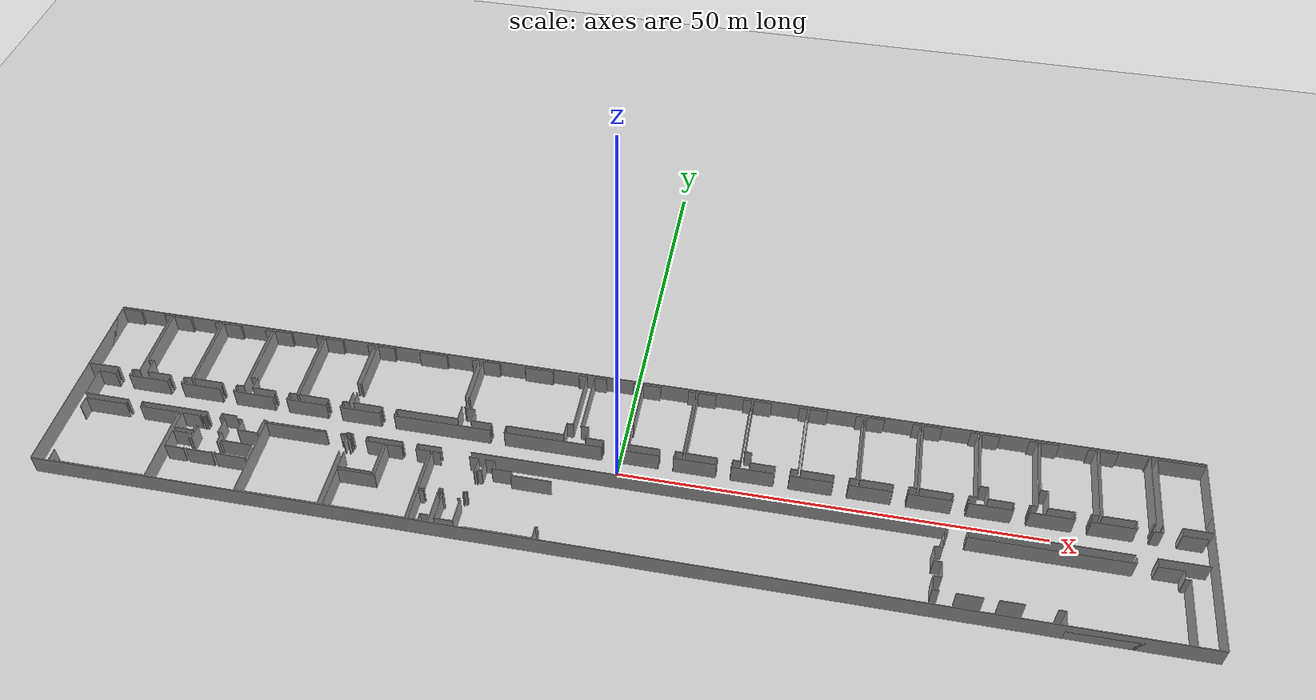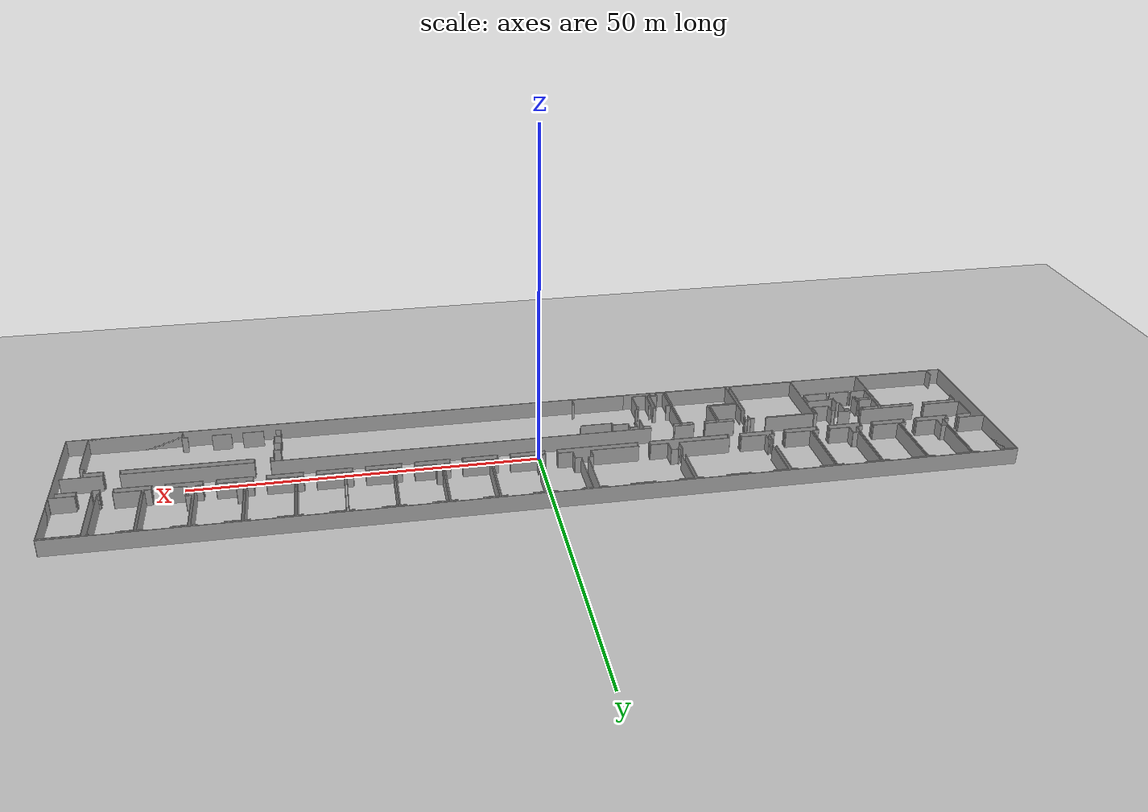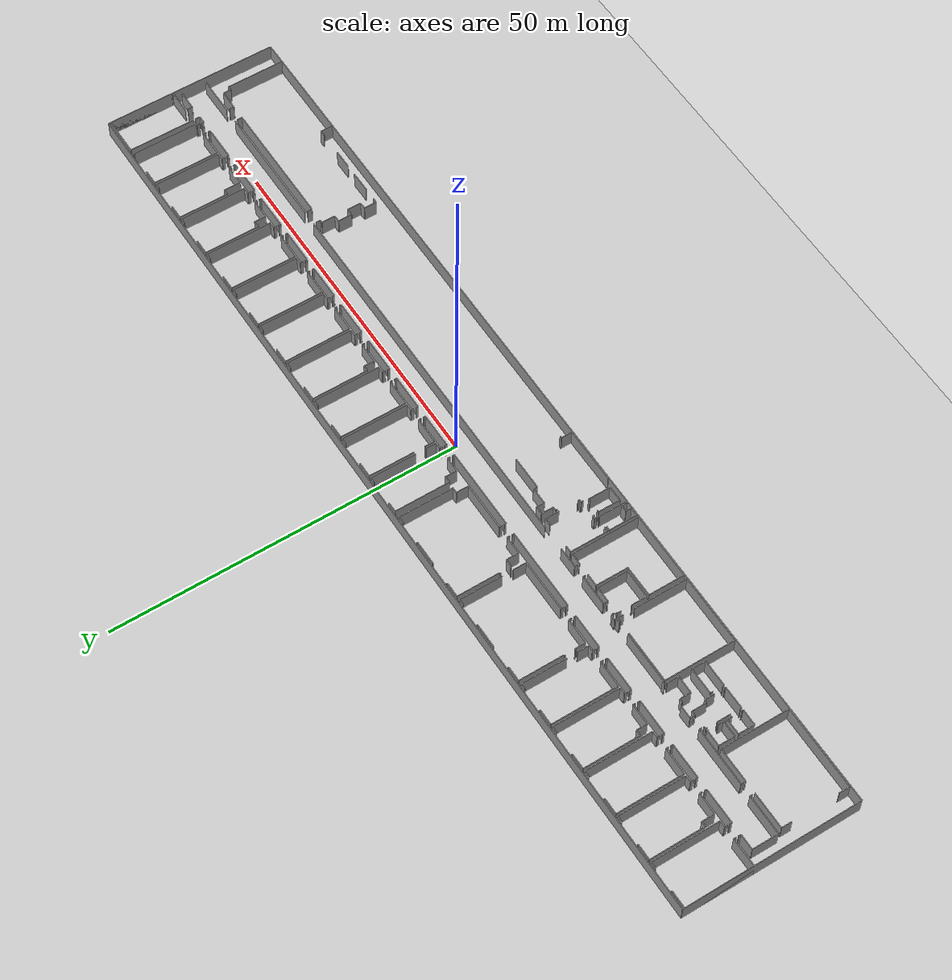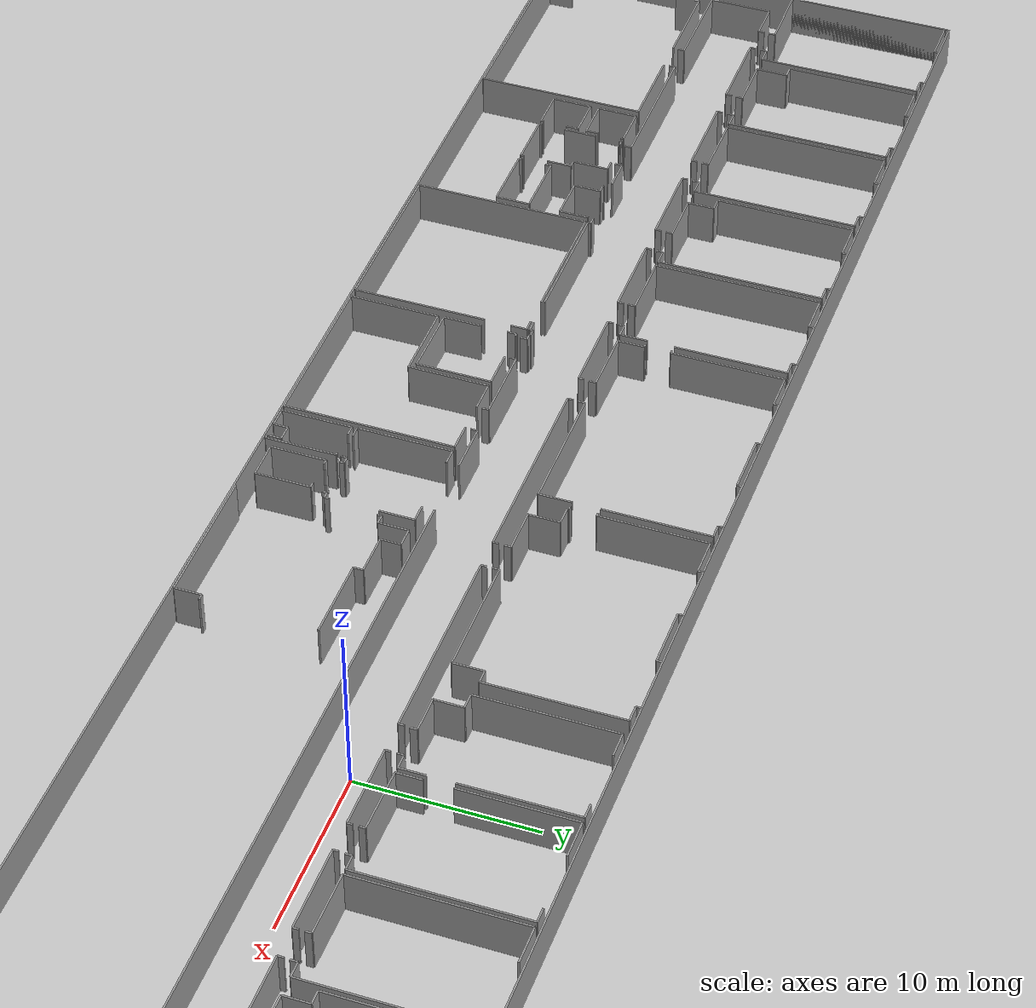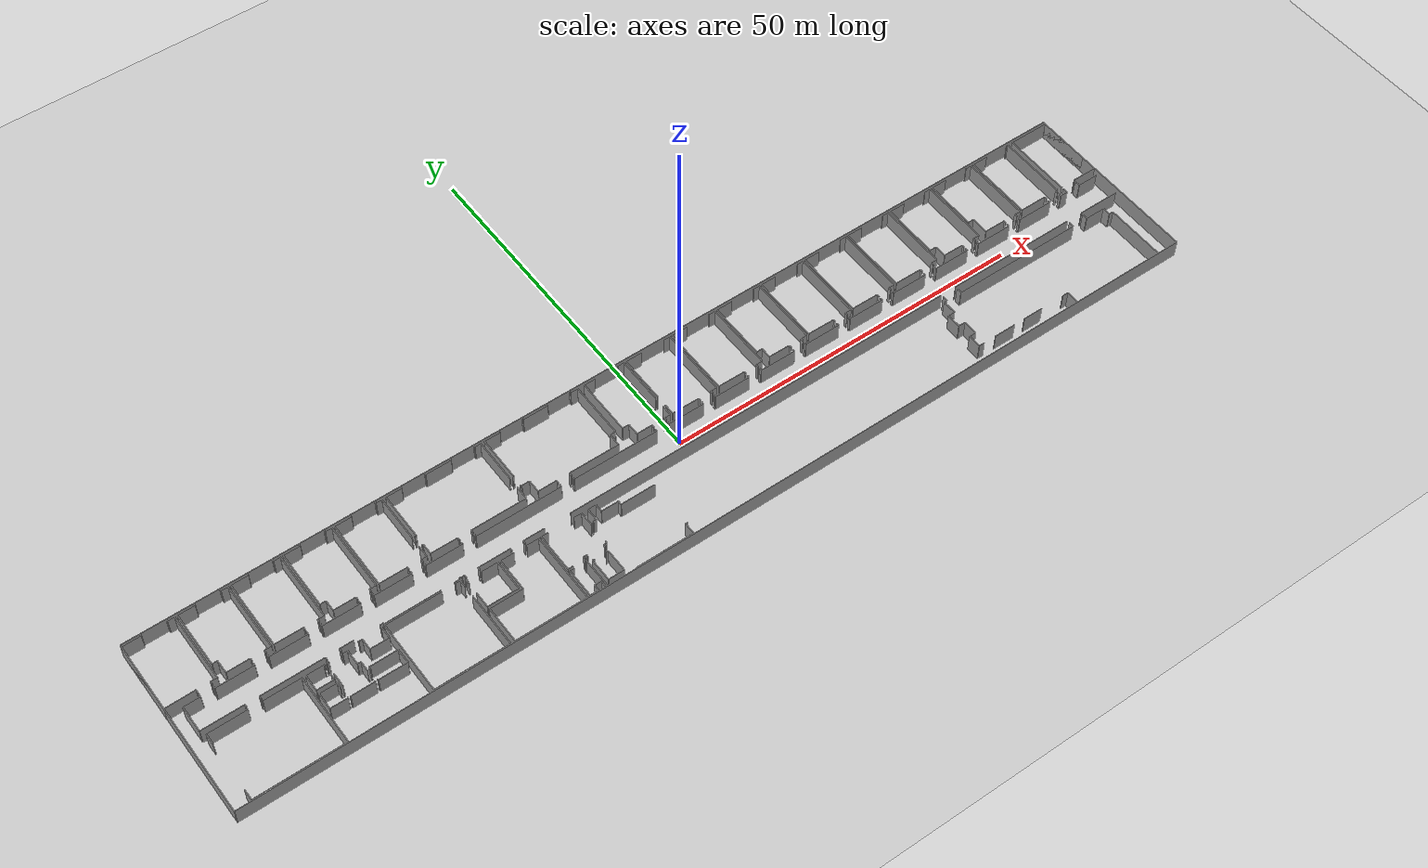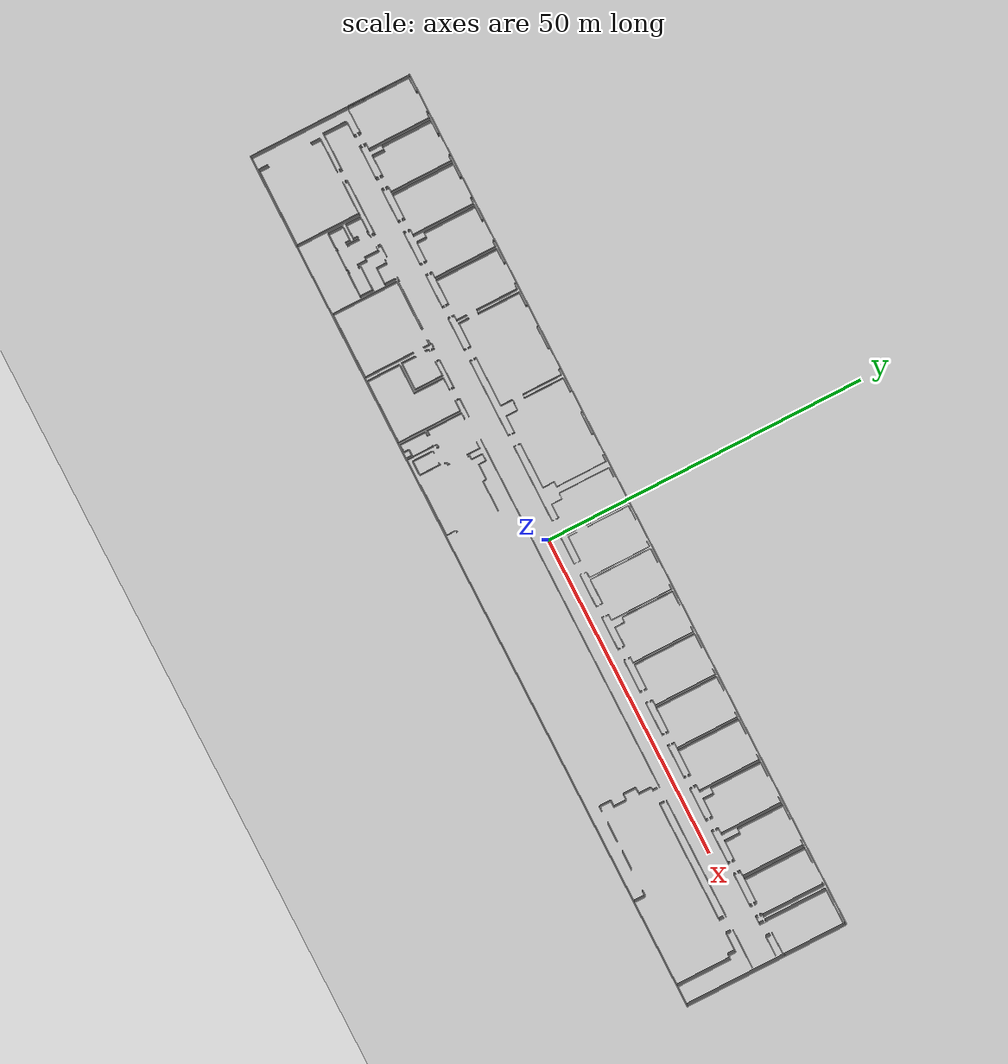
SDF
<sdf version="1.6">
  <world name="default">
    <light name="sun" type="directional">
      <cast_shadows>1</cast_shadows>
      <pose frame="">0 0 10 0 -0 0</pose>
      <diffuse>0.8 0.8 0.8 1</diffuse>
      <specular>0.1 0.1 0.1 1</specular>
      <attenuation>
        <range>1000</range>
        <constant>0.9</constant>
        <linear>0.01</linear>
        <quadratic>0.001</quadratic>
      </attenuation>
      <direction>-0.5 0.5 -1</direction>
    </light>
    <model name="ground_plane">
      <static>1</static>
      <link name="link">
        <collision name="collision">
          <geometry>
            <plane>
              <normal>0 0 1</normal>
              <size>100 100</size>
            </plane>
          </geometry>
          <surface>
            <friction>
              <ode>
                <mu>100</mu>
                <mu2>50</mu2>
              </ode>
              <torsional>
                <ode />
              </torsional>
            </friction>
            <contact>
              <ode />
            </contact>
            <bounce />
          </surface>
          <max_contacts>10</max_contacts>
        </collision>
        <visual name="visual">
          <cast_shadows>0</cast_shadows>
          <geometry>
            <plane>
              <normal>0 0 1</normal>
              <size>100 100</size>
            </plane>
          </geometry>
          <material>
            <script>
              <uri>file://media/materials/scripts/gazebo.material</uri>
              <name>Gazebo/Grey</name>
            </script>
          </material>
        </visual>
        <self_collide>0</self_collide>
        <kinematic>0</kinematic>
        <gravity>1</gravity>
      </link>
    </model>
    <gravity>0 0 -9.8</gravity>
    <magnetic_field>6e-06 2.3e-05 -4.2e-05</magnetic_field>
    <atmosphere type="adiabatic" />
    <physics default="0" name="default_physics" type="ode">
      <max_step_size>0.001</max_step_size>
      <real_time_factor>1</real_time_factor>
      <real_time_update_rate>1000</real_time_update_rate>
    </physics>
    <scene>
      <ambient>0.4 0.4 0.4 1</ambient>
      <background>0.7 0.7 0.7 1</background>
      <shadows>1</shadows>
    </scene>
    <spherical_coordinates>
      <surface_model>EARTH_WGS84</surface_model>
      <latitude_deg>0</latitude_deg>
      <longitude_deg>0</longitude_deg>
      <elevation>0</elevation>
      <heading_deg>0</heading_deg>
    </spherical_coordinates>
  <model name="0510032198_A_40_1_106">
		<static>1</static>
		<link name="Wall_0">
			<collision name="Wall_0_Collision">
				<geometry>
					<box>
						<size>9.73205097257 0.1 2.5</size>
					</box>
				</geometry>
				<pose frame="">4.86602548628 0 1.25 0 0 0</pose>
			</collision>
			<visual name="Wall_0_Visual">
				<pose frame="">4.86602548628 0 1.25 0 0 0</pose>
				<geometry>
					<box>
						<size>9.73205097257 0.1 2.5</size>
					</box>
				</geometry>
				<material>
					<script>
						<uri>file://media/materials/scripts/gazebo.material</uri>
						<name>Gazebo/Grey</name>
					</script>
					<ambient>1 1 1 1</ambient>
				</material>
			</visual>
			<pose frame="">0.0 -10.0095287705 0 0 0 1.57079632679</pose>
		</link>
		<link name="Wall_1">
			<collision name="Wall_1_Collision">
				<geometry>
					<box>
						<size>2.4666810657 0.1 2.5</size>
					</box>
				</geometry>
				<pose frame="">1.23334053285 0 1.25 0 0 0</pose>
			</collision>
			<visual name="Wall_1_Visual">
				<pose frame="">1.23334053285 0 1.25 0 0 0</pose>
				<geometry>
					<box>
						<size>2.4666810657 0.1 2.5</size>
					</box>
				</geometry>
				<material>
					<script>
						<uri>file://media/materials/scripts/gazebo.material</uri>
						<name>Gazebo/Grey</name>
					</script>
					<ambient>1 1 1 1</ambient>
				</material>
			</visual>
			<pose frame="">0.0 -0.277477797965 0 0 0 0.0</pose>
		</link>
		<link name="Wall_2">
			<collision name="Wall_2_Collision">
				<geometry>
					<box>
						<size>0.267313776061 0.1 2.5</size>
					</box>
				</geometry>
				<pose frame="">0.133656888031 0 1.25 0 0 0</pose>
			</collision>
			<visual name="Wall_2_Visual">
				<pose frame="">0.133656888031 0 1.25 0 0 0</pose>
				<geometry>
					<box>
						<size>0.267313776061 0.1 2.5</size>
					</box>
				</geometry>
				<material>
					<script>
						<uri>file://media/materials/scripts/gazebo.material</uri>
						<name>Gazebo/Grey</name>
					</script>
					<ambient>1 1 1 1</ambient>
				</material>
			</visual>
			<pose frame="">2.4666810657 -0.277477797965 0 0 0 1.57079632679</pose>
		</link>
		<link name="Wall_3">
			<collision name="Wall_3_Collision">
				<geometry>
					<box>
						<size>0.284973764118 0.1 2.5</size>
					</box>
				</geometry>
				<pose frame="">0.142486882059 0 1.25 0 0 0</pose>
			</collision>
			<visual name="Wall_3_Visual">
				<pose frame="">0.142486882059 0 1.25 0 0 0</pose>
				<geometry>
					<box>
						<size>0.284973764118 0.1 2.5</size>
					</box>
				</geometry>
				<material>
					<script>
						<uri>file://media/materials/scripts/gazebo.material</uri>
						<name>Gazebo/Grey</name>
					</script>
					<ambient>1 1 1 1</ambient>
				</material>
			</visual>
			<pose frame="">5.76897178213 -0.0101640219035 0 0 0 -1.57079632679</pose>
		</link>
		<link name="Wall_4">
			<collision name="Wall_4_Collision">
				<geometry>
					<box>
						<size>0.919462831442 0.1 2.5</size>
					</box>
				</geometry>
				<pose frame="">0.459731415721 0 1.25 0 0 0</pose>
			</collision>
			<visual name="Wall_4_Visual">
				<pose frame="">0.459731415721 0 1.25 0 0 0</pose>
				<geometry>
					<box>
						<size>0.919462831442 0.1 2.5</size>
					</box>
				</geometry>
				<material>
					<script>
						<uri>file://media/materials/scripts/gazebo.material</uri>
						<name>Gazebo/Grey</name>
					</script>
					<ambient>1 1 1 1</ambient>
				</material>
			</visual>
			<pose frame="">5.76897178213 -0.295137786022 0 0 0 0.0</pose>
		</link>
		<link name="Wall_5">
			<collision name="Wall_5_Collision">
				<geometry>
					<box>
						<size>9.67411604772 0.1 2.5</size>
					</box>
				</geometry>
				<pose frame="">4.83705802386 0 1.25 0 0 0</pose>
			</collision>
			<visual name="Wall_5_Visual">
				<pose frame="">4.83705802386 0 1.25 0 0 0</pose>
				<geometry>
					<box>
						<size>9.67411604772 0.1 2.5</size>
					</box>
				</geometry>
				<material>
					<script>
						<uri>file://media/materials/scripts/gazebo.material</uri>
						<name>Gazebo/Grey</name>
					</script>
					<ambient>1 1 1 1</ambient>
				</material>
			</visual>
			<pose frame="">6.68843461358 -0.295137786022 0 0 0 -1.57079632679</pose>
		</link>
		<link name="Wall_6">
			<collision name="Wall_6_Collision">
				<geometry>
					<box>
						<size>0.894815078326 0.1 2.5</size>
					</box>
				</geometry>
				<pose frame="">0.447407539163 0 1.25 0 0 0</pose>
			</collision>
			<visual name="Wall_6_Visual">
				<pose frame="">0.447407539163 0 1.25 0 0 0</pose>
				<geometry>
					<box>
						<size>0.894815078326 0.1 2.5</size>
					</box>
				</geometry>
				<material>
					<script>
						<uri>file://media/materials/scripts/gazebo.material</uri>
						<name>Gazebo/Grey</name>
					</script>
					<ambient>1 1 1 1</ambient>
				</material>
			</visual>
			<pose frame="">6.68843461358 -9.96925383374 0 0 0 3.14159265359</pose>
		</link>
		<link name="Wall_7">
			<collision name="Wall_7_Collision">
				<geometry>
					<box>
						<size>0.390044340546 0.1 2.5</size>
					</box>
				</geometry>
				<pose frame="">0.195022170273 0 1.25 0 0 0</pose>
			</collision>
			<visual name="Wall_7_Visual">
				<pose frame="">0.195022170273 0 1.25 0 0 0</pose>
				<geometry>
					<box>
						<size>0.390044340546 0.1 2.5</size>
					</box>
				</geometry>
				<material>
					<script>
						<uri>file://media/materials/scripts/gazebo.material</uri>
						<name>Gazebo/Grey</name>
					</script>
					<ambient>1 1 1 1</ambient>
				</material>
			</visual>
			<pose frame="">5.79361953525 -9.96925383374 0 0 0 -1.57079632679</pose>
		</link>
		<link name="Wall_8">
			<collision name="Wall_8_Collision">
				<geometry>
					<box>
						<size>0.395507502319 0.1 2.5</size>
					</box>
				</geometry>
				<pose frame="">0.197753751159 0 1.25 0 0 0</pose>
			</collision>
			<visual name="Wall_8_Visual">
				<pose frame="">0.197753751159 0 1.25 0 0 0</pose>
				<geometry>
					<box>
						<size>0.395507502319 0.1 2.5</size>
					</box>
				</geometry>
				<material>
					<script>
						<uri>file://media/materials/scripts/gazebo.material</uri>
						<name>Gazebo/Grey</name>
					</script>
					<ambient>1 1 1 1</ambient>
				</material>
			</visual>
			<pose frame="">4.00716563544 -10.3592981743 0 0 0 1.57079632679</pose>
		</link>
		<link name="Wall_9">
			<collision name="Wall_9_Collision">
				<geometry>
					<box>
						<size>4.00742665604 0.1 2.5</size>
					</box>
				</geometry>
				<pose frame="">2.00371332802 0 1.25 0 0 0</pose>
			</collision>
			<visual name="Wall_9_Visual">
				<pose frame="">2.00371332802 0 1.25 0 0 0</pose>
				<geometry>
					<box>
						<size>4.00742665604 0.1 2.5</size>
					</box>
				</geometry>
				<material>
					<script>
						<uri>file://media/materials/scripts/gazebo.material</uri>
						<name>Gazebo/Grey</name>
					</script>
					<ambient>1 1 1 1</ambient>
				</material>
			</visual>
			<pose frame="">4.00716563544 -9.96379067197 0 0 0 -3.13017907187</pose>
		</link>
		<link name="Wall_10">
			<collision name="Wall_10_Collision">
				<geometry>
					<box>
						<size>1.86382751655 0.1 2.5</size>
					</box>
				</geometry>
				<pose frame="">0.931913758274 0 1.25 0 0 0</pose>
			</collision>
			<visual name="Wall_10_Visual">
				<pose frame="">0.931913758274 0 1.25 0 0 0</pose>
				<geometry>
					<box>
						<size>1.86382751655 0.1 2.5</size>
					</box>
				</geometry>
				<material>
					<script>
						<uri>file://media/materials/scripts/gazebo.material</uri>
						<name>Gazebo/Grey</name>
					</script>
					<ambient>1 1 1 1</ambient>
				</material>
			</visual>
			<pose frame="">7.74600109263 -9.97776620209 0 0 0 1.57079632679</pose>
		</link>
		<link name="Wall_11">
			<collision name="Wall_11_Collision">
				<geometry>
					<box>
						<size>0.708813477493 0.1 2.5</size>
					</box>
				</geometry>
				<pose frame="">0.354406738747 0 1.25 0 0 0</pose>
			</collision>
			<visual name="Wall_11_Visual">
				<pose frame="">0.354406738747 0 1.25 0 0 0</pose>
				<geometry>
					<box>
						<size>0.708813477493 0.1 2.5</size>
					</box>
				</geometry>
				<material>
					<script>
						<uri>file://media/materials/scripts/gazebo.material</uri>
						<name>Gazebo/Grey</name>
					</script>
					<ambient>1 1 1 1</ambient>
				</material>
			</visual>
			<pose frame="">7.74600109263 -8.11393868554 0 0 0 3.14159265359</pose>
		</link>
		<link name="Wall_12">
			<collision name="Wall_12_Collision">
				<geometry>
					<box>
						<size>7.81613284377 0.1 2.5</size>
					</box>
				</geometry>
				<pose frame="">3.90806642188 0 1.25 0 0 0</pose>
			</collision>
			<visual name="Wall_12_Visual">
				<pose frame="">3.90806642188 0 1.25 0 0 0</pose>
				<geometry>
					<box>
						<size>7.81613284377 0.1 2.5</size>
					</box>
				</geometry>
				<material>
					<script>
						<uri>file://media/materials/scripts/gazebo.material</uri>
						<name>Gazebo/Grey</name>
					</script>
					<ambient>1 1 1 1</ambient>
				</material>
			</visual>
			<pose frame="">7.03718761514 -8.11393868554 0 0 0 1.57079632679</pose>
		</link>
		<link name="Wall_13">
			<collision name="Wall_13_Collision">
				<geometry>
					<box>
						<size>2.24688409204 0.1 2.5</size>
					</box>
				</geometry>
				<pose frame="">1.12344204602 0 1.25 0 0 0</pose>
			</collision>
			<visual name="Wall_13_Visual">
				<pose frame="">1.12344204602 0 1.25 0 0 0</pose>
				<geometry>
					<box>
						<size>2.24688409204 0.1 2.5</size>
					</box>
				</geometry>
				<material>
					<script>
						<uri>file://media/materials/scripts/gazebo.material</uri>
						<name>Gazebo/Grey</name>
					</script>
					<ambient>1 1 1 1</ambient>
				</material>
			</visual>
			<pose frame="">7.03718761514 -0.297805841772 0 0 0 0.0</pose>
		</link>
		<link name="Wall_14">
			<collision name="Wall_14_Collision">
				<geometry>
					<box>
						<size>0.275953194679 0.1 2.5</size>
					</box>
				</geometry>
				<pose frame="">0.13797659734 0 1.25 0 0 0</pose>
			</collision>
			<visual name="Wall_14_Visual">
				<pose frame="">0.13797659734 0 1.25 0 0 0</pose>
				<geometry>
					<box>
						<size>0.275953194679 0.1 2.5</size>
					</box>
				</geometry>
				<material>
					<script>
						<uri>file://media/materials/scripts/gazebo.material</uri>
						<name>Gazebo/Grey</name>
					</script>
					<ambient>1 1 1 1</ambient>
				</material>
			</visual>
			<pose frame="">9.28407170717 -0.297805841772 0 0 0 1.57079632679</pose>
		</link>
		<link name="Wall_15">
			<collision name="Wall_15_Collision">
				<geometry>
					<box>
						<size>0.287641819868 0.1 2.5</size>
					</box>
				</geometry>
				<pose frame="">0.143820909934 0 1.25 0 0 0</pose>
			</collision>
			<visual name="Wall_15_Visual">
				<pose frame="">0.143820909934 0 1.25 0 0 0</pose>
				<geometry>
					<box>
						<size>0.287641819868 0.1 2.5</size>
					</box>
				</geometry>
				<material>
					<script>
						<uri>file://media/materials/scripts/gazebo.material</uri>
						<name>Gazebo/Grey</name>
					</script>
					<ambient>1 1 1 1</ambient>
				</material>
			</visual>
			<pose frame="">12.6014814062 -0.0218526470925 0 0 0 -1.57079632679</pose>
		</link>
		<link name="Wall_16">
			<collision name="Wall_16_Collision">
				<geometry>
					<box>
						<size>0.91704887624 0.1 2.5</size>
					</box>
				</geometry>
				<pose frame="">0.45852443812 0 1.25 0 0 0</pose>
			</collision>
			<visual name="Wall_16_Visual">
				<pose frame="">0.45852443812 0 1.25 0 0 0</pose>
				<geometry>
					<box>
						<size>0.91704887624 0.1 2.5</size>
					</box>
				</geometry>
				<material>
					<script>
						<uri>file://media/materials/scripts/gazebo.material</uri>
						<name>Gazebo/Grey</name>
					</script>
					<ambient>1 1 1 1</ambient>
				</material>
			</visual>
			<pose frame="">12.6014814062 -0.309494466961 0 0 0 0.0</pose>
		</link>
		<link name="Wall_17">
			<collision name="Wall_17_Collision">
				<geometry>
					<box>
						<size>9.65569375802 0.1 2.5</size>
					</box>
				</geometry>
				<pose frame="">4.82784687901 0 1.25 0 0 0</pose>
			</collision>
			<visual name="Wall_17_Visual">
				<pose frame="">4.82784687901 0 1.25 0 0 0</pose>
				<geometry>
					<box>
						<size>9.65569375802 0.1 2.5</size>
					</box>
				</geometry>
				<material>
					<script>
						<uri>file://media/materials/scripts/gazebo.material</uri>
						<name>Gazebo/Grey</name>
					</script>
					<ambient>1 1 1 1</ambient>
				</material>
			</visual>
			<pose frame="">13.5185302824 -0.309494466961 0 0 0 -1.57079632679</pose>
		</link>
		<link name="Wall_18">
			<collision name="Wall_18_Collision">
				<geometry>
					<box>
						<size>0.90231104448 0.1 2.5</size>
					</box>
				</geometry>
				<pose frame="">0.45115552224 0 1.25 0 0 0</pose>
			</collision>
			<visual name="Wall_18_Visual">
				<pose frame="">0.45115552224 0 1.25 0 0 0</pose>
				<geometry>
					<box>
						<size>0.90231104448 0.1 2.5</size>
					</box>
				</geometry>
				<material>
					<script>
						<uri>file://media/materials/scripts/gazebo.material</uri>
						<name>Gazebo/Grey</name>
					</script>
					<ambient>1 1 1 1</ambient>
				</material>
			</visual>
			<pose frame="">13.5185302824 -9.96518822498 0 0 0 3.14159265359</pose>
		</link>
		<link name="Wall_19">
			<collision name="Wall_19_Collision">
				<geometry>
					<box>
						<size>0.397921457521 0.1 2.5</size>
					</box>
				</geometry>
				<pose frame="">0.19896072876 0 1.25 0 0 0</pose>
			</collision>
			<visual name="Wall_19_Visual">
				<pose frame="">0.19896072876 0 1.25 0 0 0</pose>
				<geometry>
					<box>
						<size>0.397921457521 0.1 2.5</size>
					</box>
				</geometry>
				<material>
					<script>
						<uri>file://media/materials/scripts/gazebo.material</uri>
						<name>Gazebo/Grey</name>
					</script>
					<ambient>1 1 1 1</ambient>
				</material>
			</visual>
			<pose frame="">12.616219238 -9.96518822498 0 0 0 -1.57079632679</pose>
		</link>
		<link name="Wall_20">
			<collision name="Wall_20_Collision">
				<geometry>
					<box>
						<size>0.391568943831 0.1 2.5</size>
					</box>
				</geometry>
				<pose frame="">0.195784471916 0 1.25 0 0 0</pose>
			</collision>
			<visual name="Wall_20_Visual">
				<pose frame="">0.195784471916 0 1.25 0 0 0</pose>
				<geometry>
					<box>
						<size>0.391568943831 0.1 2.5</size>
					</box>
				</geometry>
				<material>
					<script>
						<uri>file://media/materials/scripts/gazebo.material</uri>
						<name>Gazebo/Grey</name>
					</script>
					<ambient>1 1 1 1</ambient>
				</material>
			</visual>
			<pose frame="">10.8348473491 -10.3631096825 0 0 0 1.57079632679</pose>
		</link>
		<link name="Wall_21">
			<collision name="Wall_21_Collision">
				<geometry>
					<box>
						<size>3.08885253006 0.1 2.5</size>
					</box>
				</geometry>
				<pose frame="">1.54442626503 0 1.25 0 0 0</pose>
			</collision>
			<visual name="Wall_21_Visual">
				<pose frame="">1.54442626503 0 1.25 0 0 0</pose>
				<geometry>
					<box>
						<size>3.08885253006 0.1 2.5</size>
					</box>
				</geometry>
				<material>
					<script>
						<uri>file://media/materials/scripts/gazebo.material</uri>
						<name>Gazebo/Grey</name>
					</script>
					<ambient>1 1 1 1</ambient>
				</material>
			</visual>
			<pose frame="">10.8348473491 -9.97154073867 0 0 0 -3.13957719071</pose>
		</link>
		<link name="Wall_22">
			<collision name="Wall_22_Collision">
				<geometry>
					<box>
						<size>9.63943132297 0.1 2.5</size>
					</box>
				</geometry>
				<pose frame="">4.81971566149 0 1.25 0 0 0</pose>
			</collision>
			<visual name="Wall_22_Visual">
				<pose frame="">4.81971566149 0 1.25 0 0 0</pose>
				<geometry>
					<box>
						<size>9.63943132297 0.1 2.5</size>
					</box>
				</geometry>
				<material>
					<script>
						<uri>file://media/materials/scripts/gazebo.material</uri>
						<name>Gazebo/Grey</name>
					</script>
					<ambient>1 1 1 1</ambient>
				</material>
			</visual>
			<pose frame="">13.8533077539 -9.94460608063 0 0 0 1.57079632679</pose>
		</link>
		<link name="Wall_23">
			<collision name="Wall_23_Collision">
				<geometry>
					<box>
						<size>2.27369169981 0.1 2.5</size>
					</box>
				</geometry>
				<pose frame="">1.1368458499 0 1.25 0 0 0</pose>
			</collision>
			<visual name="Wall_23_Visual">
				<pose frame="">1.1368458499 0 1.25 0 0 0</pose>
				<geometry>
					<box>
						<size>2.27369169981 0.1 2.5</size>
					</box>
				</geometry>
				<material>
					<script>
						<uri>file://media/materials/scripts/gazebo.material</uri>
						<name>Gazebo/Grey</name>
					</script>
					<ambient>1 1 1 1</ambient>
				</material>
			</visual>
			<pose frame="">13.8533077539 -0.305174757652 0 0 0 0.0</pose>
		</link>
		<link name="Wall_24">
			<collision name="Wall_24_Collision">
				<geometry>
					<box>
						<size>0.290563976165 0.1 2.5</size>
					</box>
				</geometry>
				<pose frame="">0.145281988083 0 1.25 0 0 0</pose>
			</collision>
			<visual name="Wall_24_Visual">
				<pose frame="">0.145281988083 0 1.25 0 0 0</pose>
				<geometry>
					<box>
						<size>0.290563976165 0.1 2.5</size>
					</box>
				</geometry>
				<material>
					<script>
						<uri>file://media/materials/scripts/gazebo.material</uri>
						<name>Gazebo/Grey</name>
					</script>
					<ambient>1 1 1 1</ambient>
				</material>
			</visual>
			<pose frame="">16.1269994537 -0.305174757652 0 0 0 1.57079632679</pose>
		</link>
		<link name="Wall_25">
			<collision name="Wall_25_Collision">
				<geometry>
					<box>
						<size>0.296281238486 0.1 2.5</size>
					</box>
				</geometry>
				<pose frame="">0.148140619243 0 1.25 0 0 0</pose>
			</collision>
			<visual name="Wall_25_Visual">
				<pose frame="">0.148140619243 0 1.25 0 0 0</pose>
				<geometry>
					<box>
						<size>0.296281238486 0.1 2.5</size>
					</box>
				</geometry>
				<material>
					<script>
						<uri>file://media/materials/scripts/gazebo.material</uri>
						<name>Gazebo/Grey</name>
					</script>
					<ambient>1 1 1 1</ambient>
				</material>
			</visual>
			<pose frame="">19.4164580925 -0.0146107814862 0 0 0 -1.57079632679</pose>
		</link>
		<link name="Wall_26">
			<collision name="Wall_26_Collision">
				<geometry>
					<box>
						<size>0.918954630347 0.1 2.5</size>
					</box>
				</geometry>
				<pose frame="">0.459477315174 0 1.25 0 0 0</pose>
			</collision>
			<visual name="Wall_26_Visual">
				<pose frame="">0.459477315174 0 1.25 0 0 0</pose>
				<geometry>
					<box>
						<size>0.918954630347 0.1 2.5</size>
					</box>
				</geometry>
				<material>
					<script>
						<uri>file://media/materials/scripts/gazebo.material</uri>
						<name>Gazebo/Grey</name>
					</script>
					<ambient>1 1 1 1</ambient>
				</material>
			</visual>
			<pose frame="">19.4164580925 -0.310892019972 0 0 0 0.0</pose>
		</link>
		<link name="Wall_27">
			<collision name="Wall_27_Collision">
				<geometry>
					<box>
						<size>9.65836181377 0.1 2.5</size>
					</box>
				</geometry>
				<pose frame="">4.82918090688 0 1.25 0 0 0</pose>
			</collision>
			<visual name="Wall_27_Visual">
				<pose frame="">4.82918090688 0 1.25 0 0 0</pose>
				<geometry>
					<box>
						<size>9.65836181377 0.1 2.5</size>
					</box>
				</geometry>
				<material>
					<script>
						<uri>file://media/materials/scripts/gazebo.material</uri>
						<name>Gazebo/Grey</name>
					</script>
					<ambient>1 1 1 1</ambient>
				</material>
			</visual>
			<pose frame="">20.3354127228 -0.310892019972 0 0 0 -1.57079632679</pose>
		</link>
		<link name="Wall_28">
			<collision name="Wall_28_Collision">
				<geometry>
					<box>
						<size>0.886810911078 0.1 2.5</size>
					</box>
				</geometry>
				<pose frame="">0.443405455539 0 1.25 0 0 0</pose>
			</collision>
			<visual name="Wall_28_Visual">
				<pose frame="">0.443405455539 0 1.25 0 0 0</pose>
				<geometry>
					<box>
						<size>0.886810911078 0.1 2.5</size>
					</box>
				</geometry>
				<material>
					<script>
						<uri>file://media/materials/scripts/gazebo.material</uri>
						<name>Gazebo/Grey</name>
					</script>
					<ambient>1 1 1 1</ambient>
				</material>
			</visual>
			<pose frame="">20.3354127228 -9.96925383374 0 0 0 3.14159265359</pose>
		</link>
		<link name="Wall_29">
			<collision name="Wall_29_Collision">
				<geometry>
					<box>
						<size>0.390044340546 0.1 2.5</size>
					</box>
				</geometry>
				<pose frame="">0.195022170273 0 1.25 0 0 0</pose>
			</collision>
			<visual name="Wall_29_Visual">
				<pose frame="">0.195022170273 0 1.25 0 0 0</pose>
				<geometry>
					<box>
						<size>0.390044340546 0.1 2.5</size>
					</box>
				</geometry>
				<material>
					<script>
						<uri>file://media/materials/scripts/gazebo.material</uri>
						<name>Gazebo/Grey</name>
					</script>
					<ambient>1 1 1 1</ambient>
				</material>
			</visual>
			<pose frame="">19.4486018117 -9.96925383374 0 0 0 -1.57079632679</pose>
		</link>
		<link name="Wall_30">
			<collision name="Wall_30_Collision">
				<geometry>
					<box>
						<size>0.381531972201 0.1 2.5</size>
					</box>
				</geometry>
				<pose frame="">0.190765986101 0 1.25 0 0 0</pose>
			</collision>
			<visual name="Wall_30_Visual">
				<pose frame="">0.190765986101 0 1.25 0 0 0</pose>
				<geometry>
					<box>
						<size>0.381531972201 0.1 2.5</size>
					</box>
				</geometry>
				<material>
					<script>
						<uri>file://media/materials/scripts/gazebo.material</uri>
						<name>Gazebo/Grey</name>
					</script>
					<ambient>1 1 1 1</ambient>
				</material>
			</visual>
			<pose frame="">17.6681192748 -10.3592981743 0 0 0 1.57079632679</pose>
		</link>
		<link name="Wall_31">
			<collision name="Wall_31_Collision">
				<geometry>
					<box>
						<size>3.81495563982 0.1 2.5</size>
					</box>
				</geometry>
				<pose frame="">1.90747781991 0 1.25 0 0 0</pose>
			</collision>
			<visual name="Wall_31_Visual">
				<pose frame="">1.90747781991 0 1.25 0 0 0</pose>
				<geometry>
					<box>
						<size>3.81495563982 0.1 2.5</size>
					</box>
				</geometry>
				<material>
					<script>
						<uri>file://media/materials/scripts/gazebo.material</uri>
						<name>Gazebo/Grey</name>
					</script>
					<ambient>1 1 1 1</ambient>
				</material>
			</visual>
			<pose frame="">17.6681192748 -9.97776620209 0 0 0 3.13290040598</pose>
		</link>
		<link name="Wall_32">
			<collision name="Wall_32_Collision">
				<geometry>
					<box>
						<size>1.54543953042 0.1 2.5</size>
					</box>
				</geometry>
				<pose frame="">0.772719765211 0 1.25 0 0 0</pose>
			</collision>
			<visual name="Wall_32_Visual">
				<pose frame="">0.772719765211 0 1.25 0 0 0</pose>
				<geometry>
					<box>
						<size>1.54543953042 0.1 2.5</size>
					</box>
				</geometry>
				<material>
					<script>
						<uri>file://media/materials/scripts/gazebo.material</uri>
						<name>Gazebo/Grey</name>
					</script>
					<ambient>1 1 1 1</ambient>
				</material>
			</visual>
			<pose frame="">21.4966522253 -9.9762415988 0 0 0 1.57079632679</pose>
		</link>
		<link name="Wall_33">
			<collision name="Wall_33_Collision">
				<geometry>
					<box>
						<size>0.802068378457 0.1 2.5</size>
					</box>
				</geometry>
				<pose frame="">0.401034189229 0 1.25 0 0 0</pose>
			</collision>
			<visual name="Wall_33_Visual">
				<pose frame="">0.401034189229 0 1.25 0 0 0</pose>
				<geometry>
					<box>
						<size>0.802068378457 0.1 2.5</size>
					</box>
				</geometry>
				<material>
					<script>
						<uri>file://media/materials/scripts/gazebo.material</uri>
						<name>Gazebo/Grey</name>
					</script>
					<ambient>1 1 1 1</ambient>
				</material>
			</visual>
			<pose frame="">21.4966522253 -8.43080206838 0 0 0 3.14159265359</pose>
		</link>
		<link name="Wall_34">
			<collision name="Wall_34_Collision">
				<geometry>
					<box>
						<size>8.1174960932 0.1 2.5</size>
					</box>
				</geometry>
				<pose frame="">4.0587480466 0 1.25 0 0 0</pose>
			</collision>
			<visual name="Wall_34_Visual">
				<pose frame="">4.0587480466 0 1.25 0 0 0</pose>
				<geometry>
					<box>
						<size>8.1174960932 0.1 2.5</size>
					</box>
				</geometry>
				<material>
					<script>
						<uri>file://media/materials/scripts/gazebo.material</uri>
						<name>Gazebo/Grey</name>
					</script>
					<ambient>1 1 1 1</ambient>
				</material>
			</visual>
			<pose frame="">20.6945838468 -8.43080206838 0 0 0 1.57079632679</pose>
		</link>
		<link name="Wall_35">
			<collision name="Wall_35_Collision">
				<geometry>
					<box>
						<size>2.23036755644 0.1 2.5</size>
					</box>
				</geometry>
				<pose frame="">1.11518377822 0 1.25 0 0 0</pose>
			</collision>
			<visual name="Wall_35_Visual">
				<pose frame="">1.11518377822 0 1.25 0 0 0</pose>
				<geometry>
					<box>
						<size>2.23036755644 0.1 2.5</size>
					</box>
				</geometry>
				<material>
					<script>
						<uri>file://media/materials/scripts/gazebo.material</uri>
						<name>Gazebo/Grey</name>
					</script>
					<ambient>1 1 1 1</ambient>
				</material>
			</visual>
			<pose frame="">20.6945838468 -0.313305975174 0 0 0 0.0</pose>
		</link>
		<link name="Wall_36">
			<collision name="Wall_36_Collision">
				<geometry>
					<box>
						<size>0.296789439581 0.1 2.5</size>
					</box>
				</geometry>
				<pose frame="">0.148394719791 0 1.25 0 0 0</pose>
			</collision>
			<visual name="Wall_36_Visual">
				<pose frame="">0.148394719791 0 1.25 0 0 0</pose>
				<geometry>
					<box>
						<size>0.296789439581 0.1 2.5</size>
					</box>
				</geometry>
				<material>
					<script>
						<uri>file://media/materials/scripts/gazebo.material</uri>
						<name>Gazebo/Grey</name>
					</script>
					<ambient>1 1 1 1</ambient>
				</material>
			</visual>
			<pose frame="">22.9249514033 -0.313305975174 0 0 0 1.57079632679</pose>
		</link>
		<link name="Wall_37">
			<collision name="Wall_37_Collision">
				<geometry>
					<box>
						<size>0.292977931367 0.1 2.5</size>
					</box>
				</geometry>
				<pose frame="">0.146488965684 0 1.25 0 0 0</pose>
			</collision>
			<visual name="Wall_37_Visual">
				<pose frame="">0.146488965684 0 1.25 0 0 0</pose>
				<geometry>
					<box>
						<size>0.292977931367 0.1 2.5</size>
					</box>
				</geometry>
				<material>
					<script>
						<uri>file://media/materials/scripts/gazebo.material</uri>
						<name>Gazebo/Grey</name>
					</script>
					<ambient>1 1 1 1</ambient>
				</material>
			</visual>
			<pose frame="">26.2569718838 -0.0165165355931 0 0 0 -1.57079632679</pose>
		</link>
		<link name="Wall_38">
			<collision name="Wall_38_Collision">
				<geometry>
					<box>
						<size>0.907520105706 0.1 2.5</size>
					</box>
				</geometry>
				<pose frame="">0.453760052853 0 1.25 0 0 0</pose>
			</collision>
			<visual name="Wall_38_Visual">
				<pose frame="">0.453760052853 0 1.25 0 0 0</pose>
				<geometry>
					<box>
						<size>0.907520105706 0.1 2.5</size>
					</box>
				</geometry>
				<material>
					<script>
						<uri>file://media/materials/scripts/gazebo.material</uri>
						<name>Gazebo/Grey</name>
					</script>
					<ambient>1 1 1 1</ambient>
				</material>
			</visual>
			<pose frame="">26.2569718838 -0.309494466961 0 0 0 0.0</pose>
		</link>
		<link name="Wall_39">
			<collision name="Wall_39_Collision">
				<geometry>
					<box>
						<size>9.65429620501 0.1 2.5</size>
					</box>
				</geometry>
				<pose frame="">4.8271481025 0 1.25 0 0 0</pose>
			</collision>
			<visual name="Wall_39_Visual">
				<pose frame="">4.8271481025 0 1.25 0 0 0</pose>
				<geometry>
					<box>
						<size>9.65429620501 0.1 2.5</size>
					</box>
				</geometry>
				<material>
					<script>
						<uri>file://media/materials/scripts/gazebo.material</uri>
						<name>Gazebo/Grey</name>
					</script>
					<ambient>1 1 1 1</ambient>
				</material>
			</visual>
			<pose frame="">27.1644919895 -0.309494466961 0 0 0 -1.57079632679</pose>
		</link>
		<link name="Wall_40">
			<collision name="Wall_40_Collision">
				<geometry>
					<box>
						<size>0.910442262003 0.1 2.5</size>
					</box>
				</geometry>
				<pose frame="">0.455221131002 0 1.25 0 0 0</pose>
			</collision>
			<visual name="Wall_40_Visual">
				<pose frame="">0.455221131002 0 1.25 0 0 0</pose>
				<geometry>
					<box>
						<size>0.910442262003 0.1 2.5</size>
					</box>
				</geometry>
				<material>
					<script>
						<uri>file://media/materials/scripts/gazebo.material</uri>
						<name>Gazebo/Grey</name>
					</script>
					<ambient>1 1 1 1</ambient>
				</material>
			</visual>
			<pose frame="">27.1644919895 -9.96379067197 0 0 0 3.14159265359</pose>
		</link>
		<link name="Wall_41">
			<collision name="Wall_41_Collision">
				<geometry>
					<box>
						<size>0.406433825865 0.1 2.5</size>
					</box>
				</geometry>
				<pose frame="">0.203216912932 0 1.25 0 0 0</pose>
			</collision>
			<visual name="Wall_41_Visual">
				<pose frame="">0.203216912932 0 1.25 0 0 0</pose>
				<geometry>
					<box>
						<size>0.406433825865 0.1 2.5</size>
					</box>
				</geometry>
				<material>
					<script>
						<uri>file://media/materials/scripts/gazebo.material</uri>
						<name>Gazebo/Grey</name>
					</script>
					<ambient>1 1 1 1</ambient>
				</material>
			</visual>
			<pose frame="">26.2540497275 -9.96379067197 0 0 0 -1.57079632679</pose>
		</link>
		<link name="Wall_42">
			<collision name="Wall_42_Collision">
				<geometry>
					<box>
						<size>0.377212262892 0.1 2.5</size>
					</box>
				</geometry>
				<pose frame="">0.188606131446 0 1.25 0 0 0</pose>
			</collision>
			<visual name="Wall_42_Visual">
				<pose frame="">0.188606131446 0 1.25 0 0 0</pose>
				<geometry>
					<box>
						<size>0.377212262892 0.1 2.5</size>
					</box>
				</geometry>
				<material>
					<script>
						<uri>file://media/materials/scripts/gazebo.material</uri>
						<name>Gazebo/Grey</name>
					</script>
					<ambient>1 1 1 1</ambient>
				</material>
			</visual>
			<pose frame="">24.4847476146 -10.3702244978 0 0 0 1.57079632679</pose>
		</link>
		<link name="Wall_43">
			<collision name="Wall_43_Collision">
				<geometry>
					<box>
						<size>2.98814245143 0.1 2.5</size>
					</box>
				</geometry>
				<pose frame="">1.49407122572 0 1.25 0 0 0</pose>
			</collision>
			<visual name="Wall_43_Visual">
				<pose frame="">1.49407122572 0 1.25 0 0 0</pose>
				<geometry>
					<box>
						<size>2.98814245143 0.1 2.5</size>
					</box>
				</geometry>
				<material>
					<script>
						<uri>file://media/materials/scripts/gazebo.material</uri>
						<name>Gazebo/Grey</name>
					</script>
					<ambient>1 1 1 1</ambient>
				</material>
			</visual>
			<pose frame="">24.4847476146 -9.99301223494 0 0 0 3.135980229</pose>
		</link>
		<link name="Wall_44">
			<collision name="Wall_44_Collision">
				<geometry>
					<box>
						<size>9.6577265624 0.1 2.5</size>
					</box>
				</geometry>
				<pose frame="">4.8288632812 0 1.25 0 0 0</pose>
			</collision>
			<visual name="Wall_44_Visual">
				<pose frame="">4.8288632812 0 1.25 0 0 0</pose>
				<geometry>
					<box>
						<size>9.6577265624 0.1 2.5</size>
					</box>
				</geometry>
				<material>
					<script>
						<uri>file://media/materials/scripts/gazebo.material</uri>
						<name>Gazebo/Grey</name>
					</script>
					<ambient>1 1 1 1</ambient>
				</material>
			</visual>
			<pose frame="">27.5029539189 -9.9762415988 0 0 0 1.57079632679</pose>
		</link>
		<link name="Wall_45">
			<collision name="Wall_45_Collision">
				<geometry>
					<box>
						<size>2.23900697506 0.1 2.5</size>
					</box>
				</geometry>
				<pose frame="">1.11950348753 0 1.25 0 0 0</pose>
			</collision>
			<visual name="Wall_45_Visual">
				<pose frame="">1.11950348753 0 1.25 0 0 0</pose>
				<geometry>
					<box>
						<size>2.23900697506 0.1 2.5</size>
					</box>
				</geometry>
				<material>
					<script>
						<uri>file://media/materials/scripts/gazebo.material</uri>
						<name>Gazebo/Grey</name>
					</script>
					<ambient>1 1 1 1</ambient>
				</material>
			</visual>
			<pose frame="">27.5029539189 -0.3185150364 0 0 0 0.0</pose>
		</link>
		<link name="Wall_46">
			<collision name="Wall_46_Collision">
				<geometry>
					<box>
						<size>0.307588712854 0.1 2.5</size>
					</box>
				</geometry>
				<pose frame="">0.153794356427 0 1.25 0 0 0</pose>
			</collision>
			<visual name="Wall_46_Visual">
				<pose frame="">0.153794356427 0 1.25 0 0 0</pose>
				<geometry>
					<box>
						<size>0.307588712854 0.1 2.5</size>
					</box>
				</geometry>
				<material>
					<script>
						<uri>file://media/materials/scripts/gazebo.material</uri>
						<name>Gazebo/Grey</name>
					</script>
					<ambient>1 1 1 1</ambient>
				</material>
			</visual>
			<pose frame="">29.7419608939 -0.3185150364 0 0 0 1.57079632679</pose>
		</link>
		<link name="Wall_47">
			<collision name="Wall_47_Collision">
				<geometry>
					<box>
						<size>0.308096913949 0.1 2.5</size>
					</box>
				</geometry>
				<pose frame="">0.154048456974 0 1.25 0 0 0</pose>
			</collision>
			<visual name="Wall_47_Visual">
				<pose frame="">0.154048456974 0 1.25 0 0 0</pose>
				<geometry>
					<box>
						<size>0.308096913949 0.1 2.5</size>
					</box>
				</geometry>
				<material>
					<script>
						<uri>file://media/materials/scripts/gazebo.material</uri>
						<name>Gazebo/Grey</name>
					</script>
					<ambient>1 1 1 1</ambient>
				</material>
			</visual>
			<pose frame="">33.0727108717 -0.0109263235462 0 0 0 -1.57079632679</pose>
		</link>
		<link name="Wall_48">
			<collision name="Wall_48_Collision">
				<geometry>
					<box>
						<size>0.811978299813 0.1 2.5</size>
					</box>
				</geometry>
				<pose frame="">0.405989149907 0 1.25 0 0 0</pose>
			</collision>
			<visual name="Wall_48_Visual">
				<pose frame="">0.405989149907 0 1.25 0 0 0</pose>
				<geometry>
					<box>
						<size>0.811978299813 0.1 2.5</size>
					</box>
				</geometry>
				<material>
					<script>
						<uri>file://media/materials/scripts/gazebo.material</uri>
						<name>Gazebo/Grey</name>
					</script>
					<ambient>1 1 1 1</ambient>
				</material>
			</visual>
			<pose frame="">33.0727108717 -0.319023237495 0 0 0 0.0</pose>
		</link>
		<link name="Wall_49">
			<collision name="Wall_49_Collision">
				<geometry>
					<box>
						<size>6.51615444231 0.1 2.5</size>
					</box>
				</geometry>
				<pose frame="">3.25807722116 0 1.25 0 0 0</pose>
			</collision>
			<visual name="Wall_49_Visual">
				<pose frame="">3.25807722116 0 1.25 0 0 0</pose>
				<geometry>
					<box>
						<size>6.51615444231 0.1 2.5</size>
					</box>
				</geometry>
				<material>
					<script>
						<uri>file://media/materials/scripts/gazebo.material</uri>
						<name>Gazebo/Grey</name>
					</script>
					<ambient>1 1 1 1</ambient>
				</material>
			</visual>
			<pose frame="">33.8846891715 -0.319023237495 0 0 0 -1.57079632679</pose>
		</link>
		<link name="Wall_50">
			<collision name="Wall_50_Collision">
				<geometry>
					<box>
						<size>1.6211614936 0.1 2.5</size>
					</box>
				</geometry>
				<pose frame="">0.810580746802 0 1.25 0 0 0</pose>
			</collision>
			<visual name="Wall_50_Visual">
				<pose frame="">0.810580746802 0 1.25 0 0 0</pose>
				<geometry>
					<box>
						<size>1.6211614936 0.1 2.5</size>
					</box>
				</geometry>
				<material>
					<script>
						<uri>file://media/materials/scripts/gazebo.material</uri>
						<name>Gazebo/Grey</name>
					</script>
					<ambient>1 1 1 1</ambient>
				</material>
			</visual>
			<pose frame="">33.8846891715 -8.38061721023 0 0 0 -1.57079632679</pose>
		</link>
		<link name="Wall_51">
			<collision name="Wall_51_Collision">
				<geometry>
					<box>
						<size>0.778437027532 0.1 2.5</size>
					</box>
				</geometry>
				<pose frame="">0.389218513766 0 1.25 0 0 0</pose>
			</collision>
			<visual name="Wall_51_Visual">
				<pose frame="">0.389218513766 0 1.25 0 0 0</pose>
				<geometry>
					<box>
						<size>0.778437027532 0.1 2.5</size>
					</box>
				</geometry>
				<material>
					<script>
						<uri>file://media/materials/scripts/gazebo.material</uri>
						<name>Gazebo/Grey</name>
					</script>
					<ambient>1 1 1 1</ambient>
				</material>
			</visual>
			<pose frame="">33.8846891715 -10.0017787038 0 0 0 3.14159265359</pose>
		</link>
		<link name="Wall_52">
			<collision name="Wall_52_Collision">
				<geometry>
					<box>
						<size>0.365015436608 0.1 2.5</size>
					</box>
				</geometry>
				<pose frame="">0.182507718304 0 1.25 0 0 0</pose>
			</collision>
			<visual name="Wall_52_Visual">
				<pose frame="">0.182507718304 0 1.25 0 0 0</pose>
				<geometry>
					<box>
						<size>0.365015436608 0.1 2.5</size>
					</box>
				</geometry>
				<material>
					<script>
						<uri>file://media/materials/scripts/gazebo.material</uri>
						<name>Gazebo/Grey</name>
					</script>
					<ambient>1 1 1 1</ambient>
				</material>
			</visual>
			<pose frame="">33.106252144 -10.0017787038 0 0 0 -1.57079632679</pose>
		</link>
		<link name="Wall_53">
			<collision name="Wall_53_Collision">
				<geometry>
					<box>
						<size>0.0315084679007 0.1 2.5</size>
					</box>
				</geometry>
				<pose frame="">0.0157542339504 0 1.25 0 0 0</pose>
			</collision>
			<visual name="Wall_53_Visual">
				<pose frame="">0.0157542339504 0 1.25 0 0 0</pose>
				<geometry>
					<box>
						<size>0.0315084679007 0.1 2.5</size>
					</box>
				</geometry>
				<material>
					<script>
						<uri>file://media/materials/scripts/gazebo.material</uri>
						<name>Gazebo/Grey</name>
					</script>
					<ambient>1 1 1 1</ambient>
				</material>
			</visual>
			<pose frame="">31.3260237076 -10.3667941404 0 0 0 3.14159265359</pose>
		</link>
		<link name="Wall_54">
			<collision name="Wall_54_Collision">
				<geometry>
					<box>
						<size>0.382675424666 0.1 2.5</size>
					</box>
				</geometry>
				<pose frame="">0.191337712333 0 1.25 0 0 0</pose>
			</collision>
			<visual name="Wall_54_Visual">
				<pose frame="">0.191337712333 0 1.25 0 0 0</pose>
				<geometry>
					<box>
						<size>0.382675424666 0.1 2.5</size>
					</box>
				</geometry>
				<material>
					<script>
						<uri>file://media/materials/scripts/gazebo.material</uri>
						<name>Gazebo/Grey</name>
					</script>
					<ambient>1 1 1 1</ambient>
				</material>
			</visual>
			<pose frame="">31.2945152397 -10.3667941404 0 0 0 1.57079632679</pose>
		</link>
		<link name="Wall_55">
			<collision name="Wall_55_Collision">
				<geometry>
					<box>
						<size>3.79156950332 0.1 2.5</size>
					</box>
				</geometry>
				<pose frame="">1.89578475166 0 1.25 0 0 0</pose>
			</collision>
			<visual name="Wall_55_Visual">
				<pose frame="">1.89578475166 0 1.25 0 0 0</pose>
				<geometry>
					<box>
						<size>3.79156950332 0.1 2.5</size>
					</box>
				</geometry>
				<material>
					<script>
						<uri>file://media/materials/scripts/gazebo.material</uri>
						<name>Gazebo/Grey</name>
					</script>
					<ambient>1 1 1 1</ambient>
				</material>
			</visual>
			<pose frame="">31.2945152397 -9.98411871578 0 0 0 3.13951511746</pose>
		</link>
		<link name="Wall_56">
			<collision name="Wall_56_Collision">
				<geometry>
					<box>
						<size>1.53705421235 0.1 2.5</size>
					</box>
				</geometry>
				<pose frame="">0.768527106176 0 1.25 0 0 0</pose>
			</collision>
			<visual name="Wall_56_Visual">
				<pose frame="">0.768527106176 0 1.25 0 0 0</pose>
				<geometry>
					<box>
						<size>1.53705421235 0.1 2.5</size>
					</box>
				</geometry>
				<material>
					<script>
						<uri>file://media/materials/scripts/gazebo.material</uri>
						<name>Gazebo/Grey</name>
					</script>
					<ambient>1 1 1 1</ambient>
				</material>
			</visual>
			<pose frame="">34.4223659302 -9.93444205872 0 0 0 1.57079632679</pose>
		</link>
		<link name="Wall_57">
			<collision name="Wall_57_Collision">
				<geometry>
					<box>
						<size>0.201755834784 0.1 2.5</size>
					</box>
				</geometry>
				<pose frame="">0.100877917392 0 1.25 0 0 0</pose>
			</collision>
			<visual name="Wall_57_Visual">
				<pose frame="">0.100877917392 0 1.25 0 0 0</pose>
				<geometry>
					<box>
						<size>0.201755834784 0.1 2.5</size>
					</box>
				</geometry>
				<material>
					<script>
						<uri>file://media/materials/scripts/gazebo.material</uri>
						<name>Gazebo/Grey</name>
					</script>
					<ambient>1 1 1 1</ambient>
				</material>
			</visual>
			<pose frame="">34.4223659302 -8.39738784637 0 0 0 3.14159265359</pose>
		</link>
		<link name="Wall_58">
			<collision name="Wall_58_Collision">
				<geometry>
					<box>
						<size>0.206583745188 0.1 2.5</size>
					</box>
				</geometry>
				<pose frame="">0.103291872594 0 1.25 0 0 0</pose>
			</collision>
			<visual name="Wall_58_Visual">
				<pose frame="">0.103291872594 0 1.25 0 0 0</pose>
				<geometry>
					<box>
						<size>0.206583745188 0.1 2.5</size>
					</box>
				</geometry>
				<material>
					<script>
						<uri>file://media/materials/scripts/gazebo.material</uri>
						<name>Gazebo/Grey</name>
					</script>
					<ambient>1 1 1 1</ambient>
				</material>
			</visual>
			<pose frame="">34.2206100954 -6.85487047225 0 0 0 0.0</pose>
		</link>
		<link name="Wall_59">
			<collision name="Wall_59_Collision">
				<geometry>
					<box>
						<size>6.54728175939 0.1 2.5</size>
					</box>
				</geometry>
				<pose frame="">3.2736408797 0 1.25 0 0 0</pose>
			</collision>
			<visual name="Wall_59_Visual">
				<pose frame="">3.2736408797 0 1.25 0 0 0</pose>
				<geometry>
					<box>
						<size>6.54728175939 0.1 2.5</size>
					</box>
				</geometry>
				<material>
					<script>
						<uri>file://media/materials/scripts/gazebo.material</uri>
						<name>Gazebo/Grey</name>
					</script>
					<ambient>1 1 1 1</ambient>
				</material>
			</visual>
			<pose frame="">34.4271938406 -6.85487047225 0 0 0 1.57079632679</pose>
		</link>
		<link name="Wall_60">
			<collision name="Wall_60_Collision">
				<geometry>
					<box>
						<size>2.14219466643 0.1 2.5</size>
					</box>
				</geometry>
				<pose frame="">1.07109733321 0 1.25 0 0 0</pose>
			</collision>
			<visual name="Wall_60_Visual">
				<pose frame="">1.07109733321 0 1.25 0 0 0</pose>
				<geometry>
					<box>
						<size>2.14219466643 0.1 2.5</size>
					</box>
				</geometry>
				<material>
					<script>
						<uri>file://media/materials/scripts/gazebo.material</uri>
						<name>Gazebo/Grey</name>
					</script>
					<ambient>1 1 1 1</ambient>
				</material>
			</visual>
			<pose frame="">34.4271938406 -0.307588712854 0 0 0 0.0</pose>
		</link>
		<link name="Wall_61">
			<collision name="Wall_61_Collision">
				<geometry>
					<box>
						<size>0.307588712854 0.1 2.5</size>
					</box>
				</geometry>
				<pose frame="">0.153794356427 0 1.25 0 0 0</pose>
			</collision>
			<visual name="Wall_61_Visual">
				<pose frame="">0.153794356427 0 1.25 0 0 0</pose>
				<geometry>
					<box>
						<size>0.307588712854 0.1 2.5</size>
					</box>
				</geometry>
				<material>
					<script>
						<uri>file://media/materials/scripts/gazebo.material</uri>
						<name>Gazebo/Grey</name>
					</script>
					<ambient>1 1 1 1</ambient>
				</material>
			</visual>
			<pose frame="">36.569388507 -0.307588712854 0 0 0 1.57079632679</pose>
		</link>
		<link name="Wall_62">
			<collision name="Wall_62_Collision">
				<geometry>
					<box>
						<size>0.291072177261 0.1 2.5</size>
					</box>
				</geometry>
				<pose frame="">0.14553608863 0 1.25 0 0 0</pose>
			</collision>
			<visual name="Wall_62_Visual">
				<pose frame="">0.14553608863 0 1.25 0 0 0</pose>
				<geometry>
					<box>
						<size>0.291072177261 0.1 2.5</size>
					</box>
				</geometry>
				<material>
					<script>
						<uri>file://media/materials/scripts/gazebo.material</uri>
						<name>Gazebo/Grey</name>
					</script>
					<ambient>1 1 1 1</ambient>
				</material>
			</visual>
			<pose frame="">39.8870523066 -0.0 0 0 0 -1.57079632679</pose>
		</link>
		<link name="Wall_63">
			<collision name="Wall_63_Collision">
				<geometry>
					<box>
						<size>3.50226784739 0.1 2.5</size>
					</box>
				</geometry>
				<pose frame="">1.75113392369 0 1.25 0 0 0</pose>
			</collision>
			<visual name="Wall_63_Visual">
				<pose frame="">1.75113392369 0 1.25 0 0 0</pose>
				<geometry>
					<box>
						<size>3.50226784739 0.1 2.5</size>
					</box>
				</geometry>
				<material>
					<script>
						<uri>file://media/materials/scripts/gazebo.material</uri>
						<name>Gazebo/Grey</name>
					</script>
					<ambient>1 1 1 1</ambient>
				</material>
			</visual>
			<pose frame="">39.8870523066 -0.291072177261 0 0 0 0.0</pose>
		</link>
		<link name="Wall_64">
			<collision name="Wall_64_Collision">
				<geometry>
					<box>
						<size>0.283830311654 0.1 2.5</size>
					</box>
				</geometry>
				<pose frame="">0.141915155827 0 1.25 0 0 0</pose>
			</collision>
			<visual name="Wall_64_Visual">
				<pose frame="">0.141915155827 0 1.25 0 0 0</pose>
				<geometry>
					<box>
						<size>0.283830311654 0.1 2.5</size>
					</box>
				</geometry>
				<material>
					<script>
						<uri>file://media/materials/scripts/gazebo.material</uri>
						<name>Gazebo/Grey</name>
					</script>
					<ambient>1 1 1 1</ambient>
				</material>
			</visual>
			<pose frame="">43.389320154 -0.291072177261 0 0 0 1.57079632679</pose>
		</link>
		<link name="Wall_65">
			<collision name="Wall_65_Collision">
				<geometry>
					<box>
						<size>0.296281238486 0.1 2.5</size>
					</box>
				</geometry>
				<pose frame="">0.148140619243 0 1.25 0 0 0</pose>
			</collision>
			<visual name="Wall_65_Visual">
				<pose frame="">0.148140619243 0 1.25 0 0 0</pose>
				<geometry>
					<box>
						<size>0.296281238486 0.1 2.5</size>
					</box>
				</geometry>
				<material>
					<script>
						<uri>file://media/materials/scripts/gazebo.material</uri>
						<name>Gazebo/Grey</name>
					</script>
					<ambient>1 1 1 1</ambient>
				</material>
			</visual>
			<pose frame="">46.7060946016 -0.00724186560622 0 0 0 -1.57079632679</pose>
		</link>
		<link name="Wall_66">
			<collision name="Wall_66_Collision">
				<geometry>
					<box>
						<size>0.822396422264 0.1 2.5</size>
					</box>
				</geometry>
				<pose frame="">0.411198211132 0 1.25 0 0 0</pose>
			</collision>
			<visual name="Wall_66_Visual">
				<pose frame="">0.411198211132 0 1.25 0 0 0</pose>
				<geometry>
					<box>
						<size>0.822396422264 0.1 2.5</size>
					</box>
				</geometry>
				<material>
					<script>
						<uri>file://media/materials/scripts/gazebo.material</uri>
						<name>Gazebo/Grey</name>
					</script>
					<ambient>1 1 1 1</ambient>
				</material>
			</visual>
			<pose frame="">46.7060946016 -0.303523104092 0 0 0 0.0</pose>
		</link>
		<link name="Wall_67">
			<collision name="Wall_67_Collision">
				<geometry>
					<box>
						<size>6.19243034469 0.1 2.5</size>
					</box>
				</geometry>
				<pose frame="">3.09621517234 0 1.25 0 0 0</pose>
			</collision>
			<visual name="Wall_67_Visual">
				<pose frame="">3.09621517234 0 1.25 0 0 0</pose>
				<geometry>
					<box>
						<size>6.19243034469 0.1 2.5</size>
					</box>
				</geometry>
				<material>
					<script>
						<uri>file://media/materials/scripts/gazebo.material</uri>
						<name>Gazebo/Grey</name>
					</script>
					<ambient>1 1 1 1</ambient>
				</material>
			</visual>
			<pose frame="">47.5284910239 -0.303523104092 0 0 0 -1.57079632679</pose>
		</link>
		<link name="Wall_68">
			<collision name="Wall_68_Collision">
				<geometry>
					<box>
						<size>1.89597123582 0.1 2.5</size>
					</box>
				</geometry>
				<pose frame="">0.947985617909 0 1.25 0 0 0</pose>
			</collision>
			<visual name="Wall_68_Visual">
				<pose frame="">0.947985617909 0 1.25 0 0 0</pose>
				<geometry>
					<box>
						<size>1.89597123582 0.1 2.5</size>
					</box>
				</geometry>
				<material>
					<script>
						<uri>file://media/materials/scripts/gazebo.material</uri>
						<name>Gazebo/Grey</name>
					</script>
					<ambient>1 1 1 1</ambient>
				</material>
			</visual>
			<pose frame="">47.5284910239 -8.08497122311 0 0 0 -1.57079632679</pose>
		</link>
		<link name="Wall_69">
			<collision name="Wall_69_Collision">
				<geometry>
					<box>
						<size>7.61945901993 0.1 2.5</size>
					</box>
				</geometry>
				<pose frame="">3.80972950997 0 1.25 0 0 0</pose>
			</collision>
			<visual name="Wall_69_Visual">
				<pose frame="">3.80972950997 0 1.25 0 0 0</pose>
				<geometry>
					<box>
						<size>7.61945901993 0.1 2.5</size>
					</box>
				</geometry>
				<material>
					<script>
						<uri>file://media/materials/scripts/gazebo.material</uri>
						<name>Gazebo/Grey</name>
					</script>
					<ambient>1 1 1 1</ambient>
				</material>
			</visual>
			<pose frame="">47.5284910239 -9.98094245893 0 0 0 3.14159265359</pose>
		</link>
		<link name="Wall_70">
			<collision name="Wall_70_Collision">
				<geometry>
					<box>
						<size>0.389282038903 0.1 2.5</size>
					</box>
				</geometry>
				<pose frame="">0.194641019451 0 1.25 0 0 0</pose>
			</collision>
			<visual name="Wall_70_Visual">
				<pose frame="">0.194641019451 0 1.25 0 0 0</pose>
				<geometry>
					<box>
						<size>0.389282038903 0.1 2.5</size>
					</box>
				</geometry>
				<material>
					<script>
						<uri>file://media/materials/scripts/gazebo.material</uri>
						<name>Gazebo/Grey</name>
					</script>
					<ambient>1 1 1 1</ambient>
				</material>
			</visual>
			<pose frame="">39.909032004 -9.98094245893 0 0 0 -1.57079632679</pose>
		</link>
		<link name="Wall_71">
			<collision name="Wall_71_Collision">
				<geometry>
					<box>
						<size>0.403765770115 0.1 2.5</size>
					</box>
				</geometry>
				<pose frame="">0.201882885058 0 1.25 0 0 0</pose>
			</collision>
			<visual name="Wall_71_Visual">
				<pose frame="">0.201882885058 0 1.25 0 0 0</pose>
				<geometry>
					<box>
						<size>0.403765770115 0.1 2.5</size>
					</box>
				</geometry>
				<material>
					<script>
						<uri>file://media/materials/scripts/gazebo.material</uri>
						<name>Gazebo/Grey</name>
					</script>
					<ambient>1 1 1 1</ambient>
				</material>
			</visual>
			<pose frame="">38.1227051544 -10.3702244978 0 0 0 1.57079632679</pose>
		</link>
		<link name="Wall_72">
			<collision name="Wall_72_Collision">
				<geometry>
					<box>
						<size>3.70047773152 0.1 2.5</size>
					</box>
				</geometry>
				<pose frame="">1.85023886576 0 1.25 0 0 0</pose>
			</collision>
			<visual name="Wall_72_Visual">
				<pose frame="">1.85023886576 0 1.25 0 0 0</pose>
				<geometry>
					<box>
						<size>3.70047773152 0.1 2.5</size>
					</box>
				</geometry>
				<material>
					<script>
						<uri>file://media/materials/scripts/gazebo.material</uri>
						<name>Gazebo/Grey</name>
					</script>
					<ambient>1 1 1 1</ambient>
				</material>
			</visual>
			<pose frame="">38.1227051544 -9.96645872772 0 0 0 3.13294050898</pose>
		</link>
		<link name="Wall_73">
			<collision name="Wall_73_Collision">
				<geometry>
					<box>
						<size>1.80411388787 0.1 2.5</size>
					</box>
				</geometry>
				<pose frame="">0.902056943933 0 1.25 0 0 0</pose>
			</collision>
			<visual name="Wall_73_Visual">
				<pose frame="">0.902056943933 0 1.25 0 0 0</pose>
				<geometry>
					<box>
						<size>1.80411388787 0.1 2.5</size>
					</box>
				</geometry>
				<material>
					<script>
						<uri>file://media/materials/scripts/gazebo.material</uri>
						<name>Gazebo/Grey</name>
					</script>
					<ambient>1 1 1 1</ambient>
				</material>
			</visual>
			<pose frame="">49.1753166728 -9.97713095072 0 0 0 1.57079632679</pose>
		</link>
		<link name="Wall_74">
			<collision name="Wall_74_Collision">
				<geometry>
					<box>
						<size>1.08869379614 0.1 2.5</size>
					</box>
				</geometry>
				<pose frame="">0.544346898068 0 1.25 0 0 0</pose>
			</collision>
			<visual name="Wall_74_Visual">
				<pose frame="">0.544346898068 0 1.25 0 0 0</pose>
				<geometry>
					<box>
						<size>1.08869379614 0.1 2.5</size>
					</box>
				</geometry>
				<material>
					<script>
						<uri>file://media/materials/scripts/gazebo.material</uri>
						<name>Gazebo/Grey</name>
					</script>
					<ambient>1 1 1 1</ambient>
				</material>
			</visual>
			<pose frame="">49.1753166728 -8.17301706285 0 0 0 3.14159265359</pose>
		</link>
		<link name="Wall_75">
			<collision name="Wall_75_Collision">
				<geometry>
					<box>
						<size>0.101386118487 0.1 2.5</size>
					</box>
				</geometry>
				<pose frame="">0.0506930592435 0 1.25 0 0 0</pose>
			</collision>
			<visual name="Wall_75_Visual">
				<pose frame="">0.0506930592435 0 1.25 0 0 0</pose>
				<geometry>
					<box>
						<size>0.101386118487 0.1 2.5</size>
					</box>
				</geometry>
				<material>
					<script>
						<uri>file://media/materials/scripts/gazebo.material</uri>
						<name>Gazebo/Grey</name>
					</script>
					<ambient>1 1 1 1</ambient>
				</material>
			</visual>
			<pose frame="">48.0866228767 -8.17301706285 0 0 0 1.57079632679</pose>
		</link>
		<link name="Wall_76">
			<collision name="Wall_76_Collision">
				<geometry>
					<box>
						<size>0.217255968187 0.1 2.5</size>
					</box>
				</geometry>
				<pose frame="">0.108627984093 0 1.25 0 0 0</pose>
			</collision>
			<visual name="Wall_76_Visual">
				<pose frame="">0.108627984093 0 1.25 0 0 0</pose>
				<geometry>
					<box>
						<size>0.217255968187 0.1 2.5</size>
					</box>
				</geometry>
				<material>
					<script>
						<uri>file://media/materials/scripts/gazebo.material</uri>
						<name>Gazebo/Grey</name>
					</script>
					<ambient>1 1 1 1</ambient>
				</material>
			</visual>
			<pose frame="">48.0866228767 -8.07163094436 0 0 0 3.14159265359</pose>
		</link>
		<link name="Wall_77">
			<collision name="Wall_77_Collision">
				<geometry>
					<box>
						<size>0.198071376844 0.1 2.5</size>
					</box>
				</geometry>
				<pose frame="">0.0990356884219 0 1.25 0 0 0</pose>
			</collision>
			<visual name="Wall_77_Visual">
				<pose frame="">0.0990356884219 0 1.25 0 0 0</pose>
				<geometry>
					<box>
						<size>0.198071376844 0.1 2.5</size>
					</box>
				</geometry>
				<material>
					<script>
						<uri>file://media/materials/scripts/gazebo.material</uri>
						<name>Gazebo/Grey</name>
					</script>
					<ambient>1 1 1 1</ambient>
				</material>
			</visual>
			<pose frame="">47.8693669085 -6.52326925765 0 0 0 0.0</pose>
		</link>
		<link name="Wall_78">
			<collision name="Wall_78_Collision">
				<geometry>
					<box>
						<size>6.22063550547 0.1 2.5</size>
					</box>
				</geometry>
				<pose frame="">3.11031775273 0 1.25 0 0 0</pose>
			</collision>
			<visual name="Wall_78_Visual">
				<pose frame="">3.11031775273 0 1.25 0 0 0</pose>
				<geometry>
					<box>
						<size>6.22063550547 0.1 2.5</size>
					</box>
				</geometry>
				<material>
					<script>
						<uri>file://media/materials/scripts/gazebo.material</uri>
						<name>Gazebo/Grey</name>
					</script>
					<ambient>1 1 1 1</ambient>
				</material>
			</visual>
			<pose frame="">48.0674382853 -6.52326925765 0 0 0 1.57079632679</pose>
		</link>
		<link name="Wall_79">
			<collision name="Wall_79_Collision">
				<geometry>
					<box>
						<size>2.15769479983 0.1 2.5</size>
					</box>
				</geometry>
				<pose frame="">1.07884739992 0 1.25 0 0 0</pose>
			</collision>
			<visual name="Wall_79_Visual">
				<pose frame="">1.07884739992 0 1.25 0 0 0</pose>
				<geometry>
					<box>
						<size>2.15769479983 0.1 2.5</size>
					</box>
				</geometry>
				<material>
					<script>
						<uri>file://media/materials/scripts/gazebo.material</uri>
						<name>Gazebo/Grey</name>
					</script>
					<ambient>1 1 1 1</ambient>
				</material>
			</visual>
			<pose frame="">48.0674382853 -0.302633752176 0 0 0 0.0</pose>
		</link>
		<link name="Wall_80">
			<collision name="Wall_80_Collision">
				<geometry>
					<box>
						<size>0.300727998069 0.1 2.5</size>
					</box>
				</geometry>
				<pose frame="">0.150363999034 0 1.25 0 0 0</pose>
			</collision>
			<visual name="Wall_80_Visual">
				<pose frame="">0.150363999034 0 1.25 0 0 0</pose>
				<geometry>
					<box>
						<size>0.300727998069 0.1 2.5</size>
					</box>
				</geometry>
				<material>
					<script>
						<uri>file://media/materials/scripts/gazebo.material</uri>
						<name>Gazebo/Grey</name>
					</script>
					<ambient>1 1 1 1</ambient>
				</material>
			</visual>
			<pose frame="">50.2251330852 -0.302633752176 0 0 0 1.57079632679</pose>
		</link>
		<link name="Wall_81">
			<collision name="Wall_81_Collision">
				<geometry>
					<box>
						<size>0.316101081198 0.1 2.5</size>
					</box>
				</geometry>
				<pose frame="">0.158050540599 0 1.25 0 0 0</pose>
			</collision>
			<visual name="Wall_81_Visual">
				<pose frame="">0.158050540599 0 1.25 0 0 0</pose>
				<geometry>
					<box>
						<size>0.316101081198 0.1 2.5</size>
					</box>
				</geometry>
				<material>
					<script>
						<uri>file://media/materials/scripts/gazebo.material</uri>
						<name>Gazebo/Grey</name>
					</script>
					<ambient>1 1 1 1</ambient>
				</material>
			</visual>
			<pose frame="">53.5400017787 -0.0019057541069 0 0 0 -1.57079632679</pose>
		</link>
		<link name="Wall_82">
			<collision name="Wall_82_Collision">
				<geometry>
					<box>
						<size>3.48219390413 0.1 2.5</size>
					</box>
				</geometry>
				<pose frame="">1.74109695206 0 1.25 0 0 0</pose>
			</collision>
			<visual name="Wall_82_Visual">
				<pose frame="">1.74109695206 0 1.25 0 0 0</pose>
				<geometry>
					<box>
						<size>3.48219390413 0.1 2.5</size>
					</box>
				</geometry>
				<material>
					<script>
						<uri>file://media/materials/scripts/gazebo.material</uri>
						<name>Gazebo/Grey</name>
					</script>
					<ambient>1 1 1 1</ambient>
				</material>
			</visual>
			<pose frame="">53.5400017787 -0.318006835305 0 0 0 0.0</pose>
		</link>
		<link name="Wall_83">
			<collision name="Wall_83_Collision">
				<geometry>
					<box>
						<size>0.307842813401 0.1 2.5</size>
					</box>
				</geometry>
				<pose frame="">0.153921406701 0 1.25 0 0 0</pose>
			</collision>
			<visual name="Wall_83_Visual">
				<pose frame="">0.153921406701 0 1.25 0 0 0</pose>
				<geometry>
					<box>
						<size>0.307842813401 0.1 2.5</size>
					</box>
				</geometry>
				<material>
					<script>
						<uri>file://media/materials/scripts/gazebo.material</uri>
						<name>Gazebo/Grey</name>
					</script>
					<ambient>1 1 1 1</ambient>
				</material>
			</visual>
			<pose frame="">57.0221956828 -0.318006835305 0 0 0 1.57079632679</pose>
		</link>
		<link name="Wall_84">
			<collision name="Wall_84_Collision">
				<geometry>
					<box>
						<size>0.29742469095 0.1 2.5</size>
					</box>
				</geometry>
				<pose frame="">0.148712345475 0 1.25 0 0 0</pose>
			</collision>
			<visual name="Wall_84_Visual">
				<pose frame="">0.148712345475 0 1.25 0 0 0</pose>
				<geometry>
					<box>
						<size>0.29742469095 0.1 2.5</size>
					</box>
				</geometry>
				<material>
					<script>
						<uri>file://media/materials/scripts/gazebo.material</uri>
						<name>Gazebo/Grey</name>
					</script>
					<ambient>1 1 1 1</ambient>
				</material>
			</visual>
			<pose frame="">60.3662859393 -0.0101640219035 0 0 0 -1.57079632679</pose>
		</link>
		<link name="Wall_85">
			<collision name="Wall_85_Collision">
				<geometry>
					<box>
						<size>1.00179140886 0.1 2.5</size>
					</box>
				</geometry>
				<pose frame="">0.50089570443 0 1.25 0 0 0</pose>
			</collision>
			<visual name="Wall_85_Visual">
				<pose frame="">0.50089570443 0 1.25 0 0 0</pose>
				<geometry>
					<box>
						<size>1.00179140886 0.1 2.5</size>
					</box>
				</geometry>
				<material>
					<script>
						<uri>file://media/materials/scripts/gazebo.material</uri>
						<name>Gazebo/Grey</name>
					</script>
					<ambient>1 1 1 1</ambient>
				</material>
			</visual>
			<pose frame="">60.3662859393 -0.307588712854 0 0 0 0.0</pose>
		</link>
		<link name="Wall_86">
			<collision name="Wall_86_Collision">
				<geometry>
					<box>
						<size>7.88931380147 0.1 2.5</size>
					</box>
				</geometry>
				<pose frame="">3.94465690074 0 1.25 0 0 0</pose>
			</collision>
			<visual name="Wall_86_Visual">
				<pose frame="">3.94465690074 0 1.25 0 0 0</pose>
				<geometry>
					<box>
						<size>7.88931380147 0.1 2.5</size>
					</box>
				</geometry>
				<material>
					<script>
						<uri>file://media/materials/scripts/gazebo.material</uri>
						<name>Gazebo/Grey</name>
					</script>
					<ambient>1 1 1 1</ambient>
				</material>
			</visual>
			<pose frame="">61.3680773482 -0.307588712854 0 0 0 -1.57079632679</pose>
		</link>
		<link name="Wall_87">
			<collision name="Wall_87_Collision">
				<geometry>
					<box>
						<size>0.784281340126 0.1 2.5</size>
					</box>
				</geometry>
				<pose frame="">0.392140670063 0 1.25 0 0 0</pose>
			</collision>
			<visual name="Wall_87_Visual">
				<pose frame="">0.392140670063 0 1.25 0 0 0</pose>
				<geometry>
					<box>
						<size>0.784281340126 0.1 2.5</size>
					</box>
				</geometry>
				<material>
					<script>
						<uri>file://media/materials/scripts/gazebo.material</uri>
						<name>Gazebo/Grey</name>
					</script>
					<ambient>1 1 1 1</ambient>
				</material>
			</visual>
			<pose frame="">61.3680773482 -8.19690251432 0 0 0 3.14159265359</pose>
		</link>
		<link name="Wall_88">
			<collision name="Wall_88_Collision">
				<geometry>
					<box>
						<size>1.76752340901 0.1 2.5</size>
					</box>
				</geometry>
				<pose frame="">0.883761704506 0 1.25 0 0 0</pose>
			</collision>
			<visual name="Wall_88_Visual">
				<pose frame="">0.883761704506 0 1.25 0 0 0</pose>
				<geometry>
					<box>
						<size>1.76752340901 0.1 2.5</size>
					</box>
				</geometry>
				<material>
					<script>
						<uri>file://media/materials/scripts/gazebo.material</uri>
						<name>Gazebo/Grey</name>
					</script>
					<ambient>1 1 1 1</ambient>
				</material>
			</visual>
			<pose frame="">60.5837960081 -8.19690251432 0 0 0 -1.57079632679</pose>
		</link>
		<link name="Wall_89">
			<collision name="Wall_89_Collision">
				<geometry>
					<box>
						<size>7.03922041952 0.1 2.5</size>
					</box>
				</geometry>
				<pose frame="">3.51961020976 0 1.25 0 0 0</pose>
			</collision>
			<visual name="Wall_89_Visual">
				<pose frame="">3.51961020976 0 1.25 0 0 0</pose>
				<geometry>
					<box>
						<size>7.03922041952 0.1 2.5</size>
					</box>
				</geometry>
				<material>
					<script>
						<uri>file://media/materials/scripts/gazebo.material</uri>
						<name>Gazebo/Grey</name>
					</script>
					<ambient>1 1 1 1</ambient>
				</material>
			</visual>
			<pose frame="">60.5837960081 -9.96442592334 0 0 0 3.14159265359</pose>
		</link>
		<link name="Wall_90">
			<collision name="Wall_90_Collision">
				<geometry>
					<box>
						<size>0.408847781067 0.1 2.5</size>
					</box>
				</geometry>
				<pose frame="">0.204423890533 0 1.25 0 0 0</pose>
			</collision>
			<visual name="Wall_90_Visual">
				<pose frame="">0.204423890533 0 1.25 0 0 0</pose>
				<geometry>
					<box>
						<size>0.408847781067 0.1 2.5</size>
					</box>
				</geometry>
				<material>
					<script>
						<uri>file://media/materials/scripts/gazebo.material</uri>
						<name>Gazebo/Grey</name>
					</script>
					<ambient>1 1 1 1</ambient>
				</material>
			</visual>
			<pose frame="">53.5445755886 -9.96442592334 0 0 0 -1.57079632679</pose>
		</link>
		<link name="Wall_91">
			<collision name="Wall_91_Collision">
				<geometry>
					<box>
						<size>0.401732965735 0.1 2.5</size>
					</box>
				</geometry>
				<pose frame="">0.200866482867 0 1.25 0 0 0</pose>
			</collision>
			<visual name="Wall_91_Visual">
				<pose frame="">0.200866482867 0 1.25 0 0 0</pose>
				<geometry>
					<box>
						<size>0.401732965735 0.1 2.5</size>
					</box>
				</geometry>
				<material>
					<script>
						<uri>file://media/materials/scripts/gazebo.material</uri>
						<name>Gazebo/Grey</name>
					</script>
					<ambient>1 1 1 1</ambient>
				</material>
			</visual>
			<pose frame="">51.7793390845 -10.3732737044 0 0 0 1.57079632679</pose>
		</link>
		<link name="Wall_92">
			<collision name="Wall_92_Collision">
				<geometry>
					<box>
						<size>2.60402841208 0.1 2.5</size>
					</box>
				</geometry>
				<pose frame="">1.30201420604 0 1.25 0 0 0</pose>
			</collision>
			<visual name="Wall_92_Visual">
				<pose frame="">1.30201420604 0 1.25 0 0 0</pose>
				<geometry>
					<box>
						<size>2.60402841208 0.1 2.5</size>
					</box>
				</geometry>
				<material>
					<script>
						<uri>file://media/materials/scripts/gazebo.material</uri>
						<name>Gazebo/Grey</name>
					</script>
					<ambient>1 1 1 1</ambient>
				</material>
			</visual>
			<pose frame="">51.7793390845 -9.97154073867 0 0 0 -3.13944589654</pose>
		</link>
		<link name="Wall_93">
			<collision name="Wall_93_Collision">
				<geometry>
					<box>
						<size>1.68023987092 0.1 2.5</size>
					</box>
				</geometry>
				<pose frame="">0.840119935458 0 1.25 0 0 0</pose>
			</collision>
			<visual name="Wall_93_Visual">
				<pose frame="">0.840119935458 0 1.25 0 0 0</pose>
				<geometry>
					<box>
						<size>1.68023987092 0.1 2.5</size>
					</box>
				</geometry>
				<material>
					<script>
						<uri>file://media/materials/scripts/gazebo.material</uri>
						<name>Gazebo/Grey</name>
					</script>
					<ambient>1 1 1 1</ambient>
				</material>
			</visual>
			<pose frame="">63.2545198135 -9.96658577799 0 0 0 1.57079632679</pose>
		</link>
		<link name="Wall_94">
			<collision name="Wall_94_Collision">
				<geometry>
					<box>
						<size>0.924163691573 0.1 2.5</size>
					</box>
				</geometry>
				<pose frame="">0.462081845786 0 1.25 0 0 0</pose>
			</collision>
			<visual name="Wall_94_Visual">
				<pose frame="">0.462081845786 0 1.25 0 0 0</pose>
				<geometry>
					<box>
						<size>0.924163691573 0.1 2.5</size>
					</box>
				</geometry>
				<material>
					<script>
						<uri>file://media/materials/scripts/gazebo.material</uri>
						<name>Gazebo/Grey</name>
					</script>
					<ambient>1 1 1 1</ambient>
				</material>
			</visual>
			<pose frame="">63.2545198135 -8.28634590708 0 0 0 3.14159265359</pose>
		</link>
		<link name="Wall_95">
			<collision name="Wall_95_Collision">
				<geometry>
					<box>
						<size>7.95233073727 0.1 2.5</size>
					</box>
				</geometry>
				<pose frame="">3.97616536864 0 1.25 0 0 0</pose>
			</collision>
			<visual name="Wall_95_Visual">
				<pose frame="">3.97616536864 0 1.25 0 0 0</pose>
				<geometry>
					<box>
						<size>7.95233073727 0.1 2.5</size>
					</box>
				</geometry>
				<material>
					<script>
						<uri>file://media/materials/scripts/gazebo.material</uri>
						<name>Gazebo/Grey</name>
					</script>
					<ambient>1 1 1 1</ambient>
				</material>
			</visual>
			<pose frame="">62.3303561219 -8.28634590708 0 0 0 1.57079632679</pose>
		</link>
		<link name="Wall_96">
			<collision name="Wall_96_Collision">
				<geometry>
					<box>
						<size>1.48115209188 0.1 2.5</size>
					</box>
				</geometry>
				<pose frame="">0.740576045941 0 1.25 0 0 0</pose>
			</collision>
			<visual name="Wall_96_Visual">
				<pose frame="">0.740576045941 0 1.25 0 0 0</pose>
				<geometry>
					<box>
						<size>1.48115209188 0.1 2.5</size>
					</box>
				</geometry>
				<material>
					<script>
						<uri>file://media/materials/scripts/gazebo.material</uri>
						<name>Gazebo/Grey</name>
					</script>
					<ambient>1 1 1 1</ambient>
				</material>
			</visual>
			<pose frame="">62.3303561219 -0.334015169803 0 0 0 0.0</pose>
		</link>
		<link name="Wall_97">
			<collision name="Wall_97_Collision">
				<geometry>
					<box>
						<size>0.893798676136 0.1 2.5</size>
					</box>
				</geometry>
				<pose frame="">0.446899338068 0 1.25 0 0 0</pose>
			</collision>
			<visual name="Wall_97_Visual">
				<pose frame="">0.446899338068 0 1.25 0 0 0</pose>
				<geometry>
					<box>
						<size>0.893798676136 0.1 2.5</size>
					</box>
				</geometry>
				<material>
					<script>
						<uri>file://media/materials/scripts/gazebo.material</uri>
						<name>Gazebo/Grey</name>
					</script>
					<ambient>1 1 1 1</ambient>
				</material>
			</visual>
			<pose frame="">67.2000660661 -0.334015169803 0 0 0 0.0</pose>
		</link>
		<link name="Wall_98">
			<collision name="Wall_98_Collision">
				<geometry>
					<box>
						<size>6.60140517603 0.1 2.5</size>
					</box>
				</geometry>
				<pose frame="">3.30070258801 0 1.25 0 0 0</pose>
			</collision>
			<visual name="Wall_98_Visual">
				<pose frame="">3.30070258801 0 1.25 0 0 0</pose>
				<geometry>
					<box>
						<size>6.60140517603 0.1 2.5</size>
					</box>
				</geometry>
				<material>
					<script>
						<uri>file://media/materials/scripts/gazebo.material</uri>
						<name>Gazebo/Grey</name>
					</script>
					<ambient>1 1 1 1</ambient>
				</material>
			</visual>
			<pose frame="">68.0938647423 -0.334015169803 0 0 0 -1.57079632679</pose>
		</link>
		<link name="Wall_99">
			<collision name="Wall_99_Collision">
				<geometry>
					<box>
						<size>1.4868693542 0.1 2.5</size>
					</box>
				</geometry>
				<pose frame="">0.743434677102 0 1.25 0 0 0</pose>
			</collision>
			<visual name="Wall_99_Visual">
				<pose frame="">0.743434677102 0 1.25 0 0 0</pose>
				<geometry>
					<box>
						<size>1.4868693542 0.1 2.5</size>
					</box>
				</geometry>
				<material>
					<script>
						<uri>file://media/materials/scripts/gazebo.material</uri>
						<name>Gazebo/Grey</name>
					</script>
					<ambient>1 1 1 1</ambient>
				</material>
			</visual>
			<pose frame="">68.0938647423 -8.47260160846 0 0 0 -1.57079632679</pose>
		</link>
		<link name="Wall_100">
			<collision name="Wall_100_Collision">
				<geometry>
					<box>
						<size>0.879060844376 0.1 2.5</size>
					</box>
				</geometry>
				<pose frame="">0.439530422188 0 1.25 0 0 0</pose>
			</collision>
			<visual name="Wall_100_Visual">
				<pose frame="">0.439530422188 0 1.25 0 0 0</pose>
				<geometry>
					<box>
						<size>0.879060844376 0.1 2.5</size>
					</box>
				</geometry>
				<material>
					<script>
						<uri>file://media/materials/scripts/gazebo.material</uri>
						<name>Gazebo/Grey</name>
					</script>
					<ambient>1 1 1 1</ambient>
				</material>
			</visual>
			<pose frame="">68.0938647423 -9.95947096266 0 0 0 3.14159265359</pose>
		</link>
		<link name="Wall_101">
			<collision name="Wall_101_Collision">
				<geometry>
					<box>
						<size>0.397667356973 0.1 2.5</size>
					</box>
				</geometry>
				<pose frame="">0.198833678487 0 1.25 0 0 0</pose>
			</collision>
			<visual name="Wall_101_Visual">
				<pose frame="">0.198833678487 0 1.25 0 0 0</pose>
				<geometry>
					<box>
						<size>0.397667356973 0.1 2.5</size>
					</box>
				</geometry>
				<material>
					<script>
						<uri>file://media/materials/scripts/gazebo.material</uri>
						<name>Gazebo/Grey</name>
					</script>
					<ambient>1 1 1 1</ambient>
				</material>
			</visual>
			<pose frame="">67.2148038979 -9.95947096266 0 0 0 -1.57079632679</pose>
		</link>
		<link name="Wall_102">
			<collision name="Wall_102_Collision">
				<geometry>
					<box>
						<size>0.397667356973 0.1 2.5</size>
					</box>
				</geometry>
				<pose frame="">0.198833678487 0 1.25 0 0 0</pose>
			</collision>
			<visual name="Wall_102_Visual">
				<pose frame="">0.198833678487 0 1.25 0 0 0</pose>
				<geometry>
					<box>
						<size>0.397667356973 0.1 2.5</size>
					</box>
				</geometry>
				<material>
					<script>
						<uri>file://media/materials/scripts/gazebo.material</uri>
						<name>Gazebo/Grey</name>
					</script>
					<ambient>1 1 1 1</ambient>
				</material>
			</visual>
			<pose frame="">65.4139933172 -10.3571383196 0 0 0 1.57079632679</pose>
		</link>
		<link name="Wall_103">
			<collision name="Wall_103_Collision">
				<geometry>
					<box>
						<size>2.15948522422 0.1 2.5</size>
					</box>
				</geometry>
				<pose frame="">1.07974261211 0 1.25 0 0 0</pose>
			</collision>
			<visual name="Wall_103_Visual">
				<pose frame="">1.07974261211 0 1.25 0 0 0</pose>
				<geometry>
					<box>
						<size>2.15948522422 0.1 2.5</size>
					</box>
				</geometry>
				<material>
					<script>
						<uri>file://media/materials/scripts/gazebo.material</uri>
						<name>Gazebo/Grey</name>
					</script>
					<ambient>1 1 1 1</ambient>
				</material>
			</visual>
			<pose frame="">65.4139933172 -9.95947096266 0 0 0 -3.13829796645</pose>
		</link>
		<link name="Wall_104">
			<collision name="Wall_104_Collision">
				<geometry>
					<box>
						<size>1.46107814862 0.1 2.5</size>
					</box>
				</geometry>
				<pose frame="">0.730539074312 0 1.25 0 0 0</pose>
			</collision>
			<visual name="Wall_104_Visual">
				<pose frame="">0.730539074312 0 1.25 0 0 0</pose>
				<geometry>
					<box>
						<size>1.46107814862 0.1 2.5</size>
					</box>
				</geometry>
				<material>
					<script>
						<uri>file://media/materials/scripts/gazebo.material</uri>
						<name>Gazebo/Grey</name>
					</script>
					<ambient>1 1 1 1</ambient>
				</material>
			</visual>
			<pose frame="">68.4234331525 -9.97713095072 0 0 0 1.57079632679</pose>
		</link>
		<link name="Wall_105">
			<collision name="Wall_105_Collision">
				<geometry>
					<box>
						<size>6.59111410385 0.1 2.5</size>
					</box>
				</geometry>
				<pose frame="">3.29555705193 0 1.25 0 0 0</pose>
			</collision>
			<visual name="Wall_105_Visual">
				<pose frame="">3.29555705193 0 1.25 0 0 0</pose>
				<geometry>
					<box>
						<size>6.59111410385 0.1 2.5</size>
					</box>
				</geometry>
				<material>
					<script>
						<uri>file://media/materials/scripts/gazebo.material</uri>
						<name>Gazebo/Grey</name>
					</script>
					<ambient>1 1 1 1</ambient>
				</material>
			</visual>
			<pose frame="">68.4234331525 -6.92792437968 0 0 0 1.57079632679</pose>
		</link>
		<link name="Wall_106">
			<collision name="Wall_106_Collision">
				<geometry>
					<box>
						<size>2.21613792578 0.1 2.5</size>
					</box>
				</geometry>
				<pose frame="">1.10806896289 0 1.25 0 0 0</pose>
			</collision>
			<visual name="Wall_106_Visual">
				<pose frame="">1.10806896289 0 1.25 0 0 0</pose>
				<geometry>
					<box>
						<size>2.21613792578 0.1 2.5</size>
					</box>
				</geometry>
				<material>
					<script>
						<uri>file://media/materials/scripts/gazebo.material</uri>
						<name>Gazebo/Grey</name>
					</script>
					<ambient>1 1 1 1</ambient>
				</material>
			</visual>
			<pose frame="">68.4234331525 -0.336810275826 0 0 0 0.0</pose>
		</link>
		<link name="Wall_107">
			<collision name="Wall_107_Collision">
				<geometry>
					<box>
						<size>0.87283538096 0.1 2.5</size>
					</box>
				</geometry>
				<pose frame="">0.43641769048 0 1.25 0 0 0</pose>
			</collision>
			<visual name="Wall_107_Visual">
				<pose frame="">0.43641769048 0 1.25 0 0 0</pose>
				<geometry>
					<box>
						<size>0.87283538096 0.1 2.5</size>
					</box>
				</geometry>
				<material>
					<script>
						<uri>file://media/materials/scripts/gazebo.material</uri>
						<name>Gazebo/Grey</name>
					</script>
					<ambient>1 1 1 1</ambient>
				</material>
			</visual>
			<pose frame="">74.0644653089 -0.336810275826 0 0 0 0.0</pose>
		</link>
		<link name="Wall_108">
			<collision name="Wall_108_Collision">
				<geometry>
					<box>
						<size>9.61503767041 0.1 2.5</size>
					</box>
				</geometry>
				<pose frame="">4.8075188352 0 1.25 0 0 0</pose>
			</collision>
			<visual name="Wall_108_Visual">
				<pose frame="">4.8075188352 0 1.25 0 0 0</pose>
				<geometry>
					<box>
						<size>9.61503767041 0.1 2.5</size>
					</box>
				</geometry>
				<material>
					<script>
						<uri>file://media/materials/scripts/gazebo.material</uri>
						<name>Gazebo/Grey</name>
					</script>
					<ambient>1 1 1 1</ambient>
				</material>
			</visual>
			<pose frame="">74.9373006899 -0.336810275826 0 0 0 -1.57079632679</pose>
		</link>
		<link name="Wall_109">
			<collision name="Wall_109_Collision">
				<geometry>
					<box>
						<size>0.900659390921 0.1 2.5</size>
					</box>
				</geometry>
				<pose frame="">0.45032969546 0 1.25 0 0 0</pose>
			</collision>
			<visual name="Wall_109_Visual">
				<pose frame="">0.45032969546 0 1.25 0 0 0</pose>
				<geometry>
					<box>
						<size>0.900659390921 0.1 2.5</size>
					</box>
				</geometry>
				<material>
					<script>
						<uri>file://media/materials/scripts/gazebo.material</uri>
						<name>Gazebo/Grey</name>
					</script>
					<ambient>1 1 1 1</ambient>
				</material>
			</visual>
			<pose frame="">74.9373006899 -9.95184794623 0 0 0 3.14159265359</pose>
		</link>
		<link name="Wall_110">
			<collision name="Wall_110_Collision">
				<geometry>
					<box>
						<size>0.406814976686 0.1 2.5</size>
					</box>
				</geometry>
				<pose frame="">0.203407488343 0 1.25 0 0 0</pose>
			</collision>
			<visual name="Wall_110_Visual">
				<pose frame="">0.203407488343 0 1.25 0 0 0</pose>
				<geometry>
					<box>
						<size>0.406814976686 0.1 2.5</size>
					</box>
				</geometry>
				<material>
					<script>
						<uri>file://media/materials/scripts/gazebo.material</uri>
						<name>Gazebo/Grey</name>
					</script>
					<ambient>1 1 1 1</ambient>
				</material>
			</visual>
			<pose frame="">74.036641299 -9.95184794623 0 0 0 -1.57079632679</pose>
		</link>
		<link name="Wall_111">
			<collision name="Wall_111_Collision">
				<geometry>
					<box>
						<size>0.347355448551 0.1 2.5</size>
					</box>
				</geometry>
				<pose frame="">0.173677724275 0 1.25 0 0 0</pose>
			</collision>
			<visual name="Wall_111_Visual">
				<pose frame="">0.173677724275 0 1.25 0 0 0</pose>
				<geometry>
					<box>
						<size>0.347355448551 0.1 2.5</size>
					</box>
				</geometry>
				<material>
					<script>
						<uri>file://media/materials/scripts/gazebo.material</uri>
						<name>Gazebo/Grey</name>
					</script>
					<ambient>1 1 1 1</ambient>
				</material>
			</visual>
			<pose frame="">72.2252855455 -10.3586629229 0 0 0 1.57079632679</pose>
		</link>
		<link name="Wall_112">
			<collision name="Wall_112_Collision">
				<geometry>
					<box>
						<size>3.80200600379 0.1 2.5</size>
					</box>
				</geometry>
				<pose frame="">1.9010030019 0 1.25 0 0 0</pose>
			</collision>
			<visual name="Wall_112_Visual">
				<pose frame="">1.9010030019 0 1.25 0 0 0</pose>
				<geometry>
					<box>
						<size>3.80200600379 0.1 2.5</size>
					</box>
				</geometry>
				<material>
					<script>
						<uri>file://media/materials/scripts/gazebo.material</uri>
						<name>Gazebo/Grey</name>
					</script>
					<ambient>1 1 1 1</ambient>
				</material>
			</visual>
			<pose frame="">72.2252855455 -10.0113074744 0 0 0 3.13260345581</pose>
		</link>
		<link name="Wall_113">
			<collision name="Wall_113_Collision">
				<geometry>
					<box>
						<size>9.63371406065 0.1 2.5</size>
					</box>
				</geometry>
				<pose frame="">4.81685703033 0 1.25 0 0 0</pose>
			</collision>
			<visual name="Wall_113_Visual">
				<pose frame="">4.81685703033 0 1.25 0 0 0</pose>
				<geometry>
					<box>
						<size>9.63371406065 0.1 2.5</size>
					</box>
				</geometry>
				<material>
					<script>
						<uri>file://media/materials/scripts/gazebo.material</uri>
						<name>Gazebo/Grey</name>
					</script>
					<ambient>1 1 1 1</ambient>
				</material>
			</visual>
			<pose frame="">75.2575944301 -9.97052433648 0 0 0 1.57079632679</pose>
		</link>
		<link name="Wall_114">
			<collision name="Wall_114_Collision">
				<geometry>
					<box>
						<size>2.23176510945 0.1 2.5</size>
					</box>
				</geometry>
				<pose frame="">1.11588255473 0 1.25 0 0 0</pose>
			</collision>
			<visual name="Wall_114_Visual">
				<pose frame="">1.11588255473 0 1.25 0 0 0</pose>
				<geometry>
					<box>
						<size>2.23176510945 0.1 2.5</size>
					</box>
				</geometry>
				<material>
					<script>
						<uri>file://media/materials/scripts/gazebo.material</uri>
						<name>Gazebo/Grey</name>
					</script>
					<ambient>1 1 1 1</ambient>
				</material>
			</visual>
			<pose frame="">75.2575944301 -0.336810275826 0 0 0 0.0</pose>
		</link>
		<link name="Wall_115">
			<collision name="Wall_115_Collision">
				<geometry>
					<box>
						<size>0.90599550242 0.1 2.5</size>
					</box>
				</geometry>
				<pose frame="">0.45299775121 0 1.25 0 0 0</pose>
			</collision>
			<visual name="Wall_115_Visual">
				<pose frame="">0.45299775121 0 1.25 0 0 0</pose>
				<geometry>
					<box>
						<size>0.90599550242 0.1 2.5</size>
					</box>
				</geometry>
				<material>
					<script>
						<uri>file://media/materials/scripts/gazebo.material</uri>
						<name>Gazebo/Grey</name>
					</script>
					<ambient>1 1 1 1</ambient>
				</material>
			</visual>
			<pose frame="">80.8588598508 -0.336810275826 0 0 0 0.0</pose>
		</link>
		<link name="Wall_116">
			<collision name="Wall_116_Collision">
				<geometry>
					<box>
						<size>9.60944745836 0.1 2.5</size>
					</box>
				</geometry>
				<pose frame="">4.80472372918 0 1.25 0 0 0</pose>
			</collision>
			<visual name="Wall_116_Visual">
				<pose frame="">4.80472372918 0 1.25 0 0 0</pose>
				<geometry>
					<box>
						<size>9.60944745836 0.1 2.5</size>
					</box>
				</geometry>
				<material>
					<script>
						<uri>file://media/materials/scripts/gazebo.material</uri>
						<name>Gazebo/Grey</name>
					</script>
					<ambient>1 1 1 1</ambient>
				</material>
			</visual>
			<pose frame="">81.7648553533 -0.336810275826 0 0 0 -1.57079632679</pose>
		</link>
		<link name="Wall_117">
			<collision name="Wall_117_Collision">
				<geometry>
					<box>
						<size>0.909934060908 0.1 2.5</size>
					</box>
				</geometry>
				<pose frame="">0.454967030454 0 1.25 0 0 0</pose>
			</collision>
			<visual name="Wall_117_Visual">
				<pose frame="">0.454967030454 0 1.25 0 0 0</pose>
				<geometry>
					<box>
						<size>0.909934060908 0.1 2.5</size>
					</box>
				</geometry>
				<material>
					<script>
						<uri>file://media/materials/scripts/gazebo.material</uri>
						<name>Gazebo/Grey</name>
					</script>
					<ambient>1 1 1 1</ambient>
				</material>
			</visual>
			<pose frame="">81.7648553533 -9.94625773419 0 0 0 3.14159265359</pose>
		</link>
		<link name="Wall_118">
			<collision name="Wall_118_Collision">
				<geometry>
					<box>
						<size>0.410499434626 0.1 2.5</size>
					</box>
				</geometry>
				<pose frame="">0.205249717313 0 1.25 0 0 0</pose>
			</collision>
			<visual name="Wall_118_Visual">
				<pose frame="">0.205249717313 0 1.25 0 0 0</pose>
				<geometry>
					<box>
						<size>0.410499434626 0.1 2.5</size>
					</box>
				</geometry>
				<material>
					<script>
						<uri>file://media/materials/scripts/gazebo.material</uri>
						<name>Gazebo/Grey</name>
					</script>
					<ambient>1 1 1 1</ambient>
				</material>
			</visual>
			<pose frame="">80.8549212924 -9.94625773419 0 0 0 -1.57079632679</pose>
		</link>
		<link name="Wall_119">
			<collision name="Wall_119_Collision">
				<geometry>
					<box>
						<size>0.36374493387 0.1 2.5</size>
					</box>
				</geometry>
				<pose frame="">0.181872466935 0 1.25 0 0 0</pose>
			</collision>
			<visual name="Wall_119_Visual">
				<pose frame="">0.181872466935 0 1.25 0 0 0</pose>
				<geometry>
					<box>
						<size>0.36374493387 0.1 2.5</size>
					</box>
				</geometry>
				<material>
					<script>
						<uri>file://media/materials/scripts/gazebo.material</uri>
						<name>Gazebo/Grey</name>
					</script>
					<ambient>1 1 1 1</ambient>
				</material>
			</visual>
			<pose frame="">79.0623689794 -10.3567571688 0 0 0 1.57079632679</pose>
		</link>
		<link name="Wall_120">
			<collision name="Wall_120_Collision">
				<geometry>
					<box>
						<size>3.80484100542 0.1 2.5</size>
					</box>
				</geometry>
				<pose frame="">1.90242050271 0 1.25 0 0 0</pose>
			</collision>
			<visual name="Wall_120_Visual">
				<pose frame="">1.90242050271 0 1.25 0 0 0</pose>
				<geometry>
					<box>
						<size>3.80484100542 0.1 2.5</size>
					</box>
				</geometry>
				<material>
					<script>
						<uri>file://media/materials/scripts/gazebo.material</uri>
						<name>Gazebo/Grey</name>
					</script>
					<ambient>1 1 1 1</ambient>
				</material>
			</visual>
			<pose frame="">79.0623689794 -9.99301223494 0 0 0 3.13568228063</pose>
		</link>
		<link name="Wall_121">
			<collision name="Wall_121_Collision">
				<geometry>
					<box>
						<size>1.4999555324 0.1 2.5</size>
					</box>
				</geometry>
				<pose frame="">0.749977766202 0 1.25 0 0 0</pose>
			</collision>
			<visual name="Wall_121_Visual">
				<pose frame="">0.749977766202 0 1.25 0 0 0</pose>
				<geometry>
					<box>
						<size>1.4999555324 0.1 2.5</size>
					</box>
				</geometry>
				<material>
					<script>
						<uri>file://media/materials/scripts/gazebo.material</uri>
						<name>Gazebo/Grey</name>
					</script>
					<ambient>1 1 1 1</ambient>
				</material>
			</visual>
			<pose frame="">82.9001765999 -9.94536838227 0 0 0 1.57079632679</pose>
		</link>
		<link name="Wall_122">
			<collision name="Wall_122_Collision">
				<geometry>
					<box>
						<size>0.808674992695 0.1 2.5</size>
					</box>
				</geometry>
				<pose frame="">0.404337496347 0 1.25 0 0 0</pose>
			</collision>
			<visual name="Wall_122_Visual">
				<pose frame="">0.404337496347 0 1.25 0 0 0</pose>
				<geometry>
					<box>
						<size>0.808674992695 0.1 2.5</size>
					</box>
				</geometry>
				<material>
					<script>
						<uri>file://media/materials/scripts/gazebo.material</uri>
						<name>Gazebo/Grey</name>
					</script>
					<ambient>1 1 1 1</ambient>
				</material>
			</visual>
			<pose frame="">82.9001765999 -8.44541284986 0 0 0 3.14159265359</pose>
		</link>
		<link name="Wall_123">
			<collision name="Wall_123_Collision">
				<geometry>
					<box>
						<size>8.10860257404 0.1 2.5</size>
					</box>
				</geometry>
				<pose frame="">4.05430128702 0 1.25 0 0 0</pose>
			</collision>
			<visual name="Wall_123_Visual">
				<pose frame="">4.05430128702 0 1.25 0 0 0</pose>
				<geometry>
					<box>
						<size>8.10860257404 0.1 2.5</size>
					</box>
				</geometry>
				<material>
					<script>
						<uri>file://media/materials/scripts/gazebo.material</uri>
						<name>Gazebo/Grey</name>
					</script>
					<ambient>1 1 1 1</ambient>
				</material>
			</visual>
			<pose frame="">82.0915016072 -8.44541284986 0 0 0 1.57079632679</pose>
		</link>
		<link name="Wall_124">
			<collision name="Wall_124_Collision">
				<geometry>
					<box>
						<size>2.1922524743 0.1 2.5</size>
					</box>
				</geometry>
				<pose frame="">1.09612623715 0 1.25 0 0 0</pose>
			</collision>
			<visual name="Wall_124_Visual">
				<pose frame="">1.09612623715 0 1.25 0 0 0</pose>
				<geometry>
					<box>
						<size>2.1922524743 0.1 2.5</size>
					</box>
				</geometry>
				<material>
					<script>
						<uri>file://media/materials/scripts/gazebo.material</uri>
						<name>Gazebo/Grey</name>
					</script>
					<ambient>1 1 1 1</ambient>
				</material>
			</visual>
			<pose frame="">82.0915016072 -0.336810275826 0 0 0 0.0</pose>
		</link>
		<link name="Wall_125">
			<collision name="Wall_125_Collision">
				<geometry>
					<box>
						<size>0.88388875478 0.1 2.5</size>
					</box>
				</geometry>
				<pose frame="">0.44194437739 0 1.25 0 0 0</pose>
			</collision>
			<visual name="Wall_125_Visual">
				<pose frame="">0.44194437739 0 1.25 0 0 0</pose>
				<geometry>
					<box>
						<size>0.88388875478 0.1 2.5</size>
					</box>
				</geometry>
				<material>
					<script>
						<uri>file://media/materials/scripts/gazebo.material</uri>
						<name>Gazebo/Grey</name>
					</script>
					<ambient>1 1 1 1</ambient>
				</material>
			</visual>
			<pose frame="">87.6864145142 -0.336810275826 0 0 0 0.0</pose>
		</link>
		<link name="Wall_126">
			<collision name="Wall_126_Collision">
				<geometry>
					<box>
						<size>9.61567292178 0.1 2.5</size>
					</box>
				</geometry>
				<pose frame="">4.80783646089 0 1.25 0 0 0</pose>
			</collision>
			<visual name="Wall_126_Visual">
				<pose frame="">4.80783646089 0 1.25 0 0 0</pose>
				<geometry>
					<box>
						<size>9.61567292178 0.1 2.5</size>
					</box>
				</geometry>
				<material>
					<script>
						<uri>file://media/materials/scripts/gazebo.material</uri>
						<name>Gazebo/Grey</name>
					</script>
					<ambient>1 1 1 1</ambient>
				</material>
			</visual>
			<pose frame="">88.570303269 -0.336810275826 0 0 0 -1.57079632679</pose>
		</link>
		<link name="Wall_127">
			<collision name="Wall_127_Collision">
				<geometry>
					<box>
						<size>0.893417525315 0.1 2.5</size>
					</box>
				</geometry>
				<pose frame="">0.446708762657 0 1.25 0 0 0</pose>
			</collision>
			<visual name="Wall_127_Visual">
				<pose frame="">0.446708762657 0 1.25 0 0 0</pose>
				<geometry>
					<box>
						<size>0.893417525315 0.1 2.5</size>
					</box>
				</geometry>
				<material>
					<script>
						<uri>file://media/materials/scripts/gazebo.material</uri>
						<name>Gazebo/Grey</name>
					</script>
					<ambient>1 1 1 1</ambient>
				</material>
			</visual>
			<pose frame="">88.570303269 -9.9524831976 0 0 0 3.14159265359</pose>
		</link>
		<link name="Wall_128">
			<collision name="Wall_128_Collision">
				<geometry>
					<box>
						<size>0.40427397121 0.1 2.5</size>
					</box>
				</geometry>
				<pose frame="">0.202136985605 0 1.25 0 0 0</pose>
			</collision>
			<visual name="Wall_128_Visual">
				<pose frame="">0.202136985605 0 1.25 0 0 0</pose>
				<geometry>
					<box>
						<size>0.40427397121 0.1 2.5</size>
					</box>
				</geometry>
				<material>
					<script>
						<uri>file://media/materials/scripts/gazebo.material</uri>
						<name>Gazebo/Grey</name>
					</script>
					<ambient>1 1 1 1</ambient>
				</material>
			</visual>
			<pose frame="">87.6768857437 -9.9524831976 0 0 0 -1.57079632679</pose>
		</link>
		<link name="Wall_129">
			<collision name="Wall_129_Collision">
				<geometry>
					<box>
						<size>0.388900888081 0.1 2.5</size>
					</box>
				</geometry>
				<pose frame="">0.194450444041 0 1.25 0 0 0</pose>
			</collision>
			<visual name="Wall_129_Visual">
				<pose frame="">0.194450444041 0 1.25 0 0 0</pose>
				<geometry>
					<box>
						<size>0.388900888081 0.1 2.5</size>
					</box>
				</geometry>
				<material>
					<script>
						<uri>file://media/materials/scripts/gazebo.material</uri>
						<name>Gazebo/Grey</name>
					</script>
					<ambient>1 1 1 1</ambient>
				</material>
			</visual>
			<pose frame="">85.8789973192 -10.3567571688 0 0 0 1.57079632679</pose>
		</link>
		<link name="Wall_130">
			<collision name="Wall_130_Collision">
				<geometry>
					<box>
						<size>2.97890560167 0.1 2.5</size>
					</box>
				</geometry>
				<pose frame="">1.48945280083 0 1.25 0 0 0</pose>
			</collision>
			<visual name="Wall_130_Visual">
				<pose frame="">1.48945280083 0 1.25 0 0 0</pose>
				<geometry>
					<box>
						<size>2.97890560167 0.1 2.5</size>
					</box>
				</geometry>
				<material>
					<script>
						<uri>file://media/materials/scripts/gazebo.material</uri>
						<name>Gazebo/Grey</name>
					</script>
					<ambient>1 1 1 1</ambient>
				</material>
			</visual>
			<pose frame="">85.8789973192 -9.96785628073 0 0 0 3.13404353486</pose>
		</link>
		<link name="Wall_131">
			<collision name="Wall_131_Collision">
				<geometry>
					<box>
						<size>9.61770572616 0.1 2.5</size>
					</box>
				</geometry>
				<pose frame="">4.80885286308 0 1.25 0 0 0</pose>
			</collision>
			<visual name="Wall_131_Visual">
				<pose frame="">4.80885286308 0 1.25 0 0 0</pose>
				<geometry>
					<box>
						<size>9.61770572616 0.1 2.5</size>
					</box>
				</geometry>
				<material>
					<script>
						<uri>file://media/materials/scripts/gazebo.material</uri>
						<name>Gazebo/Grey</name>
					</script>
					<ambient>1 1 1 1</ambient>
				</material>
			</visual>
			<pose frame="">88.8912322606 -9.93901586858 0 0 0 1.57079632679</pose>
		</link>
		<link name="Wall_132">
			<collision name="Wall_132_Collision">
				<geometry>
					<box>
						<size>2.2005107421 0.1 2.5</size>
					</box>
				</geometry>
				<pose frame="">1.10025537105 0 1.25 0 0 0</pose>
			</collision>
			<visual name="Wall_132_Visual">
				<pose frame="">1.10025537105 0 1.25 0 0 0</pose>
				<geometry>
					<box>
						<size>2.2005107421 0.1 2.5</size>
					</box>
				</geometry>
				<material>
					<script>
						<uri>file://media/materials/scripts/gazebo.material</uri>
						<name>Gazebo/Grey</name>
					</script>
					<ambient>1 1 1 1</ambient>
				</material>
			</visual>
			<pose frame="">88.8912322606 -0.321310142423 0 0 0 0.0</pose>
		</link>
		<link name="Wall_133">
			<collision name="Wall_133_Collision">
				<geometry>
					<box>
						<size>0.868769772199 0.1 2.5</size>
					</box>
				</geometry>
				<pose frame="">0.434384886099 0 1.25 0 0 0</pose>
			</collision>
			<visual name="Wall_133_Visual">
				<pose frame="">0.434384886099 0 1.25 0 0 0</pose>
				<geometry>
					<box>
						<size>0.868769772199 0.1 2.5</size>
					</box>
				</geometry>
				<material>
					<script>
						<uri>file://media/materials/scripts/gazebo.material</uri>
						<name>Gazebo/Grey</name>
					</script>
					<ambient>1 1 1 1</ambient>
				</material>
			</visual>
			<pose frame="">94.5251496017 -0.321310142423 0 0 0 0.0</pose>
		</link>
		<link name="Wall_134">
			<collision name="Wall_134_Collision">
				<geometry>
					<box>
						<size>9.63790671969 0.1 2.5</size>
					</box>
				</geometry>
				<pose frame="">4.81895335984 0 1.25 0 0 0</pose>
			</collision>
			<visual name="Wall_134_Visual">
				<pose frame="">4.81895335984 0 1.25 0 0 0</pose>
				<geometry>
					<box>
						<size>9.63790671969 0.1 2.5</size>
					</box>
				</geometry>
				<material>
					<script>
						<uri>file://media/materials/scripts/gazebo.material</uri>
						<name>Gazebo/Grey</name>
					</script>
					<ambient>1 1 1 1</ambient>
				</material>
			</visual>
			<pose frame="">95.3939193739 -0.321310142423 0 0 0 -1.57079632679</pose>
		</link>
		<link name="Wall_135">
			<collision name="Wall_135_Collision">
				<geometry>
					<box>
						<size>0.894179826958 0.1 2.5</size>
					</box>
				</geometry>
				<pose frame="">0.447089913479 0 1.25 0 0 0</pose>
			</collision>
			<visual name="Wall_135_Visual">
				<pose frame="">0.447089913479 0 1.25 0 0 0</pose>
				<geometry>
					<box>
						<size>0.894179826958 0.1 2.5</size>
					</box>
				</geometry>
				<material>
					<script>
						<uri>file://media/materials/scripts/gazebo.material</uri>
						<name>Gazebo/Grey</name>
					</script>
					<ambient>1 1 1 1</ambient>
				</material>
			</visual>
			<pose frame="">95.3939193739 -9.95921686211 0 0 0 3.14159265359</pose>
		</link>
		<link name="Wall_136">
			<collision name="Wall_136_Collision">
				<geometry>
					<box>
						<size>0.399446060806 0.1 2.5</size>
					</box>
				</geometry>
				<pose frame="">0.199723030403 0 1.25 0 0 0</pose>
			</collision>
			<visual name="Wall_136_Visual">
				<pose frame="">0.199723030403 0 1.25 0 0 0</pose>
				<geometry>
					<box>
						<size>0.399446060806 0.1 2.5</size>
					</box>
				</geometry>
				<material>
					<script>
						<uri>file://media/materials/scripts/gazebo.material</uri>
						<name>Gazebo/Grey</name>
					</script>
					<ambient>1 1 1 1</ambient>
				</material>
			</visual>
			<pose frame="">94.4997395469 -9.95921686211 0 0 0 -1.57079632679</pose>
		</link>
		<link name="Wall_137">
			<collision name="Wall_137_Collision">
				<geometry>
					<box>
						<size>0.390806642188 0.1 2.5</size>
					</box>
				</geometry>
				<pose frame="">0.195403321094 0 1.25 0 0 0</pose>
			</collision>
			<visual name="Wall_137_Visual">
				<pose frame="">0.195403321094 0 1.25 0 0 0</pose>
				<geometry>
					<box>
						<size>0.390806642188 0.1 2.5</size>
					</box>
				</geometry>
				<material>
					<script>
						<uri>file://media/materials/scripts/gazebo.material</uri>
						<name>Gazebo/Grey</name>
					</script>
					<ambient>1 1 1 1</ambient>
				</material>
			</visual>
			<pose frame="">92.7040109771 -10.3586629229 0 0 0 1.57079632679</pose>
		</link>
		<link name="Wall_138">
			<collision name="Wall_138_Collision">
				<geometry>
					<box>
						<size>3.81288779151 0.1 2.5</size>
					</box>
				</geometry>
				<pose frame="">1.90644389576 0 1.25 0 0 0</pose>
			</collision>
			<visual name="Wall_138_Visual">
				<pose frame="">1.90644389576 0 1.25 0 0 0</pose>
				<geometry>
					<box>
						<size>3.81288779151 0.1 2.5</size>
					</box>
				</geometry>
				<material>
					<script>
						<uri>file://media/materials/scripts/gazebo.material</uri>
						<name>Gazebo/Grey</name>
					</script>
					<ambient>1 1 1 1</ambient>
				</material>
			</visual>
			<pose frame="">92.7040109771 -9.96785628073 0 0 0 3.13402865256</pose>
		</link>
		<link name="Wall_139">
			<collision name="Wall_139_Collision">
				<geometry>
					<box>
						<size>9.65658310994 0.1 2.5</size>
					</box>
				</geometry>
				<pose frame="">4.82829155497 0 1.25 0 0 0</pose>
			</collision>
			<visual name="Wall_139_Visual">
				<pose frame="">4.82829155497 0 1.25 0 0 0</pose>
				<geometry>
					<box>
						<size>9.65658310994 0.1 2.5</size>
					</box>
				</geometry>
				<material>
					<script>
						<uri>file://media/materials/scripts/gazebo.material</uri>
						<name>Gazebo/Grey</name>
					</script>
					<ambient>1 1 1 1</ambient>
				</material>
			</visual>
			<pose frame="">95.7284427448 -9.97458994524 0 0 0 1.57079632679</pose>
		</link>
		<link name="Wall_140">
			<collision name="Wall_140_Collision">
				<geometry>
					<box>
						<size>2.20470340114 0.1 2.5</size>
					</box>
				</geometry>
				<pose frame="">1.10235170057 0 1.25 0 0 0</pose>
			</collision>
			<visual name="Wall_140_Visual">
				<pose frame="">1.10235170057 0 1.25 0 0 0</pose>
				<geometry>
					<box>
						<size>2.20470340114 0.1 2.5</size>
					</box>
				</geometry>
				<material>
					<script>
						<uri>file://media/materials/scripts/gazebo.material</uri>
						<name>Gazebo/Grey</name>
					</script>
					<ambient>1 1 1 1</ambient>
				</material>
			</visual>
			<pose frame="">95.7284427448 -0.318006835305 0 0 0 0.0</pose>
		</link>
		<link name="Wall_141">
			<collision name="Wall_141_Collision">
				<geometry>
					<box>
						<size>0.874232933972 0.1 2.5</size>
					</box>
				</geometry>
				<pose frame="">0.437116466986 0 1.25 0 0 0</pose>
			</collision>
			<visual name="Wall_141_Visual">
				<pose frame="">0.437116466986 0 1.25 0 0 0</pose>
				<geometry>
					<box>
						<size>0.874232933972 0.1 2.5</size>
					</box>
				</geometry>
				<material>
					<script>
						<uri>file://media/materials/scripts/gazebo.material</uri>
						<name>Gazebo/Grey</name>
					</script>
					<ambient>1 1 1 1</ambient>
				</material>
			</visual>
			<pose frame="">101.333900825 -0.318006835305 0 0 0 0.0</pose>
		</link>
		<link name="Wall_142">
			<collision name="Wall_142_Collision">
				<geometry>
					<box>
						<size>9.63320585956 0.1 2.5</size>
					</box>
				</geometry>
				<pose frame="">4.81660292978 0 1.25 0 0 0</pose>
			</collision>
			<visual name="Wall_142_Visual">
				<pose frame="">4.81660292978 0 1.25 0 0 0</pose>
				<geometry>
					<box>
						<size>9.63320585956 0.1 2.5</size>
					</box>
				</geometry>
				<material>
					<script>
						<uri>file://media/materials/scripts/gazebo.material</uri>
						<name>Gazebo/Grey</name>
					</script>
					<ambient>1 1 1 1</ambient>
				</material>
			</visual>
			<pose frame="">102.208133759 -0.318006835305 0 0 0 -1.57079632679</pose>
		</link>
		<link name="Wall_143">
			<collision name="Wall_143_Collision">
				<geometry>
					<box>
						<size>0.891384720934 0.1 2.5</size>
					</box>
				</geometry>
				<pose frame="">0.445692360467 0 1.25 0 0 0</pose>
			</collision>
			<visual name="Wall_143_Visual">
				<pose frame="">0.445692360467 0 1.25 0 0 0</pose>
				<geometry>
					<box>
						<size>0.891384720934 0.1 2.5</size>
					</box>
				</geometry>
				<material>
					<script>
						<uri>file://media/materials/scripts/gazebo.material</uri>
						<name>Gazebo/Grey</name>
					</script>
					<ambient>1 1 1 1</ambient>
				</material>
			</visual>
			<pose frame="">102.208133759 -9.95121269486 0 0 0 3.14159265359</pose>
		</link>
		<link name="Wall_144">
			<collision name="Wall_144_Collision">
				<geometry>
					<box>
						<size>0.409355982162 0.1 2.5</size>
					</box>
				</geometry>
				<pose frame="">0.204677991081 0 1.25 0 0 0</pose>
			</collision>
			<visual name="Wall_144_Visual">
				<pose frame="">0.204677991081 0 1.25 0 0 0</pose>
				<geometry>
					<box>
						<size>0.409355982162 0.1 2.5</size>
					</box>
				</geometry>
				<material>
					<script>
						<uri>file://media/materials/scripts/gazebo.material</uri>
						<name>Gazebo/Grey</name>
					</script>
					<ambient>1 1 1 1</ambient>
				</material>
			</visual>
			<pose frame="">101.316749038 -9.95121269486 0 0 0 -1.57079632679</pose>
		</link>
		<link name="Wall_145">
			<collision name="Wall_145_Collision">
				<geometry>
					<box>
						<size>0.378990966726 0.1 2.5</size>
					</box>
				</geometry>
				<pose frame="">0.189495483363 0 1.25 0 0 0</pose>
			</collision>
			<visual name="Wall_145_Visual">
				<pose frame="">0.189495483363 0 1.25 0 0 0</pose>
				<geometry>
					<box>
						<size>0.378990966726 0.1 2.5</size>
					</box>
				</geometry>
				<material>
					<script>
						<uri>file://media/materials/scripts/gazebo.material</uri>
						<name>Gazebo/Grey</name>
					</script>
					<ambient>1 1 1 1</ambient>
				</material>
			</visual>
			<pose frame="">99.5408403105 -10.360568677 0 0 0 1.57079632679</pose>
		</link>
		<link name="Wall_146">
			<collision name="Wall_146_Collision">
				<geometry>
					<box>
						<size>3.81240396967 0.1 2.5</size>
					</box>
				</geometry>
				<pose frame="">1.90620198483 0 1.25 0 0 0</pose>
			</collision>
			<visual name="Wall_146_Visual">
				<pose frame="">1.90620198483 0 1.25 0 0 0</pose>
				<geometry>
					<box>
						<size>3.81240396967 0.1 2.5</size>
					</box>
				</geometry>
				<material>
					<script>
						<uri>file://media/materials/scripts/gazebo.material</uri>
						<name>Gazebo/Grey</name>
					</script>
					<ambient>1 1 1 1</ambient>
				</material>
			</visual>
			<pose frame="">99.5408403105 -9.9815777103 0 0 0 3.13975974999</pose>
		</link>
		<link name="Wall_147">
			<collision name="Wall_147_Collision">
				<geometry>
					<box>
						<size>9.65188224981 0.1 2.5</size>
					</box>
				</geometry>
				<pose frame="">4.8259411249 0 1.25 0 0 0</pose>
			</collision>
			<visual name="Wall_147_Visual">
				<pose frame="">4.8259411249 0 1.25 0 0 0</pose>
				<geometry>
					<box>
						<size>9.65188224981 0.1 2.5</size>
					</box>
				</geometry>
				<material>
					<script>
						<uri>file://media/materials/scripts/gazebo.material</uri>
						<name>Gazebo/Grey</name>
					</script>
					<ambient>1 1 1 1</ambient>
				</material>
			</visual>
			<pose frame="">102.545833386 -9.95947096266 0 0 0 1.57079632679</pose>
		</link>
		<link name="Wall_148">
			<collision name="Wall_148_Collision">
				<geometry>
					<box>
						<size>2.20495750168 0.1 2.5</size>
					</box>
				</geometry>
				<pose frame="">1.10247875084 0 1.25 0 0 0</pose>
			</collision>
			<visual name="Wall_148_Visual">
				<pose frame="">1.10247875084 0 1.25 0 0 0</pose>
				<geometry>
					<box>
						<size>2.20495750168 0.1 2.5</size>
					</box>
				</geometry>
				<material>
					<script>
						<uri>file://media/materials/scripts/gazebo.material</uri>
						<name>Gazebo/Grey</name>
					</script>
					<ambient>1 1 1 1</ambient>
				</material>
			</visual>
			<pose frame="">102.545833386 -0.307588712854 0 0 0 0.0</pose>
		</link>
		<link name="Wall_149">
			<collision name="Wall_149_Collision">
				<geometry>
					<box>
						<size>0.893671625862 0.1 2.5</size>
					</box>
				</geometry>
				<pose frame="">0.446835812931 0 1.25 0 0 0</pose>
			</collision>
			<visual name="Wall_149_Visual">
				<pose frame="">0.446835812931 0 1.25 0 0 0</pose>
				<geometry>
					<box>
						<size>0.893671625862 0.1 2.5</size>
					</box>
				</geometry>
				<material>
					<script>
						<uri>file://media/materials/scripts/gazebo.material</uri>
						<name>Gazebo/Grey</name>
					</script>
					<ambient>1 1 1 1</ambient>
				</material>
			</visual>
			<pose frame="">108.141635645 -0.307588712854 0 0 0 0.0</pose>
		</link>
		<link name="Wall_150">
			<collision name="Wall_150_Collision">
				<geometry>
					<box>
						<size>9.63523866394 0.1 2.5</size>
					</box>
				</geometry>
				<pose frame="">4.81761933197 0 1.25 0 0 0</pose>
			</collision>
			<visual name="Wall_150_Visual">
				<pose frame="">4.81761933197 0 1.25 0 0 0</pose>
				<geometry>
					<box>
						<size>9.63523866394 0.1 2.5</size>
					</box>
				</geometry>
				<material>
					<script>
						<uri>file://media/materials/scripts/gazebo.material</uri>
						<name>Gazebo/Grey</name>
					</script>
					<ambient>1 1 1 1</ambient>
				</material>
			</visual>
			<pose frame="">109.035307271 -0.307588712854 0 0 0 -1.57079632679</pose>
		</link>
		<link name="Wall_151">
			<collision name="Wall_151_Collision">
				<geometry>
					<box>
						<size>0.910188161456 0.1 2.5</size>
					</box>
				</geometry>
				<pose frame="">0.455094080728 0 1.25 0 0 0</pose>
			</collision>
			<visual name="Wall_151_Visual">
				<pose frame="">0.455094080728 0 1.25 0 0 0</pose>
				<geometry>
					<box>
						<size>0.910188161456 0.1 2.5</size>
					</box>
				</geometry>
				<material>
					<script>
						<uri>file://media/materials/scripts/gazebo.material</uri>
						<name>Gazebo/Grey</name>
					</script>
					<ambient>1 1 1 1</ambient>
				</material>
			</visual>
			<pose frame="">109.035307271 -9.94282737679 0 0 0 3.14159265359</pose>
		</link>
		<link name="Wall_152">
			<collision name="Wall_152_Collision">
				<geometry>
					<box>
						<size>0.417741300232 0.1 2.5</size>
					</box>
				</geometry>
				<pose frame="">0.208870650116 0 1.25 0 0 0</pose>
			</collision>
			<visual name="Wall_152_Visual">
				<pose frame="">0.208870650116 0 1.25 0 0 0</pose>
				<geometry>
					<box>
						<size>0.417741300232 0.1 2.5</size>
					</box>
				</geometry>
				<material>
					<script>
						<uri>file://media/materials/scripts/gazebo.material</uri>
						<name>Gazebo/Grey</name>
					</script>
					<ambient>1 1 1 1</ambient>
				</material>
			</visual>
			<pose frame="">108.12511911 -9.94282737679 0 0 0 -1.57079632679</pose>
		</link>
		<link name="Wall_153">
			<collision name="Wall_153_Collision">
				<geometry>
					<box>
						<size>0.363871984144 0.1 2.5</size>
					</box>
				</geometry>
				<pose frame="">0.181935992072 0 1.25 0 0 0</pose>
			</collision>
			<visual name="Wall_153_Visual">
				<pose frame="">0.181935992072 0 1.25 0 0 0</pose>
				<geometry>
					<box>
						<size>0.363871984144 0.1 2.5</size>
					</box>
				</geometry>
				<material>
					<script>
						<uri>file://media/materials/scripts/gazebo.material</uri>
						<name>Gazebo/Grey</name>
					</script>
					<ambient>1 1 1 1</ambient>
				</material>
			</visual>
			<pose frame="">106.361534259 -10.360568677 0 0 0 1.57079632679</pose>
		</link>
		<link name="Wall_154">
			<collision name="Wall_154_Collision">
				<geometry>
					<box>
						<size>3.81588245442 0.1 2.5</size>
					</box>
				</geometry>
				<pose frame="">1.90794122721 0 1.25 0 0 0</pose>
			</collision>
			<visual name="Wall_154_Visual">
				<pose frame="">1.90794122721 0 1.25 0 0 0</pose>
				<geometry>
					<box>
						<size>3.81588245442 0.1 2.5</size>
					</box>
				</geometry>
				<material>
					<script>
						<uri>file://media/materials/scripts/gazebo.material</uri>
						<name>Gazebo/Grey</name>
					</script>
					<ambient>1 1 1 1</ambient>
				</material>
			</visual>
			<pose frame="">106.361534259 -9.99669669288 0 0 0 3.13183702795</pose>
		</link>
		<link name="Wall_155">
			<collision name="Wall_155_Collision">
				<geometry>
					<box>
						<size>1.68023987092 0.1 2.5</size>
					</box>
				</geometry>
				<pose frame="">0.840119935458 0 1.25 0 0 0</pose>
			</collision>
			<visual name="Wall_155_Visual">
				<pose frame="">0.840119935458 0 1.25 0 0 0</pose>
				<geometry>
					<box>
						<size>1.68023987092 0.1 2.5</size>
					</box>
				</geometry>
				<material>
					<script>
						<uri>file://media/materials/scripts/gazebo.material</uri>
						<name>Gazebo/Grey</name>
					</script>
					<ambient>1 1 1 1</ambient>
				</material>
			</visual>
			<pose frame="">110.3017444 -9.96658577799 0 0 0 1.57079632679</pose>
		</link>
		<link name="Wall_156">
			<collision name="Wall_156_Collision">
				<geometry>
					<box>
						<size>0.941442528809 0.1 2.5</size>
					</box>
				</geometry>
				<pose frame="">0.470721264404 0 1.25 0 0 0</pose>
			</collision>
			<visual name="Wall_156_Visual">
				<pose frame="">0.470721264404 0 1.25 0 0 0</pose>
				<geometry>
					<box>
						<size>0.941442528809 0.1 2.5</size>
					</box>
				</geometry>
				<material>
					<script>
						<uri>file://media/materials/scripts/gazebo.material</uri>
						<name>Gazebo/Grey</name>
					</script>
					<ambient>1 1 1 1</ambient>
				</material>
			</visual>
			<pose frame="">110.3017444 -8.28634590708 0 0 0 3.14159265359</pose>
		</link>
		<link name="Wall_157">
			<collision name="Wall_157_Collision">
				<geometry>
					<box>
						<size>7.96706856903 0.1 2.5</size>
					</box>
				</geometry>
				<pose frame="">3.98353428452 0 1.25 0 0 0</pose>
			</collision>
			<visual name="Wall_157_Visual">
				<pose frame="">3.98353428452 0 1.25 0 0 0</pose>
				<geometry>
					<box>
						<size>7.96706856903 0.1 2.5</size>
					</box>
				</geometry>
				<material>
					<script>
						<uri>file://media/materials/scripts/gazebo.material</uri>
						<name>Gazebo/Grey</name>
					</script>
					<ambient>1 1 1 1</ambient>
				</material>
			</visual>
			<pose frame="">109.360301871 -8.28634590708 0 0 0 1.57079632679</pose>
		</link>
		<link name="Wall_158">
			<collision name="Wall_158_Collision">
				<geometry>
					<box>
						<size>2.19796973662 0.1 2.5</size>
					</box>
				</geometry>
				<pose frame="">1.09898486831 0 1.25 0 0 0</pose>
			</collision>
			<visual name="Wall_158_Visual">
				<pose frame="">1.09898486831 0 1.25 0 0 0</pose>
				<geometry>
					<box>
						<size>2.19796973662 0.1 2.5</size>
					</box>
				</geometry>
				<material>
					<script>
						<uri>file://media/materials/scripts/gazebo.material</uri>
						<name>Gazebo/Grey</name>
					</script>
					<ambient>1 1 1 1</ambient>
				</material>
			</visual>
			<pose frame="">109.360301871 -0.319277338043 0 0 0 0.0</pose>
		</link>
		<link name="Wall_159">
			<collision name="Wall_159_Collision">
				<geometry>
					<box>
						<size>0.865212364533 0.1 2.5</size>
					</box>
				</geometry>
				<pose frame="">0.432606182266 0 1.25 0 0 0</pose>
			</collision>
			<visual name="Wall_159_Visual">
				<pose frame="">0.432606182266 0 1.25 0 0 0</pose>
				<geometry>
					<box>
						<size>0.865212364533 0.1 2.5</size>
					</box>
				</geometry>
				<material>
					<script>
						<uri>file://media/materials/scripts/gazebo.material</uri>
						<name>Gazebo/Grey</name>
					</script>
					<ambient>1 1 1 1</ambient>
				</material>
			</visual>
			<pose frame="">114.998793022 -0.319277338043 0 0 0 0.0</pose>
		</link>
		<link name="Wall_160">
			<collision name="Wall_160_Collision">
				<geometry>
					<box>
						<size>9.63320585956 0.1 2.5</size>
					</box>
				</geometry>
				<pose frame="">4.81660292978 0 1.25 0 0 0</pose>
			</collision>
			<visual name="Wall_160_Visual">
				<pose frame="">4.81660292978 0 1.25 0 0 0</pose>
				<geometry>
					<box>
						<size>9.63320585956 0.1 2.5</size>
					</box>
				</geometry>
				<material>
					<script>
						<uri>file://media/materials/scripts/gazebo.material</uri>
						<name>Gazebo/Grey</name>
					</script>
					<ambient>1 1 1 1</ambient>
				</material>
			</visual>
			<pose frame="">115.864005387 -0.319277338043 0 0 0 -1.57079632679</pose>
		</link>
		<link name="Wall_161">
			<collision name="Wall_161_Collision">
				<geometry>
					<box>
						<size>0.912220965836 0.1 2.5</size>
					</box>
				</geometry>
				<pose frame="">0.456110482918 0 1.25 0 0 0</pose>
			</collision>
			<visual name="Wall_161_Visual">
				<pose frame="">0.456110482918 0 1.25 0 0 0</pose>
				<geometry>
					<box>
						<size>0.912220965836 0.1 2.5</size>
					</box>
				</geometry>
				<material>
					<script>
						<uri>file://media/materials/scripts/gazebo.material</uri>
						<name>Gazebo/Grey</name>
					</script>
					<ambient>1 1 1 1</ambient>
				</material>
			</visual>
			<pose frame="">115.864005387 -9.9524831976 0 0 0 3.14159265359</pose>
		</link>
		<link name="Wall_162">
			<collision name="Wall_162_Collision">
				<geometry>
					<box>
						<size>0.423331512279 0.1 2.5</size>
					</box>
				</geometry>
				<pose frame="">0.21166575614 0 1.25 0 0 0</pose>
			</collision>
			<visual name="Wall_162_Visual">
				<pose frame="">0.21166575614 0 1.25 0 0 0</pose>
				<geometry>
					<box>
						<size>0.423331512279 0.1 2.5</size>
					</box>
				</geometry>
				<material>
					<script>
						<uri>file://media/materials/scripts/gazebo.material</uri>
						<name>Gazebo/Grey</name>
					</script>
					<ambient>1 1 1 1</ambient>
				</material>
			</visual>
			<pose frame="">114.951784421 -9.9524831976 0 0 0 -1.57079632679</pose>
		</link>
		<link name="Wall_163">
			<collision name="Wall_163_Collision">
				<geometry>
					<box>
						<size>0.382802474939 0.1 2.5</size>
					</box>
				</geometry>
				<pose frame="">0.19140123747 0 1.25 0 0 0</pose>
			</collision>
			<visual name="Wall_163_Visual">
				<pose frame="">0.19140123747 0 1.25 0 0 0</pose>
				<geometry>
					<box>
						<size>0.382802474939 0.1 2.5</size>
					</box>
				</geometry>
				<material>
					<script>
						<uri>file://media/materials/scripts/gazebo.material</uri>
						<name>Gazebo/Grey</name>
					</script>
					<ambient>1 1 1 1</ambient>
				</material>
			</visual>
			<pose frame="">113.162916566 -10.3758147099 0 0 0 1.57079632679</pose>
		</link>
		<link name="Wall_164">
			<collision name="Wall_164_Collision">
				<geometry>
					<box>
						<size>2.8612942037 0.1 2.5</size>
					</box>
				</geometry>
				<pose frame="">1.43064710185 0 1.25 0 0 0</pose>
			</collision>
			<visual name="Wall_164_Visual">
				<pose frame="">1.43064710185 0 1.25 0 0 0</pose>
				<geometry>
					<box>
						<size>2.8612942037 0.1 2.5</size>
					</box>
				</geometry>
				<material>
					<script>
						<uri>file://media/materials/scripts/gazebo.material</uri>
						<name>Gazebo/Grey</name>
					</script>
					<ambient>1 1 1 1</ambient>
				</material>
			</visual>
			<pose frame="">113.162916566 -9.99301223494 0 0 0 3.13235668176</pose>
		</link>
		<link name="Wall_165">
			<collision name="Wall_165_Collision">
				<geometry>
					<box>
						<size>2.43936525683 0.1 2.5</size>
					</box>
				</geometry>
				<pose frame="">1.21968262842 0 1.25 0 0 0</pose>
			</collision>
			<visual name="Wall_165_Visual">
				<pose frame="">1.21968262842 0 1.25 0 0 0</pose>
				<geometry>
					<box>
						<size>2.43936525683 0.1 2.5</size>
					</box>
				</geometry>
				<material>
					<script>
						<uri>file://media/materials/scripts/gazebo.material</uri>
						<name>Gazebo/Grey</name>
					</script>
					<ambient>1 1 1 1</ambient>
				</material>
			</visual>
			<pose frame="">117.020162878 -9.97713095072 0 0 0 1.57079632679</pose>
		</link>
		<link name="Wall_166">
			<collision name="Wall_166_Collision">
				<geometry>
					<box>
						<size>0.800416724898 0.1 2.5</size>
					</box>
				</geometry>
				<pose frame="">0.400208362449 0 1.25 0 0 0</pose>
			</collision>
			<visual name="Wall_166_Visual">
				<pose frame="">0.400208362449 0 1.25 0 0 0</pose>
				<geometry>
					<box>
						<size>0.800416724898 0.1 2.5</size>
					</box>
				</geometry>
				<material>
					<script>
						<uri>file://media/materials/scripts/gazebo.material</uri>
						<name>Gazebo/Grey</name>
					</script>
					<ambient>1 1 1 1</ambient>
				</material>
			</visual>
			<pose frame="">117.020162878 -7.53776569389 0 0 0 3.14159265359</pose>
		</link>
		<link name="Wall_167">
			<collision name="Wall_167_Collision">
				<geometry>
					<box>
						<size>7.21848835584 0.1 2.5</size>
					</box>
				</geometry>
				<pose frame="">3.60924417792 0 1.25 0 0 0</pose>
			</collision>
			<visual name="Wall_167_Visual">
				<pose frame="">3.60924417792 0 1.25 0 0 0</pose>
				<geometry>
					<box>
						<size>7.21848835584 0.1 2.5</size>
					</box>
				</geometry>
				<material>
					<script>
						<uri>file://media/materials/scripts/gazebo.material</uri>
						<name>Gazebo/Grey</name>
					</script>
					<ambient>1 1 1 1</ambient>
				</material>
			</visual>
			<pose frame="">116.219746154 -7.53776569389 0 0 0 1.57079632679</pose>
		</link>
		<link name="Wall_168">
			<collision name="Wall_168_Collision">
				<geometry>
					<box>
						<size>2.20559275305 0.1 2.5</size>
					</box>
				</geometry>
				<pose frame="">1.10279637653 0 1.25 0 0 0</pose>
			</collision>
			<visual name="Wall_168_Visual">
				<pose frame="">1.10279637653 0 1.25 0 0 0</pose>
				<geometry>
					<box>
						<size>2.20559275305 0.1 2.5</size>
					</box>
				</geometry>
				<material>
					<script>
						<uri>file://media/materials/scripts/gazebo.material</uri>
						<name>Gazebo/Grey</name>
					</script>
					<ambient>1 1 1 1</ambient>
				</material>
			</visual>
			<pose frame="">116.219746154 -0.319277338043 0 0 0 0.0</pose>
		</link>
		<link name="Wall_169">
			<collision name="Wall_169_Collision">
				<geometry>
					<box>
						<size>0.865212364533 0.1 2.5</size>
					</box>
				</geometry>
				<pose frame="">0.432606182266 0 1.25 0 0 0</pose>
			</collision>
			<visual name="Wall_169_Visual">
				<pose frame="">0.432606182266 0 1.25 0 0 0</pose>
				<geometry>
					<box>
						<size>0.865212364533 0.1 2.5</size>
					</box>
				</geometry>
				<material>
					<script>
						<uri>file://media/materials/scripts/gazebo.material</uri>
						<name>Gazebo/Grey</name>
					</script>
					<ambient>1 1 1 1</ambient>
				</material>
			</visual>
			<pose frame="">121.815040211 -0.319277338043 0 0 0 0.0</pose>
		</link>
		<link name="Wall_170">
			<collision name="Wall_170_Collision">
				<geometry>
					<box>
						<size>9.62355003875 0.1 2.5</size>
					</box>
				</geometry>
				<pose frame="">4.81177501938 0 1.25 0 0 0</pose>
			</collision>
			<visual name="Wall_170_Visual">
				<pose frame="">4.81177501938 0 1.25 0 0 0</pose>
				<geometry>
					<box>
						<size>9.62355003875 0.1 2.5</size>
					</box>
				</geometry>
				<material>
					<script>
						<uri>file://media/materials/scripts/gazebo.material</uri>
						<name>Gazebo/Grey</name>
					</script>
					<ambient>1 1 1 1</ambient>
				</material>
			</visual>
			<pose frame="">122.680252576 -0.319277338043 0 0 0 -1.57079632679</pose>
		</link>
		<link name="Wall_171">
			<collision name="Wall_171_Collision">
				<geometry>
					<box>
						<size>0.896974932981 0.1 2.5</size>
					</box>
				</geometry>
				<pose frame="">0.44848746649 0 1.25 0 0 0</pose>
			</collision>
			<visual name="Wall_171_Visual">
				<pose frame="">0.44848746649 0 1.25 0 0 0</pose>
				<geometry>
					<box>
						<size>0.896974932981 0.1 2.5</size>
					</box>
				</geometry>
				<material>
					<script>
						<uri>file://media/materials/scripts/gazebo.material</uri>
						<name>Gazebo/Grey</name>
					</script>
					<ambient>1 1 1 1</ambient>
				</material>
			</visual>
			<pose frame="">122.680252576 -9.94282737679 0 0 0 3.14159265359</pose>
		</link>
		<link name="Wall_172">
			<collision name="Wall_172_Collision">
				<geometry>
					<box>
						<size>0.417741300232 0.1 2.5</size>
					</box>
				</geometry>
				<pose frame="">0.208870650116 0 1.25 0 0 0</pose>
			</collision>
			<visual name="Wall_172_Visual">
				<pose frame="">0.208870650116 0 1.25 0 0 0</pose>
				<geometry>
					<box>
						<size>0.417741300232 0.1 2.5</size>
					</box>
				</geometry>
				<material>
					<script>
						<uri>file://media/materials/scripts/gazebo.material</uri>
						<name>Gazebo/Grey</name>
					</script>
					<ambient>1 1 1 1</ambient>
				</material>
			</visual>
			<pose frame="">121.783277643 -9.94282737679 0 0 0 -1.57079632679</pose>
		</link>
		<link name="Wall_173">
			<collision name="Wall_173_Collision">
				<geometry>
					<box>
						<size>0.367556442084 0.1 2.5</size>
					</box>
				</geometry>
				<pose frame="">0.183778221042 0 1.25 0 0 0</pose>
			</collision>
			<visual name="Wall_173_Visual">
				<pose frame="">0.183778221042 0 1.25 0 0 0</pose>
				<geometry>
					<box>
						<size>0.367556442084 0.1 2.5</size>
					</box>
				</geometry>
				<material>
					<script>
						<uri>file://media/materials/scripts/gazebo.material</uri>
						<name>Gazebo/Grey</name>
					</script>
					<ambient>1 1 1 1</ambient>
				</material>
			</visual>
			<pose frame="">119.995680291 -10.360568677 0 0 0 1.57079632679</pose>
		</link>
		<link name="Wall_174">
			<collision name="Wall_174_Collision">
				<geometry>
					<box>
						<size>2.97555979367 0.1 2.5</size>
					</box>
				</geometry>
				<pose frame="">1.48777989684 0 1.25 0 0 0</pose>
			</collision>
			<visual name="Wall_174_Visual">
				<pose frame="">1.48777989684 0 1.25 0 0 0</pose>
				<geometry>
					<box>
						<size>2.97555979367 0.1 2.5</size>
					</box>
				</geometry>
				<material>
					<script>
						<uri>file://media/materials/scripts/gazebo.material</uri>
						<name>Gazebo/Grey</name>
					</script>
					<ambient>1 1 1 1</ambient>
				</material>
			</visual>
			<pose frame="">119.995680291 -9.99301223494 0 0 0 3.13625538574</pose>
		</link>
		<link name="Wall_175">
			<collision name="Wall_175_Collision">
				<geometry>
					<box>
						<size>0.0254100547587 0.1 2.5</size>
					</box>
				</geometry>
				<pose frame="">0.0127050273793 0 1.25 0 0 0</pose>
			</collision>
			<visual name="Wall_175_Visual">
				<pose frame="">0.0127050273793 0 1.25 0 0 0</pose>
				<geometry>
					<box>
						<size>0.0254100547587 0.1 2.5</size>
					</box>
				</geometry>
				<material>
					<script>
						<uri>file://media/materials/scripts/gazebo.material</uri>
						<name>Gazebo/Grey</name>
					</script>
					<ambient>1 1 1 1</ambient>
				</material>
			</visual>
			<pose frame="">123.061403397 -9.94384377898 0 0 0 3.14159265359</pose>
		</link>
		<link name="Wall_176">
			<collision name="Wall_176_Collision">
				<geometry>
					<box>
						<size>9.61694342451 0.1 2.5</size>
					</box>
				</geometry>
				<pose frame="">4.80847171226 0 1.25 0 0 0</pose>
			</collision>
			<visual name="Wall_176_Visual">
				<pose frame="">4.80847171226 0 1.25 0 0 0</pose>
				<geometry>
					<box>
						<size>9.61694342451 0.1 2.5</size>
					</box>
				</geometry>
				<material>
					<script>
						<uri>file://media/materials/scripts/gazebo.material</uri>
						<name>Gazebo/Grey</name>
					</script>
					<ambient>1 1 1 1</ambient>
				</material>
			</visual>
			<pose frame="">123.035993343 -9.94384377898 0 0 0 1.57079632679</pose>
		</link>
		<link name="Wall_177">
			<collision name="Wall_177_Collision">
				<geometry>
					<box>
						<size>2.20559275305 0.1 2.5</size>
					</box>
				</geometry>
				<pose frame="">1.10279637653 0 1.25 0 0 0</pose>
			</collision>
			<visual name="Wall_177_Visual">
				<pose frame="">1.10279637653 0 1.25 0 0 0</pose>
				<geometry>
					<box>
						<size>2.20559275305 0.1 2.5</size>
					</box>
				</geometry>
				<material>
					<script>
						<uri>file://media/materials/scripts/gazebo.material</uri>
						<name>Gazebo/Grey</name>
					</script>
					<ambient>1 1 1 1</ambient>
				</material>
			</visual>
			<pose frame="">123.035993343 -0.32690035447 0 0 0 0.0</pose>
		</link>
		<link name="Wall_178">
			<collision name="Wall_178_Collision">
				<geometry>
					<box>
						<size>0.231231498304 0.1 2.5</size>
					</box>
				</geometry>
				<pose frame="">0.115615749152 0 1.25 0 0 0</pose>
			</collision>
			<visual name="Wall_178_Visual">
				<pose frame="">0.115615749152 0 1.25 0 0 0</pose>
				<geometry>
					<box>
						<size>0.231231498304 0.1 2.5</size>
					</box>
				</geometry>
				<material>
					<script>
						<uri>file://media/materials/scripts/gazebo.material</uri>
						<name>Gazebo/Grey</name>
					</script>
					<ambient>1 1 1 1</ambient>
				</material>
			</visual>
			<pose frame="">128.632557903 -0.32690035447 0 0 0 0.0</pose>
		</link>
		<link name="Wall_179">
			<collision name="Wall_179_Collision">
				<geometry>
					<box>
						<size>9.63828787051 0.1 2.5</size>
					</box>
				</geometry>
				<pose frame="">4.81914393526 0 1.25 0 0 0</pose>
			</collision>
			<visual name="Wall_179_Visual">
				<pose frame="">4.81914393526 0 1.25 0 0 0</pose>
				<geometry>
					<box>
						<size>9.63828787051 0.1 2.5</size>
					</box>
				</geometry>
				<material>
					<script>
						<uri>file://media/materials/scripts/gazebo.material</uri>
						<name>Gazebo/Grey</name>
					</script>
					<ambient>1 1 1 1</ambient>
				</material>
			</visual>
			<pose frame="">128.863789401 -0.32690035447 0 0 0 -1.57079632679</pose>
		</link>
		<link name="Wall_180">
			<collision name="Wall_180_Collision">
				<geometry>
					<box>
						<size>0.242666022945 0.1 2.5</size>
					</box>
				</geometry>
				<pose frame="">0.121333011473 0 1.25 0 0 0</pose>
			</collision>
			<visual name="Wall_180_Visual">
				<pose frame="">0.121333011473 0 1.25 0 0 0</pose>
				<geometry>
					<box>
						<size>0.242666022945 0.1 2.5</size>
					</box>
				</geometry>
				<material>
					<script>
						<uri>file://media/materials/scripts/gazebo.material</uri>
						<name>Gazebo/Grey</name>
					</script>
					<ambient>1 1 1 1</ambient>
				</material>
			</visual>
			<pose frame="">128.863789401 -9.96518822498 0 0 0 3.14159265359</pose>
		</link>
		<link name="Wall_181">
			<collision name="Wall_181_Collision">
				<geometry>
					<box>
						<size>0.391568943831 0.1 2.5</size>
					</box>
				</geometry>
				<pose frame="">0.195784471916 0 1.25 0 0 0</pose>
			</collision>
			<visual name="Wall_181_Visual">
				<pose frame="">0.195784471916 0 1.25 0 0 0</pose>
				<geometry>
					<box>
						<size>0.391568943831 0.1 2.5</size>
					</box>
				</geometry>
				<material>
					<script>
						<uri>file://media/materials/scripts/gazebo.material</uri>
						<name>Gazebo/Grey</name>
					</script>
					<ambient>1 1 1 1</ambient>
				</material>
			</visual>
			<pose frame="">128.621123379 -9.96518822498 0 0 0 -1.57079632679</pose>
		</link>
		<link name="Wall_182">
			<collision name="Wall_182_Collision">
				<geometry>
					<box>
						<size>0.419392953792 0.1 2.5</size>
					</box>
				</geometry>
				<pose frame="">0.209696476896 0 1.25 0 0 0</pose>
			</collision>
			<visual name="Wall_182_Visual">
				<pose frame="">0.209696476896 0 1.25 0 0 0</pose>
				<geometry>
					<box>
						<size>0.419392953792 0.1 2.5</size>
					</box>
				</geometry>
				<material>
					<script>
						<uri>file://media/materials/scripts/gazebo.material</uri>
						<name>Gazebo/Grey</name>
					</script>
					<ambient>1 1 1 1</ambient>
				</material>
			</visual>
			<pose frame="">126.820820999 -10.3567571688 0 0 0 1.57079632679</pose>
		</link>
		<link name="Wall_183">
			<collision name="Wall_183_Collision">
				<geometry>
					<box>
						<size>3.75942318548 0.1 2.5</size>
					</box>
				</geometry>
				<pose frame="">1.87971159274 0 1.25 0 0 0</pose>
			</collision>
			<visual name="Wall_183_Visual">
				<pose frame="">1.87971159274 0 1.25 0 0 0</pose>
				<geometry>
					<box>
						<size>3.75942318548 0.1 2.5</size>
					</box>
				</geometry>
				<material>
					<script>
						<uri>file://media/materials/scripts/gazebo.material</uri>
						<name>Gazebo/Grey</name>
					</script>
					<ambient>1 1 1 1</ambient>
				</material>
			</visual>
			<pose frame="">126.820820999 -9.93736421502 0 0 0 -3.13986910004</pose>
		</link>
		<link name="Wall_184">
			<collision name="Wall_184_Collision">
				<geometry>
					<box>
						<size>9.67729230456 0.1 2.5</size>
					</box>
				</geometry>
				<pose frame="">4.83864615228 0 1.25 0 0 0</pose>
			</collision>
			<visual name="Wall_184_Visual">
				<pose frame="">4.83864615228 0 1.25 0 0 0</pose>
				<geometry>
					<box>
						<size>9.67729230456 0.1 2.5</size>
					</box>
				</geometry>
				<material>
					<script>
						<uri>file://media/materials/scripts/gazebo.material</uri>
						<name>Gazebo/Grey</name>
					</script>
					<ambient>1 1 1 1</ambient>
				</material>
			</visual>
			<pose frame="">129.626091044 -10.0113074744 0 0 0 1.57079632679</pose>
		</link>
		<link name="Wall_185">
			<collision name="Wall_185_Collision">
				<geometry>
					<box>
						<size>5.61308109619 0.1 2.5</size>
					</box>
				</geometry>
				<pose frame="">2.80654054809 0 1.25 0 0 0</pose>
			</collision>
			<visual name="Wall_185_Visual">
				<pose frame="">2.80654054809 0 1.25 0 0 0</pose>
				<geometry>
					<box>
						<size>5.61308109619 0.1 2.5</size>
					</box>
				</geometry>
				<material>
					<script>
						<uri>file://media/materials/scripts/gazebo.material</uri>
						<name>Gazebo/Grey</name>
					</script>
					<ambient>1 1 1 1</ambient>
				</material>
			</visual>
			<pose frame="">129.626091044 -0.334015169803 0 0 0 0.0</pose>
		</link>
		<link name="Wall_186">
			<collision name="Wall_186_Collision">
				<geometry>
					<box>
						<size>7.37590364507 0.1 2.5</size>
					</box>
				</geometry>
				<pose frame="">3.68795182254 0 1.25 0 0 0</pose>
			</collision>
			<visual name="Wall_186_Visual">
				<pose frame="">3.68795182254 0 1.25 0 0 0</pose>
				<geometry>
					<box>
						<size>7.37590364507 0.1 2.5</size>
					</box>
				</geometry>
				<material>
					<script>
						<uri>file://media/materials/scripts/gazebo.material</uri>
						<name>Gazebo/Grey</name>
					</script>
					<ambient>1 1 1 1</ambient>
				</material>
			</visual>
			<pose frame="">135.23917214 -0.334015169803 0 0 0 -1.57079632679</pose>
		</link>
		<link name="Wall_187">
			<collision name="Wall_187_Collision">
				<geometry>
					<box>
						<size>0.248383285266 0.1 2.5</size>
					</box>
				</geometry>
				<pose frame="">0.124191642633 0 1.25 0 0 0</pose>
			</collision>
			<visual name="Wall_187_Visual">
				<pose frame="">0.124191642633 0 1.25 0 0 0</pose>
				<geometry>
					<box>
						<size>0.248383285266 0.1 2.5</size>
					</box>
				</geometry>
				<material>
					<script>
						<uri>file://media/materials/scripts/gazebo.material</uri>
						<name>Gazebo/Grey</name>
					</script>
					<ambient>1 1 1 1</ambient>
				</material>
			</visual>
			<pose frame="">135.23917214 -9.71159587849 0 0 0 -1.57079632679</pose>
		</link>
		<link name="Wall_188">
			<collision name="Wall_188_Collision">
				<geometry>
					<box>
						<size>3.46466096634 0.1 2.5</size>
					</box>
				</geometry>
				<pose frame="">1.73233048317 0 1.25 0 0 0</pose>
			</collision>
			<visual name="Wall_188_Visual">
				<pose frame="">1.73233048317 0 1.25 0 0 0</pose>
				<geometry>
					<box>
						<size>3.46466096634 0.1 2.5</size>
					</box>
				</geometry>
				<material>
					<script>
						<uri>file://media/materials/scripts/gazebo.material</uri>
						<name>Gazebo/Grey</name>
					</script>
					<ambient>1 1 1 1</ambient>
				</material>
			</visual>
			<pose frame="">135.23917214 -9.95997916376 0 0 0 3.14159265359</pose>
		</link>
		<link name="Wall_189">
			<collision name="Wall_189_Collision">
				<geometry>
					<box>
						<size>0.0500578078746 0.1 2.5</size>
					</box>
				</geometry>
				<pose frame="">0.0250289039373 0 1.25 0 0 0</pose>
			</collision>
			<visual name="Wall_189_Visual">
				<pose frame="">0.0250289039373 0 1.25 0 0 0</pose>
				<geometry>
					<box>
						<size>0.0500578078746 0.1 2.5</size>
					</box>
				</geometry>
				<material>
					<script>
						<uri>file://media/materials/scripts/gazebo.material</uri>
						<name>Gazebo/Grey</name>
					</script>
					<ambient>1 1 1 1</ambient>
				</material>
			</visual>
			<pose frame="">129.679452159 -9.95997916376 0 0 0 -1.57079632679</pose>
		</link>
		<link name="Wall_190">
			<collision name="Wall_190_Collision">
				<geometry>
					<box>
						<size>0.0533762378828 0.1 2.5</size>
					</box>
				</geometry>
				<pose frame="">0.0266881189414 0 1.25 0 0 0</pose>
			</collision>
			<visual name="Wall_190_Visual">
				<pose frame="">0.0266881189414 0 1.25 0 0 0</pose>
				<geometry>
					<box>
						<size>0.0533762378828 0.1 2.5</size>
					</box>
				</geometry>
				<material>
					<script>
						<uri>file://media/materials/scripts/gazebo.material</uri>
						<name>Gazebo/Grey</name>
					</script>
					<ambient>1 1 1 1</ambient>
				</material>
			</visual>
			<pose frame="">129.679452159 -10.0100369716 0 0 0 -3.1177876274</pose>
		</link>
		<link name="Wall_191">
			<collision name="Wall_191_Collision">
				<geometry>
					<box>
						<size>1.80652784307 0.1 2.5</size>
					</box>
				</geometry>
				<pose frame="">0.903263921534 0 1.25 0 0 0</pose>
			</collision>
			<visual name="Wall_191_Visual">
				<pose frame="">0.903263921534 0 1.25 0 0 0</pose>
				<geometry>
					<box>
						<size>1.80652784307 0.1 2.5</size>
					</box>
				</geometry>
				<material>
					<script>
						<uri>file://media/materials/scripts/gazebo.material</uri>
						<name>Gazebo/Grey</name>
					</script>
					<ambient>1 1 1 1</ambient>
				</material>
			</visual>
			<pose frame="">104.504440407 -23.5332681142 0 0 0 1.57079632679</pose>
		</link>
		<link name="Wall_192">
			<collision name="Wall_192_Collision">
				<geometry>
					<box>
						<size>0.953766405367 0.1 2.5</size>
					</box>
				</geometry>
				<pose frame="">0.476883202683 0 1.25 0 0 0</pose>
			</collision>
			<visual name="Wall_192_Visual">
				<pose frame="">0.476883202683 0 1.25 0 0 0</pose>
				<geometry>
					<box>
						<size>0.953766405367 0.1 2.5</size>
					</box>
				</geometry>
				<material>
					<script>
						<uri>file://media/materials/scripts/gazebo.material</uri>
						<name>Gazebo/Grey</name>
					</script>
					<ambient>1 1 1 1</ambient>
				</material>
			</visual>
			<pose frame="">104.504440407 -21.7267402711 0 0 0 0.0</pose>
		</link>
		<link name="Wall_193">
			<collision name="Wall_193_Collision">
				<geometry>
					<box>
						<size>2.01006238168 0.1 2.5</size>
					</box>
				</geometry>
				<pose frame="">1.00503119084 0 1.25 0 0 0</pose>
			</collision>
			<visual name="Wall_193_Visual">
				<pose frame="">1.00503119084 0 1.25 0 0 0</pose>
				<geometry>
					<box>
						<size>2.01006238168 0.1 2.5</size>
					</box>
				</geometry>
				<material>
					<script>
						<uri>file://media/materials/scripts/gazebo.material</uri>
						<name>Gazebo/Grey</name>
					</script>
					<ambient>1 1 1 1</ambient>
				</material>
			</visual>
			<pose frame="">105.458206812 -21.7267402711 0 0 0 1.57079632679</pose>
		</link>
		<link name="Wall_194">
			<collision name="Wall_194_Collision">
				<geometry>
					<box>
						<size>0.966979633841 0.1 2.5</size>
					</box>
				</geometry>
				<pose frame="">0.483489816921 0 1.25 0 0 0</pose>
			</collision>
			<visual name="Wall_194_Visual">
				<pose frame="">0.483489816921 0 1.25 0 0 0</pose>
				<geometry>
					<box>
						<size>0.966979633841 0.1 2.5</size>
					</box>
				</geometry>
				<material>
					<script>
						<uri>file://media/materials/scripts/gazebo.material</uri>
						<name>Gazebo/Grey</name>
					</script>
					<ambient>1 1 1 1</ambient>
				</material>
			</visual>
			<pose frame="">105.458206812 -19.7166778894 0 0 0 3.14159265359</pose>
		</link>
		<link name="Wall_195">
			<collision name="Wall_195_Collision">
				<geometry>
					<box>
						<size>1.99443519801 0.1 2.5</size>
					</box>
				</geometry>
				<pose frame="">0.997217599004 0 1.25 0 0 0</pose>
			</collision>
			<visual name="Wall_195_Visual">
				<pose frame="">0.997217599004 0 1.25 0 0 0</pose>
				<geometry>
					<box>
						<size>1.99443519801 0.1 2.5</size>
					</box>
				</geometry>
				<material>
					<script>
						<uri>file://media/materials/scripts/gazebo.material</uri>
						<name>Gazebo/Grey</name>
					</script>
					<ambient>1 1 1 1</ambient>
				</material>
			</visual>
			<pose frame="">104.491227179 -19.7166778894 0 0 0 1.57079632679</pose>
		</link>
		<link name="Wall_196">
			<collision name="Wall_196_Collision">
				<geometry>
					<box>
						<size>0.95389345564 0.1 2.5</size>
					</box>
				</geometry>
				<pose frame="">0.47694672782 0 1.25 0 0 0</pose>
			</collision>
			<visual name="Wall_196_Visual">
				<pose frame="">0.47694672782 0 1.25 0 0 0</pose>
				<geometry>
					<box>
						<size>0.95389345564 0.1 2.5</size>
					</box>
				</geometry>
				<material>
					<script>
						<uri>file://media/materials/scripts/gazebo.material</uri>
						<name>Gazebo/Grey</name>
					</script>
					<ambient>1 1 1 1</ambient>
				</material>
			</visual>
			<pose frame="">104.491227179 -17.7222426914 0 0 0 0.0</pose>
		</link>
		<link name="Wall_197">
			<collision name="Wall_197_Collision">
				<geometry>
					<box>
						<size>1.96838989188 0.1 2.5</size>
					</box>
				</geometry>
				<pose frame="">0.98419494594 0 1.25 0 0 0</pose>
			</collision>
			<visual name="Wall_197_Visual">
				<pose frame="">0.98419494594 0 1.25 0 0 0</pose>
				<geometry>
					<box>
						<size>1.96838989188 0.1 2.5</size>
					</box>
				</geometry>
				<material>
					<script>
						<uri>file://media/materials/scripts/gazebo.material</uri>
						<name>Gazebo/Grey</name>
					</script>
					<ambient>1 1 1 1</ambient>
				</material>
			</visual>
			<pose frame="">105.445120634 -17.7222426914 0 0 0 1.57079632679</pose>
		</link>
		<link name="Wall_198">
			<collision name="Wall_198_Collision">
				<geometry>
					<box>
						<size>0.429684025969 0.1 2.5</size>
					</box>
				</geometry>
				<pose frame="">0.214842012985 0 1.25 0 0 0</pose>
			</collision>
			<visual name="Wall_198_Visual">
				<pose frame="">0.214842012985 0 1.25 0 0 0</pose>
				<geometry>
					<box>
						<size>0.429684025969 0.1 2.5</size>
					</box>
				</geometry>
				<material>
					<script>
						<uri>file://media/materials/scripts/gazebo.material</uri>
						<name>Gazebo/Grey</name>
					</script>
					<ambient>1 1 1 1</ambient>
				</material>
			</visual>
			<pose frame="">105.445120634 -15.7538527996 0 0 0 0.0</pose>
		</link>
		<link name="Wall_199">
			<collision name="Wall_199_Collision">
				<geometry>
					<box>
						<size>0.69331334409 0.1 2.5</size>
					</box>
				</geometry>
				<pose frame="">0.346656672045 0 1.25 0 0 0</pose>
			</collision>
			<visual name="Wall_199_Visual">
				<pose frame="">0.346656672045 0 1.25 0 0 0</pose>
				<geometry>
					<box>
						<size>0.69331334409 0.1 2.5</size>
					</box>
				</geometry>
				<material>
					<script>
						<uri>file://media/materials/scripts/gazebo.material</uri>
						<name>Gazebo/Grey</name>
					</script>
					<ambient>1 1 1 1</ambient>
				</material>
			</visual>
			<pose frame="">105.87480466 -15.7538527996 0 0 0 1.57079632679</pose>
		</link>
		<link name="Wall_200">
			<collision name="Wall_200_Collision">
				<geometry>
					<box>
						<size>0.713895488445 0.1 2.5</size>
					</box>
				</geometry>
				<pose frame="">0.356947744222 0 1.25 0 0 0</pose>
			</collision>
			<visual name="Wall_200_Visual">
				<pose frame="">0.356947744222 0 1.25 0 0 0</pose>
				<geometry>
					<box>
						<size>0.713895488445 0.1 2.5</size>
					</box>
				</geometry>
				<material>
					<script>
						<uri>file://media/materials/scripts/gazebo.material</uri>
						<name>Gazebo/Grey</name>
					</script>
					<ambient>1 1 1 1</ambient>
				</material>
			</visual>
			<pose frame="">108.087639279 -15.0605394555 0 0 0 -1.57079632679</pose>
		</link>
		<link name="Wall_201">
			<collision name="Wall_201_Collision">
				<geometry>
					<box>
						<size>18.3990394999 0.1 2.5</size>
					</box>
				</geometry>
				<pose frame="">9.19951974997 0 1.25 0 0 0</pose>
			</collision>
			<visual name="Wall_201_Visual">
				<pose frame="">9.19951974997 0 1.25 0 0 0</pose>
				<geometry>
					<box>
						<size>18.3990394999 0.1 2.5</size>
					</box>
				</geometry>
				<material>
					<script>
						<uri>file://media/materials/scripts/gazebo.material</uri>
						<name>Gazebo/Grey</name>
					</script>
					<ambient>1 1 1 1</ambient>
				</material>
			</visual>
			<pose frame="">108.087639279 -15.7744349439 0 0 0 0.0</pose>
		</link>
		<link name="Wall_202">
			<collision name="Wall_202_Collision">
				<geometry>
					<box>
						<size>0.71808814748 0.1 2.5</size>
					</box>
				</geometry>
				<pose frame="">0.35904407374 0 1.25 0 0 0</pose>
			</collision>
			<visual name="Wall_202_Visual">
				<pose frame="">0.35904407374 0 1.25 0 0 0</pose>
				<geometry>
					<box>
						<size>0.71808814748 0.1 2.5</size>
					</box>
				</geometry>
				<material>
					<script>
						<uri>file://media/materials/scripts/gazebo.material</uri>
						<name>Gazebo/Grey</name>
					</script>
					<ambient>1 1 1 1</ambient>
				</material>
			</visual>
			<pose frame="">126.486678779 -15.7744349439 0 0 0 1.57079632679</pose>
		</link>
		<link name="Wall_203">
			<collision name="Wall_203_Collision">
				<geometry>
					<box>
						<size>0.719612750765 0.1 2.5</size>
					</box>
				</geometry>
				<pose frame="">0.359806375383 0 1.25 0 0 0</pose>
			</collision>
			<visual name="Wall_203_Visual">
				<pose frame="">0.359806375383 0 1.25 0 0 0</pose>
				<geometry>
					<box>
						<size>0.719612750765 0.1 2.5</size>
					</box>
				</geometry>
				<material>
					<script>
						<uri>file://media/materials/scripts/gazebo.material</uri>
						<name>Gazebo/Grey</name>
					</script>
					<ambient>1 1 1 1</ambient>
				</material>
			</visual>
			<pose frame="">128.717681587 -15.0563467964 0 0 0 -1.57079632679</pose>
		</link>
		<link name="Wall_204">
			<collision name="Wall_204_Collision">
				<geometry>
					<box>
						<size>2.81162255905 0.1 2.5</size>
					</box>
				</geometry>
				<pose frame="">1.40581127952 0 1.25 0 0 0</pose>
			</collision>
			<visual name="Wall_204_Visual">
				<pose frame="">1.40581127952 0 1.25 0 0 0</pose>
				<geometry>
					<box>
						<size>2.81162255905 0.1 2.5</size>
					</box>
				</geometry>
				<material>
					<script>
						<uri>file://media/materials/scripts/gazebo.material</uri>
						<name>Gazebo/Grey</name>
					</script>
					<ambient>1 1 1 1</ambient>
				</material>
			</visual>
			<pose frame="">128.717681587 -15.7759595472 0 0 0 0.0</pose>
		</link>
		<link name="Wall_205">
			<collision name="Wall_205_Collision">
				<geometry>
					<box>
						<size>1.14383361496 0.1 2.5</size>
					</box>
				</geometry>
				<pose frame="">0.571916807481 0 1.25 0 0 0</pose>
			</collision>
			<visual name="Wall_205_Visual">
				<pose frame="">0.571916807481 0 1.25 0 0 0</pose>
				<geometry>
					<box>
						<size>1.14383361496 0.1 2.5</size>
					</box>
				</geometry>
				<material>
					<script>
						<uri>file://media/materials/scripts/gazebo.material</uri>
						<name>Gazebo/Grey</name>
					</script>
					<ambient>1 1 1 1</ambient>
				</material>
			</visual>
			<pose frame="">131.529304146 -15.7759595472 0 0 0 -1.57079632679</pose>
		</link>
		<link name="Wall_206">
			<collision name="Wall_206_Collision">
				<geometry>
					<box>
						<size>0.603488800518 0.1 2.5</size>
					</box>
				</geometry>
				<pose frame="">0.301744400259 0 1.25 0 0 0</pose>
			</collision>
			<visual name="Wall_206_Visual">
				<pose frame="">0.301744400259 0 1.25 0 0 0</pose>
				<geometry>
					<box>
						<size>0.603488800518 0.1 2.5</size>
					</box>
				</geometry>
				<material>
					<script>
						<uri>file://media/materials/scripts/gazebo.material</uri>
						<name>Gazebo/Grey</name>
					</script>
					<ambient>1 1 1 1</ambient>
				</material>
			</visual>
			<pose frame="">131.529304146 -16.9197931622 0 0 0 0.0</pose>
		</link>
		<link name="Wall_207">
			<collision name="Wall_207_Collision">
				<geometry>
					<box>
						<size>8.46548679312 0.1 2.5</size>
					</box>
				</geometry>
				<pose frame="">4.23274339656 0 1.25 0 0 0</pose>
			</collision>
			<visual name="Wall_207_Visual">
				<pose frame="">4.23274339656 0 1.25 0 0 0</pose>
				<geometry>
					<box>
						<size>8.46548679312 0.1 2.5</size>
					</box>
				</geometry>
				<material>
					<script>
						<uri>file://media/materials/scripts/gazebo.material</uri>
						<name>Gazebo/Grey</name>
					</script>
					<ambient>1 1 1 1</ambient>
				</material>
			</visual>
			<pose frame="">132.132792946 -16.9197931622 0 0 0 -1.57079632679</pose>
		</link>
		<link name="Wall_208">
			<collision name="Wall_208_Collision">
				<geometry>
					<box>
						<size>13.3974513715 0.1 2.5</size>
					</box>
				</geometry>
				<pose frame="">6.69872568575 0 1.25 0 0 0</pose>
			</collision>
			<visual name="Wall_208_Visual">
				<pose frame="">6.69872568575 0 1.25 0 0 0</pose>
				<geometry>
					<box>
						<size>13.3974513715 0.1 2.5</size>
					</box>
				</geometry>
				<material>
					<script>
						<uri>file://media/materials/scripts/gazebo.material</uri>
						<name>Gazebo/Grey</name>
					</script>
					<ambient>1 1 1 1</ambient>
				</material>
			</visual>
			<pose frame="">132.132792946 -25.3852799553 0 0 0 3.14159265359</pose>
		</link>
		<link name="Wall_209">
			<collision name="Wall_209_Collision">
				<geometry>
					<box>
						<size>1.81999517209 0.1 2.5</size>
					</box>
				</geometry>
				<pose frame="">0.909997586045 0 1.25 0 0 0</pose>
			</collision>
			<visual name="Wall_209_Visual">
				<pose frame="">0.909997586045 0 1.25 0 0 0</pose>
				<geometry>
					<box>
						<size>1.81999517209 0.1 2.5</size>
					</box>
				</geometry>
				<material>
					<script>
						<uri>file://media/materials/scripts/gazebo.material</uri>
						<name>Gazebo/Grey</name>
					</script>
					<ambient>1 1 1 1</ambient>
				</material>
			</visual>
			<pose frame="">118.735341575 -25.3852799553 0 0 0 1.57079632679</pose>
		</link>
		<link name="Wall_210">
			<collision name="Wall_210_Collision">
				<geometry>
					<box>
						<size>0.851236834415 0.1 2.5</size>
					</box>
				</geometry>
				<pose frame="">0.425618417208 0 1.25 0 0 0</pose>
			</collision>
			<visual name="Wall_210_Visual">
				<pose frame="">0.425618417208 0 1.25 0 0 0</pose>
				<geometry>
					<box>
						<size>0.851236834415 0.1 2.5</size>
					</box>
				</geometry>
				<material>
					<script>
						<uri>file://media/materials/scripts/gazebo.material</uri>
						<name>Gazebo/Grey</name>
					</script>
					<ambient>1 1 1 1</ambient>
				</material>
			</visual>
			<pose frame="">118.735341575 -23.5652847832 0 0 0 3.14159265359</pose>
		</link>
		<link name="Wall_211">
			<collision name="Wall_211_Collision">
				<geometry>
					<box>
						<size>2.79256501798 0.1 2.5</size>
					</box>
				</geometry>
				<pose frame="">1.39628250899 0 1.25 0 0 0</pose>
			</collision>
			<visual name="Wall_211_Visual">
				<pose frame="">1.39628250899 0 1.25 0 0 0</pose>
				<geometry>
					<box>
						<size>2.79256501798 0.1 2.5</size>
					</box>
				</geometry>
				<material>
					<script>
						<uri>file://media/materials/scripts/gazebo.material</uri>
						<name>Gazebo/Grey</name>
					</script>
					<ambient>1 1 1 1</ambient>
				</material>
			</visual>
			<pose frame="">114.452476845 -23.5652847832 0 0 0 3.14159265359</pose>
		</link>
		<link name="Wall_212">
			<collision name="Wall_212_Collision">
				<geometry>
					<box>
						<size>3.01528414794 0.1 2.5</size>
					</box>
				</geometry>
				<pose frame="">1.50764207397 0 1.25 0 0 0</pose>
			</collision>
			<visual name="Wall_212_Visual">
				<pose frame="">1.50764207397 0 1.25 0 0 0</pose>
				<geometry>
					<box>
						<size>3.01528414794 0.1 2.5</size>
					</box>
				</geometry>
				<material>
					<script>
						<uri>file://media/materials/scripts/gazebo.material</uri>
						<name>Gazebo/Grey</name>
					</script>
					<ambient>1 1 1 1</ambient>
				</material>
			</visual>
			<pose frame="">110.056537372 -23.5652847832 0 0 0 3.14159265359</pose>
		</link>
		<link name="Wall_213">
			<collision name="Wall_213_Collision">
				<geometry>
					<box>
						<size>0.754215039197 0.1 2.5</size>
					</box>
				</geometry>
				<pose frame="">0.377107519598 0 1.25 0 0 0</pose>
			</collision>
			<visual name="Wall_213_Visual">
				<pose frame="">0.377107519598 0 1.25 0 0 0</pose>
				<geometry>
					<box>
						<size>0.754215039197 0.1 2.5</size>
					</box>
				</geometry>
				<material>
					<script>
						<uri>file://media/materials/scripts/gazebo.material</uri>
						<name>Gazebo/Grey</name>
					</script>
					<ambient>1 1 1 1</ambient>
				</material>
			</visual>
			<pose frame="">105.257975581 -23.5652847832 0 0 0 3.0991295748</pose>
		</link>
		<link name="Wall_214">
			<collision name="Wall_214_Collision">
				<geometry>
					<box>
						<size>0.265153921407 0.1 2.5</size>
					</box>
				</geometry>
				<pose frame="">0.132576960703 0 1.25 0 0 0</pose>
			</collision>
			<visual name="Wall_214_Visual">
				<pose frame="">0.132576960703 0 1.25 0 0 0</pose>
				<geometry>
					<box>
						<size>0.265153921407 0.1 2.5</size>
					</box>
				</geometry>
				<material>
					<script>
						<uri>file://media/materials/scripts/gazebo.material</uri>
						<name>Gazebo/Grey</name>
					</script>
					<ambient>1 1 1 1</ambient>
				</material>
			</visual>
			<pose frame="">51.8361305569 -17.4168138332 0 0 0 1.57079632679</pose>
		</link>
		<link name="Wall_215">
			<collision name="Wall_215_Collision">
				<geometry>
					<box>
						<size>0.552414590453 0.1 2.5</size>
					</box>
				</geometry>
				<pose frame="">0.276207295227 0 1.25 0 0 0</pose>
			</collision>
			<visual name="Wall_215_Visual">
				<pose frame="">0.276207295227 0 1.25 0 0 0</pose>
				<geometry>
					<box>
						<size>0.552414590453 0.1 2.5</size>
					</box>
				</geometry>
				<material>
					<script>
						<uri>file://media/materials/scripts/gazebo.material</uri>
						<name>Gazebo/Grey</name>
					</script>
					<ambient>1 1 1 1</ambient>
				</material>
			</visual>
			<pose frame="">51.8361305569 -17.1516599118 0 0 0 0.0</pose>
		</link>
		<link name="Wall_216">
			<collision name="Wall_216_Collision">
				<geometry>
					<box>
						<size>1.72254761209 0.1 2.5</size>
					</box>
				</geometry>
				<pose frame="">0.861273806045 0 1.25 0 0 0</pose>
			</collision>
			<visual name="Wall_216_Visual">
				<pose frame="">0.861273806045 0 1.25 0 0 0</pose>
				<geometry>
					<box>
						<size>1.72254761209 0.1 2.5</size>
					</box>
				</geometry>
				<material>
					<script>
						<uri>file://media/materials/scripts/gazebo.material</uri>
						<name>Gazebo/Grey</name>
					</script>
					<ambient>1 1 1 1</ambient>
				</material>
			</visual>
			<pose frame="">52.3885451473 -17.1516599118 0 0 0 1.57079632679</pose>
		</link>
		<link name="Wall_217">
			<collision name="Wall_217_Collision">
				<geometry>
					<box>
						<size>1.11969406294 0.1 2.5</size>
					</box>
				</geometry>
				<pose frame="">0.55984703147 0 1.25 0 0 0</pose>
			</collision>
			<visual name="Wall_217_Visual">
				<pose frame="">0.55984703147 0 1.25 0 0 0</pose>
				<geometry>
					<box>
						<size>1.11969406294 0.1 2.5</size>
					</box>
				</geometry>
				<material>
					<script>
						<uri>file://media/materials/scripts/gazebo.material</uri>
						<name>Gazebo/Grey</name>
					</script>
					<ambient>1 1 1 1</ambient>
				</material>
			</visual>
			<pose frame="">52.3885451473 -15.4291122997 0 0 0 0.0</pose>
		</link>
		<link name="Wall_218">
			<collision name="Wall_218_Collision">
				<geometry>
					<box>
						<size>1.15501403906 0.1 2.5</size>
					</box>
				</geometry>
				<pose frame="">0.577507019528 0 1.25 0 0 0</pose>
			</collision>
			<visual name="Wall_218_Visual">
				<pose frame="">0.577507019528 0 1.25 0 0 0</pose>
				<geometry>
					<box>
						<size>1.15501403906 0.1 2.5</size>
					</box>
				</geometry>
				<material>
					<script>
						<uri>file://media/materials/scripts/gazebo.material</uri>
						<name>Gazebo/Grey</name>
					</script>
					<ambient>1 1 1 1</ambient>
				</material>
			</visual>
			<pose frame="">53.5082392103 -15.4291122997 0 0 0 -1.57079632679</pose>
		</link>
		<link name="Wall_219">
			<collision name="Wall_219_Collision">
				<geometry>
					<box>
						<size>2.39591406319 0.1 2.5</size>
					</box>
				</geometry>
				<pose frame="">1.1979570316 0 1.25 0 0 0</pose>
			</collision>
			<visual name="Wall_219_Visual">
				<pose frame="">1.1979570316 0 1.25 0 0 0</pose>
				<geometry>
					<box>
						<size>2.39591406319 0.1 2.5</size>
					</box>
				</geometry>
				<material>
					<script>
						<uri>file://media/materials/scripts/gazebo.material</uri>
						<name>Gazebo/Grey</name>
					</script>
					<ambient>1 1 1 1</ambient>
				</material>
			</visual>
			<pose frame="">53.5082392103 -16.5841263388 0 0 0 0.0</pose>
		</link>
		<link name="Wall_220">
			<collision name="Wall_220_Collision">
				<geometry>
					<box>
						<size>0.550381786073 0.1 2.5</size>
					</box>
				</geometry>
				<pose frame="">0.275190893036 0 1.25 0 0 0</pose>
			</collision>
			<visual name="Wall_220_Visual">
				<pose frame="">0.275190893036 0 1.25 0 0 0</pose>
				<geometry>
					<box>
						<size>0.550381786073 0.1 2.5</size>
					</box>
				</geometry>
				<material>
					<script>
						<uri>file://media/materials/scripts/gazebo.material</uri>
						<name>Gazebo/Grey</name>
					</script>
					<ambient>1 1 1 1</ambient>
				</material>
			</visual>
			<pose frame="">55.9041532735 -16.5841263388 0 0 0 -1.57079632679</pose>
		</link>
		<link name="Wall_221">
			<collision name="Wall_221_Collision">
				<geometry>
					<box>
						<size>4.77988540065 0.1 2.5</size>
					</box>
				</geometry>
				<pose frame="">2.38994270033 0 1.25 0 0 0</pose>
			</collision>
			<visual name="Wall_221_Visual">
				<pose frame="">2.38994270033 0 1.25 0 0 0</pose>
				<geometry>
					<box>
						<size>4.77988540065 0.1 2.5</size>
					</box>
				</geometry>
				<material>
					<script>
						<uri>file://media/materials/scripts/gazebo.material</uri>
						<name>Gazebo/Grey</name>
					</script>
					<ambient>1 1 1 1</ambient>
				</material>
			</visual>
			<pose frame="">55.9041532735 -17.1345081249 0 0 0 0.0</pose>
		</link>
		<link name="Wall_222">
			<collision name="Wall_222_Collision">
				<geometry>
					<box>
						<size>0.331093013505 0.1 2.5</size>
					</box>
				</geometry>
				<pose frame="">0.165546506753 0 1.25 0 0 0</pose>
			</collision>
			<visual name="Wall_222_Visual">
				<pose frame="">0.165546506753 0 1.25 0 0 0</pose>
				<geometry>
					<box>
						<size>0.331093013505 0.1 2.5</size>
					</box>
				</geometry>
				<material>
					<script>
						<uri>file://media/materials/scripts/gazebo.material</uri>
						<name>Gazebo/Grey</name>
					</script>
					<ambient>1 1 1 1</ambient>
				</material>
			</visual>
			<pose frame="">60.6840386741 -23.7065646876 0 0 0 3.14159265359</pose>
		</link>
		<link name="Wall_223">
			<collision name="Wall_223_Collision">
				<geometry>
					<box>
						<size>1.56043146273 0.1 2.5</size>
					</box>
				</geometry>
				<pose frame="">0.780215731365 0 1.25 0 0 0</pose>
			</collision>
			<visual name="Wall_223_Visual">
				<pose frame="">0.780215731365 0 1.25 0 0 0</pose>
				<geometry>
					<box>
						<size>1.56043146273 0.1 2.5</size>
					</box>
				</geometry>
				<material>
					<script>
						<uri>file://media/materials/scripts/gazebo.material</uri>
						<name>Gazebo/Grey</name>
					</script>
					<ambient>1 1 1 1</ambient>
				</material>
			</visual>
			<pose frame="">60.3529456606 -23.7065646876 0 0 0 -1.57079632679</pose>
		</link>
		<link name="Wall_224">
			<collision name="Wall_224_Collision">
				<geometry>
					<box>
						<size>8.10406248165 0.1 2.5</size>
					</box>
				</geometry>
				<pose frame="">4.05203124083 0 1.25 0 0 0</pose>
			</collision>
			<visual name="Wall_224_Visual">
				<pose frame="">4.05203124083 0 1.25 0 0 0</pose>
				<geometry>
					<box>
						<size>8.10406248165 0.1 2.5</size>
					</box>
				</geometry>
				<material>
					<script>
						<uri>file://media/materials/scripts/gazebo.material</uri>
						<name>Gazebo/Grey</name>
					</script>
					<ambient>1 1 1 1</ambient>
				</material>
			</visual>
			<pose frame="">60.3529456606 -25.2669961504 0 0 0 -3.13870801606</pose>
		</link>
		<link name="Wall_225">
			<collision name="Wall_225_Collision">
				<geometry>
					<box>
						<size>3.21081451931 0.1 2.5</size>
					</box>
				</geometry>
				<pose frame="">1.60540725965 0 1.25 0 0 0</pose>
			</collision>
			<visual name="Wall_225_Visual">
				<pose frame="">1.60540725965 0 1.25 0 0 0</pose>
				<geometry>
					<box>
						<size>3.21081451931 0.1 2.5</size>
					</box>
				</geometry>
				<material>
					<script>
						<uri>file://media/materials/scripts/gazebo.material</uri>
						<name>Gazebo/Grey</name>
					</script>
					<ambient>1 1 1 1</ambient>
				</material>
			</visual>
			<pose frame="">48.8301210789 -24.7199176714 0 0 0 1.57079632679</pose>
		</link>
		<link name="Wall_226">
			<collision name="Wall_226_Collision">
				<geometry>
					<box>
						<size>0.290563976165 0.1 2.5</size>
					</box>
				</geometry>
				<pose frame="">0.145281988083 0 1.25 0 0 0</pose>
			</collision>
			<visual name="Wall_226_Visual">
				<pose frame="">0.145281988083 0 1.25 0 0 0</pose>
				<geometry>
					<box>
						<size>0.290563976165 0.1 2.5</size>
					</box>
				</geometry>
				<material>
					<script>
						<uri>file://media/materials/scripts/gazebo.material</uri>
						<name>Gazebo/Grey</name>
					</script>
					<ambient>1 1 1 1</ambient>
				</material>
			</visual>
			<pose frame="">48.8301210789 -21.5091031521 0 0 0 0.0</pose>
		</link>
		<link name="Wall_227">
			<collision name="Wall_227_Collision">
				<geometry>
					<box>
						<size>0.319658488864 0.1 2.5</size>
					</box>
				</geometry>
				<pose frame="">0.159829244432 0 1.25 0 0 0</pose>
			</collision>
			<visual name="Wall_227_Visual">
				<pose frame="">0.159829244432 0 1.25 0 0 0</pose>
				<geometry>
					<box>
						<size>0.319658488864 0.1 2.5</size>
					</box>
				</geometry>
				<material>
					<script>
						<uri>file://media/materials/scripts/gazebo.material</uri>
						<name>Gazebo/Grey</name>
					</script>
					<ambient>1 1 1 1</ambient>
				</material>
			</visual>
			<pose frame="">50.7042396676 -21.5091031521 0 0 0 0.0</pose>
		</link>
		<link name="Wall_228">
			<collision name="Wall_228_Collision">
				<geometry>
					<box>
						<size>3.18896187221 0.1 2.5</size>
					</box>
				</geometry>
				<pose frame="">1.59448093611 0 1.25 0 0 0</pose>
			</collision>
			<visual name="Wall_228_Visual">
				<pose frame="">1.59448093611 0 1.25 0 0 0</pose>
				<geometry>
					<box>
						<size>3.18896187221 0.1 2.5</size>
					</box>
				</geometry>
				<material>
					<script>
						<uri>file://media/materials/scripts/gazebo.material</uri>
						<name>Gazebo/Grey</name>
					</script>
					<ambient>1 1 1 1</ambient>
				</material>
			</visual>
			<pose frame="">51.0238981565 -21.5091031521 0 0 0 -1.57079632679</pose>
		</link>
		<link name="Wall_229">
			<collision name="Wall_229_Collision">
				<geometry>
					<box>
						<size>2.19388591416 0.1 2.5</size>
					</box>
				</geometry>
				<pose frame="">1.09694295708 0 1.25 0 0 0</pose>
			</collision>
			<visual name="Wall_229_Visual">
				<pose frame="">1.09694295708 0 1.25 0 0 0</pose>
				<geometry>
					<box>
						<size>2.19388591416 0.1 2.5</size>
					</box>
				</geometry>
				<material>
					<script>
						<uri>file://media/materials/scripts/gazebo.material</uri>
						<name>Gazebo/Grey</name>
					</script>
					<ambient>1 1 1 1</ambient>
				</material>
			</visual>
			<pose frame="">51.0238981565 -24.6980650243 0 0 0 -3.13163178538</pose>
		</link>
		<link name="Wall_230">
			<collision name="Wall_230_Collision">
				<geometry>
					<box>
						<size>4.07882198986 0.1 2.5</size>
					</box>
				</geometry>
				<pose frame="">2.03941099493 0 1.25 0 0 0</pose>
			</collision>
			<visual name="Wall_230_Visual">
				<pose frame="">2.03941099493 0 1.25 0 0 0</pose>
				<geometry>
					<box>
						<size>4.07882198986 0.1 2.5</size>
					</box>
				</geometry>
				<material>
					<script>
						<uri>file://media/materials/scripts/gazebo.material</uri>
						<name>Gazebo/Grey</name>
					</script>
					<ambient>1 1 1 1</ambient>
				</material>
			</visual>
			<pose frame="">45.9348994397 -25.2574673798 0 0 0 1.57079632679</pose>
		</link>
		<link name="Wall_231">
			<collision name="Wall_231_Collision">
				<geometry>
					<box>
						<size>0.606283906542 0.1 2.5</size>
					</box>
				</geometry>
				<pose frame="">0.303141953271 0 1.25 0 0 0</pose>
			</collision>
			<visual name="Wall_231_Visual">
				<pose frame="">0.303141953271 0 1.25 0 0 0</pose>
				<geometry>
					<box>
						<size>0.606283906542 0.1 2.5</size>
					</box>
				</geometry>
				<material>
					<script>
						<uri>file://media/materials/scripts/gazebo.material</uri>
						<name>Gazebo/Grey</name>
					</script>
					<ambient>1 1 1 1</ambient>
				</material>
			</visual>
			<pose frame="">45.9348994397 -21.17864539 0 0 0 0.0</pose>
		</link>
		<link name="Wall_232">
			<collision name="Wall_232_Collision">
				<geometry>
					<box>
						<size>0.134546239947 0.1 2.5</size>
					</box>
				</geometry>
				<pose frame="">0.0672731199736 0 1.25 0 0 0</pose>
			</collision>
			<visual name="Wall_232_Visual">
				<pose frame="">0.0672731199736 0 1.25 0 0 0</pose>
				<geometry>
					<box>
						<size>0.134546239947 0.1 2.5</size>
					</box>
				</geometry>
				<material>
					<script>
						<uri>file://media/materials/scripts/gazebo.material</uri>
						<name>Gazebo/Grey</name>
					</script>
					<ambient>1 1 1 1</ambient>
				</material>
			</visual>
			<pose frame="">48.1216887522 -21.17864539 0 0 0 0.0</pose>
		</link>
		<link name="Wall_233">
			<collision name="Wall_233_Collision">
				<geometry>
					<box>
						<size>4.06916616905 0.1 2.5</size>
					</box>
				</geometry>
				<pose frame="">2.03458308453 0 1.25 0 0 0</pose>
			</collision>
			<visual name="Wall_233_Visual">
				<pose frame="">2.03458308453 0 1.25 0 0 0</pose>
				<geometry>
					<box>
						<size>4.06916616905 0.1 2.5</size>
					</box>
				</geometry>
				<material>
					<script>
						<uri>file://media/materials/scripts/gazebo.material</uri>
						<name>Gazebo/Grey</name>
					</script>
					<ambient>1 1 1 1</ambient>
				</material>
			</visual>
			<pose frame="">48.2562349922 -21.17864539 0 0 0 -1.57079632679</pose>
		</link>
		<link name="Wall_234">
			<collision name="Wall_234_Collision">
				<geometry>
					<box>
						<size>0.220940426127 0.1 2.5</size>
					</box>
				</geometry>
				<pose frame="">0.110470213063 0 1.25 0 0 0</pose>
			</collision>
			<visual name="Wall_234_Visual">
				<pose frame="">0.110470213063 0 1.25 0 0 0</pose>
				<geometry>
					<box>
						<size>0.220940426127 0.1 2.5</size>
					</box>
				</geometry>
				<material>
					<script>
						<uri>file://media/materials/scripts/gazebo.material</uri>
						<name>Gazebo/Grey</name>
					</script>
					<ambient>1 1 1 1</ambient>
				</material>
			</visual>
			<pose frame="">48.2562349922 -25.247811559 0 0 0 3.14159265359</pose>
		</link>
		<link name="Wall_235">
			<collision name="Wall_235_Collision">
				<geometry>
					<box>
						<size>0.816679159944 0.1 2.5</size>
					</box>
				</geometry>
				<pose frame="">0.408339579972 0 1.25 0 0 0</pose>
			</collision>
			<visual name="Wall_235_Visual">
				<pose frame="">0.408339579972 0 1.25 0 0 0</pose>
				<geometry>
					<box>
						<size>0.816679159944 0.1 2.5</size>
					</box>
				</geometry>
				<material>
					<script>
						<uri>file://media/materials/scripts/gazebo.material</uri>
						<name>Gazebo/Grey</name>
					</script>
					<ambient>1 1 1 1</ambient>
				</material>
			</visual>
			<pose frame="">48.0352945661 -25.247811559 0 0 0 1.57079632679</pose>
		</link>
		<link name="Wall_236">
			<collision name="Wall_236_Collision">
				<geometry>
					<box>
						<size>0.922257937466 0.1 2.5</size>
					</box>
				</geometry>
				<pose frame="">0.461128968733 0 1.25 0 0 0</pose>
			</collision>
			<visual name="Wall_236_Visual">
				<pose frame="">0.461128968733 0 1.25 0 0 0</pose>
				<geometry>
					<box>
						<size>0.922257937466 0.1 2.5</size>
					</box>
				</geometry>
				<material>
					<script>
						<uri>file://media/materials/scripts/gazebo.material</uri>
						<name>Gazebo/Grey</name>
					</script>
					<ambient>1 1 1 1</ambient>
				</material>
			</visual>
			<pose frame="">48.0352945661 -24.4311323991 0 0 0 3.14159265359</pose>
		</link>
		<link name="Wall_237">
			<collision name="Wall_237_Collision">
				<geometry>
					<box>
						<size>0.826207930478 0.1 2.5</size>
					</box>
				</geometry>
				<pose frame="">0.413103965239 0 1.25 0 0 0</pose>
			</collision>
			<visual name="Wall_237_Visual">
				<pose frame="">0.413103965239 0 1.25 0 0 0</pose>
				<geometry>
					<box>
						<size>0.826207930478 0.1 2.5</size>
					</box>
				</geometry>
				<material>
					<script>
						<uri>file://media/materials/scripts/gazebo.material</uri>
						<name>Gazebo/Grey</name>
					</script>
					<ambient>1 1 1 1</ambient>
				</material>
			</visual>
			<pose frame="">47.1130366286 -24.4311323991 0 0 0 -1.57079632679</pose>
		</link>
		<link name="Wall_238">
			<collision name="Wall_238_Collision">
				<geometry>
					<box>
						<size>1.17813719574 0.1 2.5</size>
					</box>
				</geometry>
				<pose frame="">0.589068597868 0 1.25 0 0 0</pose>
			</collision>
			<visual name="Wall_238_Visual">
				<pose frame="">0.589068597868 0 1.25 0 0 0</pose>
				<geometry>
					<box>
						<size>1.17813719574 0.1 2.5</size>
					</box>
				</geometry>
				<material>
					<script>
						<uri>file://media/materials/scripts/gazebo.material</uri>
						<name>Gazebo/Grey</name>
					</script>
					<ambient>1 1 1 1</ambient>
				</material>
			</visual>
			<pose frame="">47.1130366286 -25.2573403296 0 0 0 -3.14148481362</pose>
		</link>
		<link name="Wall_239">
			<collision name="Wall_239_Collision">
				<geometry>
					<box>
						<size>5.48882592842 0.1 2.5</size>
					</box>
				</geometry>
				<pose frame="">2.74441296421 0 1.25 0 0 0</pose>
			</collision>
			<visual name="Wall_239_Visual">
				<pose frame="">2.74441296421 0 1.25 0 0 0</pose>
				<geometry>
					<box>
						<size>5.48882592842 0.1 2.5</size>
					</box>
				</geometry>
				<material>
					<script>
						<uri>file://media/materials/scripts/gazebo.material</uri>
						<name>Gazebo/Grey</name>
					</script>
					<ambient>1 1 1 1</ambient>
				</material>
			</visual>
			<pose frame="">45.9098705358 -20.8990077374 0 0 0 1.57079632679</pose>
		</link>
		<link name="Wall_240">
			<collision name="Wall_240_Collision">
				<geometry>
					<box>
						<size>0.948811444689 0.1 2.5</size>
					</box>
				</geometry>
				<pose frame="">0.474405722344 0 1.25 0 0 0</pose>
			</collision>
			<visual name="Wall_240_Visual">
				<pose frame="">0.474405722344 0 1.25 0 0 0</pose>
				<geometry>
					<box>
						<size>0.948811444689 0.1 2.5</size>
					</box>
				</geometry>
				<material>
					<script>
						<uri>file://media/materials/scripts/gazebo.material</uri>
						<name>Gazebo/Grey</name>
					</script>
					<ambient>1 1 1 1</ambient>
				</material>
			</visual>
			<pose frame="">45.9098705358 -15.4101818089 0 0 0 0.0</pose>
		</link>
		<link name="Wall_241">
			<collision name="Wall_241_Collision">
				<geometry>
					<box>
						<size>1.07764042232 0.1 2.5</size>
					</box>
				</geometry>
				<pose frame="">0.538820211158 0 1.25 0 0 0</pose>
			</collision>
			<visual name="Wall_241_Visual">
				<pose frame="">0.538820211158 0 1.25 0 0 0</pose>
				<geometry>
					<box>
						<size>1.07764042232 0.1 2.5</size>
					</box>
				</geometry>
				<material>
					<script>
						<uri>file://media/materials/scripts/gazebo.material</uri>
						<name>Gazebo/Grey</name>
					</script>
					<ambient>1 1 1 1</ambient>
				</material>
			</visual>
			<pose frame="">50.4507743714 -15.4101818089 0 0 0 0.0</pose>
		</link>
		<link name="Wall_242">
			<collision name="Wall_242_Collision">
				<geometry>
					<box>
						<size>2.01819359921 0.1 2.5</size>
					</box>
				</geometry>
				<pose frame="">1.0090967996 0 1.25 0 0 0</pose>
			</collision>
			<visual name="Wall_242_Visual">
				<pose frame="">1.0090967996 0 1.25 0 0 0</pose>
				<geometry>
					<box>
						<size>2.01819359921 0.1 2.5</size>
					</box>
				</geometry>
				<material>
					<script>
						<uri>file://media/materials/scripts/gazebo.material</uri>
						<name>Gazebo/Grey</name>
					</script>
					<ambient>1 1 1 1</ambient>
				</material>
			</visual>
			<pose frame="">51.5284147937 -15.4101818089 0 0 0 -1.57079632679</pose>
		</link>
		<link name="Wall_243">
			<collision name="Wall_243_Collision">
				<geometry>
					<box>
						<size>0.271506435096 0.1 2.5</size>
					</box>
				</geometry>
				<pose frame="">0.135753217548 0 1.25 0 0 0</pose>
			</collision>
			<visual name="Wall_243_Visual">
				<pose frame="">0.135753217548 0 1.25 0 0 0</pose>
				<geometry>
					<box>
						<size>0.271506435096 0.1 2.5</size>
					</box>
				</geometry>
				<material>
					<script>
						<uri>file://media/materials/scripts/gazebo.material</uri>
						<name>Gazebo/Grey</name>
					</script>
					<ambient>1 1 1 1</ambient>
				</material>
			</visual>
			<pose frame="">51.5284147937 -20.2424119224 0 0 0 -1.57079632679</pose>
		</link>
		<link name="Wall_244">
			<collision name="Wall_244_Collision">
				<geometry>
					<box>
						<size>0.374417156869 0.1 2.5</size>
					</box>
				</geometry>
				<pose frame="">0.187208578434 0 1.25 0 0 0</pose>
			</collision>
			<visual name="Wall_244_Visual">
				<pose frame="">0.187208578434 0 1.25 0 0 0</pose>
				<geometry>
					<box>
						<size>0.374417156869 0.1 2.5</size>
					</box>
				</geometry>
				<material>
					<script>
						<uri>file://media/materials/scripts/gazebo.material</uri>
						<name>Gazebo/Grey</name>
					</script>
					<ambient>1 1 1 1</ambient>
				</material>
			</visual>
			<pose frame="">51.5284147937 -20.5139183575 0 0 0 3.14159265359</pose>
		</link>
		<link name="Wall_245">
			<collision name="Wall_245_Collision">
				<geometry>
					<box>
						<size>0.290563976165 0.1 2.5</size>
					</box>
				</geometry>
				<pose frame="">0.145281988083 0 1.25 0 0 0</pose>
			</collision>
			<visual name="Wall_245_Visual">
				<pose frame="">0.145281988083 0 1.25 0 0 0</pose>
				<geometry>
					<box>
						<size>0.290563976165 0.1 2.5</size>
					</box>
				</geometry>
				<material>
					<script>
						<uri>file://media/materials/scripts/gazebo.material</uri>
						<name>Gazebo/Grey</name>
					</script>
					<ambient>1 1 1 1</ambient>
				</material>
			</visual>
			<pose frame="">51.1539976369 -20.5139183575 0 0 0 -1.57079632679</pose>
		</link>
		<link name="Wall_246">
			<collision name="Wall_246_Collision">
				<geometry>
					<box>
						<size>0.272141686465 0.1 2.5</size>
					</box>
				</geometry>
				<pose frame="">0.136070843233 0 1.25 0 0 0</pose>
			</collision>
			<visual name="Wall_246_Visual">
				<pose frame="">0.136070843233 0 1.25 0 0 0</pose>
				<geometry>
					<box>
						<size>0.272141686465 0.1 2.5</size>
					</box>
				</geometry>
				<material>
					<script>
						<uri>file://media/materials/scripts/gazebo.material</uri>
						<name>Gazebo/Grey</name>
					</script>
					<ambient>1 1 1 1</ambient>
				</material>
			</visual>
			<pose frame="">48.7054847603 -20.8044823337 0 0 0 1.57079632679</pose>
		</link>
		<link name="Wall_247">
			<collision name="Wall_247_Collision">
				<geometry>
					<box>
						<size>0.429811076243 0.1 2.5</size>
					</box>
				</geometry>
				<pose frame="">0.214905538121 0 1.25 0 0 0</pose>
			</collision>
			<visual name="Wall_247_Visual">
				<pose frame="">0.214905538121 0 1.25 0 0 0</pose>
				<geometry>
					<box>
						<size>0.429811076243 0.1 2.5</size>
					</box>
				</geometry>
				<material>
					<script>
						<uri>file://media/materials/scripts/gazebo.material</uri>
						<name>Gazebo/Grey</name>
					</script>
					<ambient>1 1 1 1</ambient>
				</material>
			</visual>
			<pose frame="">48.7054847603 -20.5323406472 0 0 0 3.14159265359</pose>
		</link>
		<link name="Wall_248">
			<collision name="Wall_248_Collision">
				<geometry>
					<box>
						<size>0.343798040885 0.1 2.5</size>
					</box>
				</geometry>
				<pose frame="">0.171899020442 0 1.25 0 0 0</pose>
			</collision>
			<visual name="Wall_248_Visual">
				<pose frame="">0.171899020442 0 1.25 0 0 0</pose>
				<geometry>
					<box>
						<size>0.343798040885 0.1 2.5</size>
					</box>
				</geometry>
				<material>
					<script>
						<uri>file://media/materials/scripts/gazebo.material</uri>
						<name>Gazebo/Grey</name>
					</script>
					<ambient>1 1 1 1</ambient>
				</material>
			</visual>
			<pose frame="">48.2756736841 -20.5323406472 0 0 0 -1.57079632679</pose>
		</link>
		<link name="Wall_249">
			<collision name="Wall_249_Collision">
				<geometry>
					<box>
						<size>0.0716563544194 0.1 2.5</size>
					</box>
				</geometry>
				<pose frame="">0.0358281772097 0 1.25 0 0 0</pose>
			</collision>
			<visual name="Wall_249_Visual">
				<pose frame="">0.0358281772097 0 1.25 0 0 0</pose>
				<geometry>
					<box>
						<size>0.0716563544194 0.1 2.5</size>
					</box>
				</geometry>
				<material>
					<script>
						<uri>file://media/materials/scripts/gazebo.material</uri>
						<name>Gazebo/Grey</name>
					</script>
					<ambient>1 1 1 1</ambient>
				</material>
			</visual>
			<pose frame="">48.2756736841 -20.8761386881 0 0 0 3.14159265359</pose>
		</link>
		<link name="Wall_250">
			<collision name="Wall_250_Collision">
				<geometry>
					<box>
						<size>0.685309706806 0.1 2.5</size>
					</box>
				</geometry>
				<pose frame="">0.342654853403 0 1.25 0 0 0</pose>
			</collision>
			<visual name="Wall_250_Visual">
				<pose frame="">0.342654853403 0 1.25 0 0 0</pose>
				<geometry>
					<box>
						<size>0.685309706806 0.1 2.5</size>
					</box>
				</geometry>
				<material>
					<script>
						<uri>file://media/materials/scripts/gazebo.material</uri>
						<name>Gazebo/Grey</name>
					</script>
					<ambient>1 1 1 1</ambient>
				</material>
			</visual>
			<pose frame="">46.5947985618 -20.8761386881 0 0 0 -3.10821607127</pose>
		</link>
		<link name="Wall_251">
			<collision name="Wall_251_Collision">
				<geometry>
					<box>
						<size>5.20690137087 0.1 2.5</size>
					</box>
				</geometry>
				<pose frame="">2.60345068544 0 1.25 0 0 0</pose>
			</collision>
			<visual name="Wall_251_Visual">
				<pose frame="">2.60345068544 0 1.25 0 0 0</pose>
				<geometry>
					<box>
						<size>5.20690137087 0.1 2.5</size>
					</box>
				</geometry>
				<material>
					<script>
						<uri>file://media/materials/scripts/gazebo.material</uri>
						<name>Gazebo/Grey</name>
					</script>
					<ambient>1 1 1 1</ambient>
				</material>
			</visual>
			<pose frame="">35.7837096139 -25.2828774346 0 0 0 1.57079632679</pose>
		</link>
		<link name="Wall_252">
			<collision name="Wall_252_Collision">
				<geometry>
					<box>
						<size>4.53391607059 0.1 2.5</size>
					</box>
				</geometry>
				<pose frame="">2.26695803529 0 1.25 0 0 0</pose>
			</collision>
			<visual name="Wall_252_Visual">
				<pose frame="">2.26695803529 0 1.25 0 0 0</pose>
				<geometry>
					<box>
						<size>4.53391607059 0.1 2.5</size>
					</box>
				</geometry>
				<material>
					<script>
						<uri>file://media/materials/scripts/gazebo.material</uri>
						<name>Gazebo/Grey</name>
					</script>
					<ambient>1 1 1 1</ambient>
				</material>
			</visual>
			<pose frame="">35.7837096139 -20.0759760637 0 0 0 0.0</pose>
		</link>
		<link name="Wall_253">
			<collision name="Wall_253_Collision">
				<geometry>
					<box>
						<size>4.66147454548 0.1 2.5</size>
					</box>
				</geometry>
				<pose frame="">2.33073727274 0 1.25 0 0 0</pose>
			</collision>
			<visual name="Wall_253_Visual">
				<pose frame="">2.33073727274 0 1.25 0 0 0</pose>
				<geometry>
					<box>
						<size>4.66147454548 0.1 2.5</size>
					</box>
				</geometry>
				<material>
					<script>
						<uri>file://media/materials/scripts/gazebo.material</uri>
						<name>Gazebo/Grey</name>
					</script>
					<ambient>1 1 1 1</ambient>
				</material>
			</visual>
			<pose frame="">40.3176256845 -20.0759760637 0 0 0 1.57079632679</pose>
		</link>
		<link name="Wall_254">
			<collision name="Wall_254_Collision">
				<geometry>
					<box>
						<size>1.83676580823 0.1 2.5</size>
					</box>
				</geometry>
				<pose frame="">0.918382904115 0 1.25 0 0 0</pose>
			</collision>
			<visual name="Wall_254_Visual">
				<pose frame="">0.918382904115 0 1.25 0 0 0</pose>
				<geometry>
					<box>
						<size>1.83676580823 0.1 2.5</size>
					</box>
				</geometry>
				<material>
					<script>
						<uri>file://media/materials/scripts/gazebo.material</uri>
						<name>Gazebo/Grey</name>
					</script>
					<ambient>1 1 1 1</ambient>
				</material>
			</visual>
			<pose frame="">40.3176256845 -15.4145015183 0 0 0 0.0</pose>
		</link>
		<link name="Wall_255">
			<collision name="Wall_255_Collision">
				<geometry>
					<box>
						<size>1.66130938012 0.1 2.5</size>
					</box>
				</geometry>
				<pose frame="">0.830654690061 0 1.25 0 0 0</pose>
			</collision>
			<visual name="Wall_255_Visual">
				<pose frame="">0.830654690061 0 1.25 0 0 0</pose>
				<geometry>
					<box>
						<size>1.66130938012 0.1 2.5</size>
					</box>
				</geometry>
				<material>
					<script>
						<uri>file://media/materials/scripts/gazebo.material</uri>
						<name>Gazebo/Grey</name>
					</script>
					<ambient>1 1 1 1</ambient>
				</material>
			</visual>
			<pose frame="">43.9024762098 -15.4145015183 0 0 0 0.0</pose>
		</link>
		<link name="Wall_256">
			<collision name="Wall_256_Collision">
				<geometry>
					<box>
						<size>9.8758718825 0.1 2.5</size>
					</box>
				</geometry>
				<pose frame="">4.93793594125 0 1.25 0 0 0</pose>
			</collision>
			<visual name="Wall_256_Visual">
				<pose frame="">4.93793594125 0 1.25 0 0 0</pose>
				<geometry>
					<box>
						<size>9.8758718825 0.1 2.5</size>
					</box>
				</geometry>
				<material>
					<script>
						<uri>file://media/materials/scripts/gazebo.material</uri>
						<name>Gazebo/Grey</name>
					</script>
					<ambient>1 1 1 1</ambient>
				</material>
			</visual>
			<pose frame="">45.56378559 -15.4145015183 0 0 0 -1.57079632679</pose>
		</link>
		<link name="Wall_257">
			<collision name="Wall_257_Collision">
				<geometry>
					<box>
						<size>9.78007884872 0.1 2.5</size>
					</box>
				</geometry>
				<pose frame="">4.89003942436 0 1.25 0 0 0</pose>
			</collision>
			<visual name="Wall_257_Visual">
				<pose frame="">4.89003942436 0 1.25 0 0 0</pose>
				<geometry>
					<box>
						<size>9.78007884872 0.1 2.5</size>
					</box>
				</geometry>
				<material>
					<script>
						<uri>file://media/materials/scripts/gazebo.material</uri>
						<name>Gazebo/Grey</name>
					</script>
					<ambient>1 1 1 1</ambient>
				</material>
			</visual>
			<pose frame="">45.56378559 -25.2903734008 0 0 0 3.14082620099</pose>
		</link>
		<link name="Wall_258">
			<collision name="Wall_258_Collision">
				<geometry>
					<box>
						<size>2.22058468536 0.1 2.5</size>
					</box>
				</geometry>
				<pose frame="">1.11029234268 0 1.25 0 0 0</pose>
			</collision>
			<visual name="Wall_258_Visual">
				<pose frame="">1.11029234268 0 1.25 0 0 0</pose>
				<geometry>
					<box>
						<size>2.22058468536 0.1 2.5</size>
					</box>
				</geometry>
				<material>
					<script>
						<uri>file://media/materials/scripts/gazebo.material</uri>
						<name>Gazebo/Grey</name>
					</script>
					<ambient>1 1 1 1</ambient>
				</material>
			</visual>
			<pose frame="">35.7505494924 -19.7256984589 0 0 0 1.57079632679</pose>
		</link>
		<link name="Wall_259">
			<collision name="Wall_259_Collision">
				<geometry>
					<box>
						<size>0.552033439632 0.1 2.5</size>
					</box>
				</geometry>
				<pose frame="">0.276016719816 0 1.25 0 0 0</pose>
			</collision>
			<visual name="Wall_259_Visual">
				<pose frame="">0.276016719816 0 1.25 0 0 0</pose>
				<geometry>
					<box>
						<size>0.552033439632 0.1 2.5</size>
					</box>
				</geometry>
				<material>
					<script>
						<uri>file://media/materials/scripts/gazebo.material</uri>
						<name>Gazebo/Grey</name>
					</script>
					<ambient>1 1 1 1</ambient>
				</material>
			</visual>
			<pose frame="">35.7505494924 -15.9739038738 0 0 0 1.57079632679</pose>
		</link>
		<link name="Wall_260">
			<collision name="Wall_260_Collision">
				<geometry>
					<box>
						<size>0.163894853193 0.1 2.5</size>
					</box>
				</geometry>
				<pose frame="">0.0819474265967 0 1.25 0 0 0</pose>
			</collision>
			<visual name="Wall_260_Visual">
				<pose frame="">0.0819474265967 0 1.25 0 0 0</pose>
				<geometry>
					<box>
						<size>0.163894853193 0.1 2.5</size>
					</box>
				</geometry>
				<material>
					<script>
						<uri>file://media/materials/scripts/gazebo.material</uri>
						<name>Gazebo/Grey</name>
					</script>
					<ambient>1 1 1 1</ambient>
				</material>
			</visual>
			<pose frame="">35.7505494924 -15.4218704341 0 0 0 0.0</pose>
		</link>
		<link name="Wall_261">
			<collision name="Wall_261_Collision">
				<geometry>
					<box>
						<size>0.0363363783049 0.1 2.5</size>
					</box>
				</geometry>
				<pose frame="">0.0181681891524 0 1.25 0 0 0</pose>
			</collision>
			<visual name="Wall_261_Visual">
				<pose frame="">0.0181681891524 0 1.25 0 0 0</pose>
				<geometry>
					<box>
						<size>0.0363363783049 0.1 2.5</size>
					</box>
				</geometry>
				<material>
					<script>
						<uri>file://media/materials/scripts/gazebo.material</uri>
						<name>Gazebo/Grey</name>
					</script>
					<ambient>1 1 1 1</ambient>
				</material>
			</visual>
			<pose frame="">35.9144443456 -15.4218704341 0 0 0 1.57079632679</pose>
		</link>
		<link name="Wall_262">
			<collision name="Wall_262_Collision">
				<geometry>
					<box>
						<size>2.22287159029 0.1 2.5</size>
					</box>
				</geometry>
				<pose frame="">1.11143579514 0 1.25 0 0 0</pose>
			</collision>
			<visual name="Wall_262_Visual">
				<pose frame="">1.11143579514 0 1.25 0 0 0</pose>
				<geometry>
					<box>
						<size>2.22287159029 0.1 2.5</size>
					</box>
				</geometry>
				<material>
					<script>
						<uri>file://media/materials/scripts/gazebo.material</uri>
						<name>Gazebo/Grey</name>
					</script>
					<ambient>1 1 1 1</ambient>
				</material>
			</visual>
			<pose frame="">37.7377428248 -15.3855340558 0 0 0 0.0</pose>
		</link>
		<link name="Wall_263">
			<collision name="Wall_263_Collision">
				<geometry>
					<box>
						<size>4.3670990611 0.1 2.5</size>
					</box>
				</geometry>
				<pose frame="">2.18354953055 0 1.25 0 0 0</pose>
			</collision>
			<visual name="Wall_263_Visual">
				<pose frame="">2.18354953055 0 1.25 0 0 0</pose>
				<geometry>
					<box>
						<size>4.3670990611 0.1 2.5</size>
					</box>
				</geometry>
				<material>
					<script>
						<uri>file://media/materials/scripts/gazebo.material</uri>
						<name>Gazebo/Grey</name>
					</script>
					<ambient>1 1 1 1</ambient>
				</material>
			</visual>
			<pose frame="">39.9606144151 -15.3855340558 0 0 0 -1.57079632679</pose>
		</link>
		<link name="Wall_264">
			<collision name="Wall_264_Collision">
				<geometry>
					<box>
						<size>4.2101510815 0.1 2.5</size>
					</box>
				</geometry>
				<pose frame="">2.10507554075 0 1.25 0 0 0</pose>
			</collision>
			<visual name="Wall_264_Visual">
				<pose frame="">2.10507554075 0 1.25 0 0 0</pose>
				<geometry>
					<box>
						<size>4.2101510815 0.1 2.5</size>
					</box>
				</geometry>
				<material>
					<script>
						<uri>file://media/materials/scripts/gazebo.material</uri>
						<name>Gazebo/Grey</name>
					</script>
					<ambient>1 1 1 1</ambient>
				</material>
			</visual>
			<pose frame="">39.9606144151 -19.7526331169 0 0 0 3.13519505853</pose>
		</link>
		<link name="Wall_265">
			<collision name="Wall_265_Collision">
				<geometry>
					<box>
						<size>10.2305962469 0.1 2.5</size>
					</box>
				</geometry>
				<pose frame="">5.11529812347 0 1.25 0 0 0</pose>
			</collision>
			<visual name="Wall_265_Visual">
				<pose frame="">5.11529812347 0 1.25 0 0 0</pose>
				<geometry>
					<box>
						<size>10.2305962469 0.1 2.5</size>
					</box>
				</geometry>
				<material>
					<script>
						<uri>file://media/materials/scripts/gazebo.material</uri>
						<name>Gazebo/Grey</name>
					</script>
					<ambient>1 1 1 1</ambient>
				</material>
			</visual>
			<pose frame="">25.129908905 -25.2567050782 0 0 0 1.57079632679</pose>
		</link>
		<link name="Wall_266">
			<collision name="Wall_266_Collision">
				<geometry>
					<box>
						<size>7.56101589399 0.1 2.5</size>
					</box>
				</geometry>
				<pose frame="">3.78050794699 0 1.25 0 0 0</pose>
			</collision>
			<visual name="Wall_266_Visual">
				<pose frame="">3.78050794699 0 1.25 0 0 0</pose>
				<geometry>
					<box>
						<size>7.56101589399 0.1 2.5</size>
					</box>
				</geometry>
				<material>
					<script>
						<uri>file://media/materials/scripts/gazebo.material</uri>
						<name>Gazebo/Grey</name>
					</script>
					<ambient>1 1 1 1</ambient>
				</material>
			</visual>
			<pose frame="">25.129908905 -15.0261088313 0 0 0 0.0</pose>
		</link>
		<link name="Wall_267">
			<collision name="Wall_267_Collision">
				<geometry>
					<box>
						<size>0.685055076294 0.1 2.5</size>
					</box>
				</geometry>
				<pose frame="">0.342527538147 0 1.25 0 0 0</pose>
			</collision>
			<visual name="Wall_267_Visual">
				<pose frame="">0.342527538147 0 1.25 0 0 0</pose>
				<geometry>
					<box>
						<size>0.685055076294 0.1 2.5</size>
					</box>
				</geometry>
				<material>
					<script>
						<uri>file://media/materials/scripts/gazebo.material</uri>
						<name>Gazebo/Grey</name>
					</script>
					<ambient>1 1 1 1</ambient>
				</material>
			</visual>
			<pose frame="">34.4950386868 -15.0261088313 0 0 0 0.0</pose>
		</link>
		<link name="Wall_268">
			<collision name="Wall_268_Collision">
				<geometry>
					<box>
						<size>0.947795042498 0.1 2.5</size>
					</box>
				</geometry>
				<pose frame="">0.473897521249 0 1.25 0 0 0</pose>
			</collision>
			<visual name="Wall_268_Visual">
				<pose frame="">0.473897521249 0 1.25 0 0 0</pose>
				<geometry>
					<box>
						<size>0.947795042498 0.1 2.5</size>
					</box>
				</geometry>
				<material>
					<script>
						<uri>file://media/materials/scripts/gazebo.material</uri>
						<name>Gazebo/Grey</name>
					</script>
					<ambient>1 1 1 1</ambient>
				</material>
			</visual>
			<pose frame="">35.1800937631 -15.0261088313 0 0 0 -1.57079632679</pose>
		</link>
		<link name="Wall_269">
			<collision name="Wall_269_Collision">
				<geometry>
					<box>
						<size>7.74155433305 0.1 2.5</size>
					</box>
				</geometry>
				<pose frame="">3.87077716652 0 1.25 0 0 0</pose>
			</collision>
			<visual name="Wall_269_Visual">
				<pose frame="">3.87077716652 0 1.25 0 0 0</pose>
				<geometry>
					<box>
						<size>7.74155433305 0.1 2.5</size>
					</box>
				</geometry>
				<material>
					<script>
						<uri>file://media/materials/scripts/gazebo.material</uri>
						<name>Gazebo/Grey</name>
					</script>
					<ambient>1 1 1 1</ambient>
				</material>
			</visual>
			<pose frame="">35.1800937631 -17.519724555 0 0 0 -1.57079632679</pose>
		</link>
		<link name="Wall_270">
			<collision name="Wall_270_Collision">
				<geometry>
					<box>
						<size>10.0501858989 0.1 2.5</size>
					</box>
				</geometry>
				<pose frame="">5.02509294946 0 1.25 0 0 0</pose>
			</collision>
			<visual name="Wall_270_Visual">
				<pose frame="">5.02509294946 0 1.25 0 0 0</pose>
				<geometry>
					<box>
						<size>10.0501858989 0.1 2.5</size>
					</box>
				</geometry>
				<material>
					<script>
						<uri>file://media/materials/scripts/gazebo.material</uri>
						<name>Gazebo/Grey</name>
					</script>
					<ambient>1 1 1 1</ambient>
				</material>
			</visual>
			<pose frame="">35.1800937631 -25.2612788881 0 0 0 3.14113755653</pose>
		</link>
		<link name="Wall_271">
			<collision name="Wall_271_Collision">
				<geometry>
					<box>
						<size>2.31815929563 0.1 2.5</size>
					</box>
				</geometry>
				<pose frame="">1.15907964782 0 1.25 0 0 0</pose>
			</collision>
			<visual name="Wall_271_Visual">
				<pose frame="">1.15907964782 0 1.25 0 0 0</pose>
				<geometry>
					<box>
						<size>2.31815929563 0.1 2.5</size>
					</box>
				</geometry>
				<material>
					<script>
						<uri>file://media/materials/scripts/gazebo.material</uri>
						<name>Gazebo/Grey</name>
					</script>
					<ambient>1 1 1 1</ambient>
				</material>
			</visual>
			<pose frame="">14.6627450482 -20.6023453481 0 0 0 1.57079632679</pose>
		</link>
		<link name="Wall_272">
			<collision name="Wall_272_Collision">
				<geometry>
					<box>
						<size>2.31193383222 0.1 2.5</size>
					</box>
				</geometry>
				<pose frame="">1.15596691611 0 1.25 0 0 0</pose>
			</collision>
			<visual name="Wall_272_Visual">
				<pose frame="">1.15596691611 0 1.25 0 0 0</pose>
				<geometry>
					<box>
						<size>2.31193383222 0.1 2.5</size>
					</box>
				</geometry>
				<material>
					<script>
						<uri>file://media/materials/scripts/gazebo.material</uri>
						<name>Gazebo/Grey</name>
					</script>
					<ambient>1 1 1 1</ambient>
				</material>
			</visual>
			<pose frame="">14.6627450482 -18.2841860524 0 0 0 0.0</pose>
		</link>
		<link name="Wall_273">
			<collision name="Wall_273_Collision">
				<geometry>
					<box>
						<size>0.707415924481 0.1 2.5</size>
					</box>
				</geometry>
				<pose frame="">0.353707962241 0 1.25 0 0 0</pose>
			</collision>
			<visual name="Wall_273_Visual">
				<pose frame="">0.353707962241 0 1.25 0 0 0</pose>
				<geometry>
					<box>
						<size>0.707415924481 0.1 2.5</size>
					</box>
				</geometry>
				<material>
					<script>
						<uri>file://media/materials/scripts/gazebo.material</uri>
						<name>Gazebo/Grey</name>
					</script>
					<ambient>1 1 1 1</ambient>
				</material>
			</visual>
			<pose frame="">16.9746788804 -18.2841860524 0 0 0 -1.57079632679</pose>
		</link>
		<link name="Wall_274">
			<collision name="Wall_274_Collision">
				<geometry>
					<box>
						<size>0.167071110038 0.1 2.5</size>
					</box>
				</geometry>
				<pose frame="">0.0835355550191 0 1.25 0 0 0</pose>
			</collision>
			<visual name="Wall_274_Visual">
				<pose frame="">0.0835355550191 0 1.25 0 0 0</pose>
				<geometry>
					<box>
						<size>0.167071110038 0.1 2.5</size>
					</box>
				</geometry>
				<material>
					<script>
						<uri>file://media/materials/scripts/gazebo.material</uri>
						<name>Gazebo/Grey</name>
					</script>
					<ambient>1 1 1 1</ambient>
				</material>
			</visual>
			<pose frame="">16.9746788804 -20.4519178239 0 0 0 -1.57079632679</pose>
		</link>
		<link name="Wall_275">
			<collision name="Wall_275_Collision">
				<geometry>
					<box>
						<size>2.31199373994 0.1 2.5</size>
					</box>
				</geometry>
				<pose frame="">1.15599686997 0 1.25 0 0 0</pose>
			</collision>
			<visual name="Wall_275_Visual">
				<pose frame="">1.15599686997 0 1.25 0 0 0</pose>
				<geometry>
					<box>
						<size>2.31199373994 0.1 2.5</size>
					</box>
				</geometry>
				<material>
					<script>
						<uri>file://media/materials/scripts/gazebo.material</uri>
						<name>Gazebo/Grey</name>
					</script>
					<ambient>1 1 1 1</ambient>
				</material>
			</visual>
			<pose frame="">16.9746788804 -20.6189889339 0 0 0 3.13439378911</pose>
		</link>
		<link name="Wall_276">
			<collision name="Wall_276_Collision">
				<geometry>
					<box>
						<size>2.32006504974 0.1 2.5</size>
					</box>
				</geometry>
				<pose frame="">1.16003252487 0 1.25 0 0 0</pose>
			</collision>
			<visual name="Wall_276_Visual">
				<pose frame="">1.16003252487 0 1.25 0 0 0</pose>
				<geometry>
					<box>
						<size>2.32006504974 0.1 2.5</size>
					</box>
				</geometry>
				<material>
					<script>
						<uri>file://media/materials/scripts/gazebo.material</uri>
						<name>Gazebo/Grey</name>
					</script>
					<ambient>1 1 1 1</ambient>
				</material>
			</visual>
			<pose frame="">14.6602040427 -17.7592143211 0 0 0 1.57079632679</pose>
		</link>
		<link name="Wall_277">
			<collision name="Wall_277_Collision">
				<geometry>
					<box>
						<size>2.33111842356 0.1 2.5</size>
					</box>
				</geometry>
				<pose frame="">1.16555921178 0 1.25 0 0 0</pose>
			</collision>
			<visual name="Wall_277_Visual">
				<pose frame="">1.16555921178 0 1.25 0 0 0</pose>
				<geometry>
					<box>
						<size>2.33111842356 0.1 2.5</size>
					</box>
				</geometry>
				<material>
					<script>
						<uri>file://media/materials/scripts/gazebo.material</uri>
						<name>Gazebo/Grey</name>
					</script>
					<ambient>1 1 1 1</ambient>
				</material>
			</visual>
			<pose frame="">14.6602040427 -15.4391492714 0 0 0 0.0</pose>
		</link>
		<link name="Wall_278">
			<collision name="Wall_278_Collision">
				<geometry>
					<box>
						<size>0.15474723348 0.1 2.5</size>
					</box>
				</geometry>
				<pose frame="">0.0773736167401 0 1.25 0 0 0</pose>
			</collision>
			<visual name="Wall_278_Visual">
				<pose frame="">0.0773736167401 0 1.25 0 0 0</pose>
				<geometry>
					<box>
						<size>0.15474723348 0.1 2.5</size>
					</box>
				</geometry>
				<material>
					<script>
						<uri>file://media/materials/scripts/gazebo.material</uri>
						<name>Gazebo/Grey</name>
					</script>
					<ambient>1 1 1 1</ambient>
				</material>
			</visual>
			<pose frame="">16.9913224663 -15.4391492714 0 0 0 -1.57079632679</pose>
		</link>
		<link name="Wall_279">
			<collision name="Wall_279_Collision">
				<geometry>
					<box>
						<size>0.751883520309 0.1 2.5</size>
					</box>
				</geometry>
				<pose frame="">0.375941760154 0 1.25 0 0 0</pose>
			</collision>
			<visual name="Wall_279_Visual">
				<pose frame="">0.375941760154 0 1.25 0 0 0</pose>
				<geometry>
					<box>
						<size>0.751883520309 0.1 2.5</size>
					</box>
				</geometry>
				<material>
					<script>
						<uri>file://media/materials/scripts/gazebo.material</uri>
						<name>Gazebo/Grey</name>
					</script>
					<ambient>1 1 1 1</ambient>
				</material>
			</visual>
			<pose frame="">16.9913224663 -17.0101259068 0 0 0 -1.57079632679</pose>
		</link>
		<link name="Wall_280">
			<collision name="Wall_280_Collision">
				<geometry>
					<box>
						<size>2.33112009928 0.1 2.5</size>
					</box>
				</geometry>
				<pose frame="">1.16556004964 0 1.25 0 0 0</pose>
			</collision>
			<visual name="Wall_280_Visual">
				<pose frame="">1.16556004964 0 1.25 0 0 0</pose>
				<geometry>
					<box>
						<size>2.33112009928 0.1 2.5</size>
					</box>
				</geometry>
				<material>
					<script>
						<uri>file://media/materials/scripts/gazebo.material</uri>
						<name>Gazebo/Grey</name>
					</script>
					<ambient>1 1 1 1</ambient>
				</material>
			</visual>
			<pose frame="">16.9913224663 -17.7620094271 0 0 0 3.1403936134</pose>
		</link>
		<link name="Wall_281">
			<collision name="Wall_281_Collision">
				<geometry>
					<box>
						<size>0.167198160312 0.1 2.5</size>
					</box>
				</geometry>
				<pose frame="">0.083599080156 0 1.25 0 0 0</pose>
			</collision>
			<visual name="Wall_281_Visual">
				<pose frame="">0.083599080156 0 1.25 0 0 0</pose>
				<geometry>
					<box>
						<size>0.167198160312 0.1 2.5</size>
					</box>
				</geometry>
				<material>
					<script>
						<uri>file://media/materials/scripts/gazebo.material</uri>
						<name>Gazebo/Grey</name>
					</script>
					<ambient>1 1 1 1</ambient>
				</material>
			</visual>
			<pose frame="">17.3014521846 -20.6135257721 0 0 0 1.57079632679</pose>
		</link>
		<link name="Wall_282">
			<collision name="Wall_282_Collision">
				<geometry>
					<box>
						<size>1.94285278685 0.1 2.5</size>
					</box>
				</geometry>
				<pose frame="">0.971426393424 0 1.25 0 0 0</pose>
			</collision>
			<visual name="Wall_282_Visual">
				<pose frame="">0.971426393424 0 1.25 0 0 0</pose>
				<geometry>
					<box>
						<size>1.94285278685 0.1 2.5</size>
					</box>
				</geometry>
				<material>
					<script>
						<uri>file://media/materials/scripts/gazebo.material</uri>
						<name>Gazebo/Grey</name>
					</script>
					<ambient>1 1 1 1</ambient>
				</material>
			</visual>
			<pose frame="">17.3014521846 -19.0030365015 0 0 0 1.57079632679</pose>
		</link>
		<link name="Wall_283">
			<collision name="Wall_283_Collision">
				<geometry>
					<box>
						<size>0.167071110038 0.1 2.5</size>
					</box>
				</geometry>
				<pose frame="">0.0835355550191 0 1.25 0 0 0</pose>
			</collision>
			<visual name="Wall_283_Visual">
				<pose frame="">0.0835355550191 0 1.25 0 0 0</pose>
				<geometry>
					<box>
						<size>0.167071110038 0.1 2.5</size>
					</box>
				</geometry>
				<material>
					<script>
						<uri>file://media/materials/scripts/gazebo.material</uri>
						<name>Gazebo/Grey</name>
					</script>
					<ambient>1 1 1 1</ambient>
				</material>
			</visual>
			<pose frame="">17.3014521846 -15.6179090066 0 0 0 1.57079632679</pose>
		</link>
		<link name="Wall_284">
			<collision name="Wall_284_Collision">
				<geometry>
					<box>
						<size>0.321945393792 0.1 2.5</size>
					</box>
				</geometry>
				<pose frame="">0.160972696896 0 1.25 0 0 0</pose>
			</collision>
			<visual name="Wall_284_Visual">
				<pose frame="">0.160972696896 0 1.25 0 0 0</pose>
				<geometry>
					<box>
						<size>0.321945393792 0.1 2.5</size>
					</box>
				</geometry>
				<material>
					<script>
						<uri>file://media/materials/scripts/gazebo.material</uri>
						<name>Gazebo/Grey</name>
					</script>
					<ambient>1 1 1 1</ambient>
				</material>
			</visual>
			<pose frame="">17.3014521846 -15.4508378966 0 0 0 0.0</pose>
		</link>
		<link name="Wall_285">
			<collision name="Wall_285_Collision">
				<geometry>
					<box>
						<size>0.0653038407298 0.1 2.5</size>
					</box>
				</geometry>
				<pose frame="">0.0326519203649 0 1.25 0 0 0</pose>
			</collision>
			<visual name="Wall_285_Visual">
				<pose frame="">0.0326519203649 0 1.25 0 0 0</pose>
				<geometry>
					<box>
						<size>0.0653038407298 0.1 2.5</size>
					</box>
				</geometry>
				<material>
					<script>
						<uri>file://media/materials/scripts/gazebo.material</uri>
						<name>Gazebo/Grey</name>
					</script>
					<ambient>1 1 1 1</ambient>
				</material>
			</visual>
			<pose frame="">17.6233975784 -15.4508378966 0 0 0 1.57079632679</pose>
		</link>
		<link name="Wall_286">
			<collision name="Wall_286_Collision">
				<geometry>
					<box>
						<size>0.638681726359 0.1 2.5</size>
					</box>
				</geometry>
				<pose frame="">0.31934086318 0 1.25 0 0 0</pose>
			</collision>
			<visual name="Wall_286_Visual">
				<pose frame="">0.31934086318 0 1.25 0 0 0</pose>
				<geometry>
					<box>
						<size>0.638681726359 0.1 2.5</size>
					</box>
				</geometry>
				<material>
					<script>
						<uri>file://media/materials/scripts/gazebo.material</uri>
						<name>Gazebo/Grey</name>
					</script>
					<ambient>1 1 1 1</ambient>
				</material>
			</visual>
			<pose frame="">19.4129006848 -15.3855340558 0 0 0 0.0</pose>
		</link>
		<link name="Wall_287">
			<collision name="Wall_287_Collision">
				<geometry>
					<box>
						<size>2.12809208604 0.1 2.5</size>
					</box>
				</geometry>
				<pose frame="">1.06404604302 0 1.25 0 0 0</pose>
			</collision>
			<visual name="Wall_287_Visual">
				<pose frame="">1.06404604302 0 1.25 0 0 0</pose>
				<geometry>
					<box>
						<size>2.12809208604 0.1 2.5</size>
					</box>
				</geometry>
				<material>
					<script>
						<uri>file://media/materials/scripts/gazebo.material</uri>
						<name>Gazebo/Grey</name>
					</script>
					<ambient>1 1 1 1</ambient>
				</material>
			</visual>
			<pose frame="">20.0515824112 -15.3855340558 0 0 0 -1.57079632679</pose>
		</link>
		<link name="Wall_288">
			<collision name="Wall_288_Collision">
				<geometry>
					<box>
						<size>0.454077678537 0.1 2.5</size>
					</box>
				</geometry>
				<pose frame="">0.227038839269 0 1.25 0 0 0</pose>
			</collision>
			<visual name="Wall_288_Visual">
				<pose frame="">0.227038839269 0 1.25 0 0 0</pose>
				<geometry>
					<box>
						<size>0.454077678537 0.1 2.5</size>
					</box>
				</geometry>
				<material>
					<script>
						<uri>file://media/materials/scripts/gazebo.material</uri>
						<name>Gazebo/Grey</name>
					</script>
					<ambient>1 1 1 1</ambient>
				</material>
			</visual>
			<pose frame="">20.0515824112 -17.5136261419 0 0 0 0.0</pose>
		</link>
		<link name="Wall_289">
			<collision name="Wall_289_Collision">
				<geometry>
					<box>
						<size>1.46082404808 0.1 2.5</size>
					</box>
				</geometry>
				<pose frame="">0.730412024038 0 1.25 0 0 0</pose>
			</collision>
			<visual name="Wall_289_Visual">
				<pose frame="">0.730412024038 0 1.25 0 0 0</pose>
				<geometry>
					<box>
						<size>1.46082404808 0.1 2.5</size>
					</box>
				</geometry>
				<material>
					<script>
						<uri>file://media/materials/scripts/gazebo.material</uri>
						<name>Gazebo/Grey</name>
					</script>
					<ambient>1 1 1 1</ambient>
				</material>
			</visual>
			<pose frame="">20.5056600897 -17.5136261419 0 0 0 -1.57079632679</pose>
		</link>
		<link name="Wall_290">
			<collision name="Wall_290_Collision">
				<geometry>
					<box>
						<size>0.164148953741 0.1 2.5</size>
					</box>
				</geometry>
				<pose frame="">0.0820744768705 0 1.25 0 0 0</pose>
			</collision>
			<visual name="Wall_290_Visual">
				<pose frame="">0.0820744768705 0 1.25 0 0 0</pose>
				<geometry>
					<box>
						<size>0.164148953741 0.1 2.5</size>
					</box>
				</geometry>
				<material>
					<script>
						<uri>file://media/materials/scripts/gazebo.material</uri>
						<name>Gazebo/Grey</name>
					</script>
					<ambient>1 1 1 1</ambient>
				</material>
			</visual>
			<pose frame="">20.5056600897 -20.444548908 0 0 0 -1.57079632679</pose>
		</link>
		<link name="Wall_291">
			<collision name="Wall_291_Collision">
				<geometry>
					<box>
						<size>3.20421154227 0.1 2.5</size>
					</box>
				</geometry>
				<pose frame="">1.60210577114 0 1.25 0 0 0</pose>
			</collision>
			<visual name="Wall_291_Visual">
				<pose frame="">1.60210577114 0 1.25 0 0 0</pose>
				<geometry>
					<box>
						<size>3.20421154227 0.1 2.5</size>
					</box>
				</geometry>
				<material>
					<script>
						<uri>file://media/materials/scripts/gazebo.material</uri>
						<name>Gazebo/Grey</name>
					</script>
					<ambient>1 1 1 1</ambient>
				</material>
			</visual>
			<pose frame="">20.5056600897 -20.6086978617 0 0 0 -3.14008591405</pose>
		</link>
		<link name="Wall_292">
			<collision name="Wall_292_Collision">
				<geometry>
					<box>
						<size>0.186255701381 0.1 2.5</size>
					</box>
				</geometry>
				<pose frame="">0.0931278506905 0 1.25 0 0 0</pose>
			</collision>
			<visual name="Wall_292_Visual">
				<pose frame="">0.0931278506905 0 1.25 0 0 0</pose>
				<geometry>
					<box>
						<size>0.186255701381 0.1 2.5</size>
					</box>
				</geometry>
				<material>
					<script>
						<uri>file://media/materials/scripts/gazebo.material</uri>
						<name>Gazebo/Grey</name>
					</script>
					<ambient>1 1 1 1</ambient>
				</material>
			</visual>
			<pose frame="">20.8549212924 -20.6135257721 0 0 0 1.57079632679</pose>
		</link>
		<link name="Wall_293">
			<collision name="Wall_293_Collision">
				<geometry>
					<box>
						<size>0.363109682501 0.1 2.5</size>
					</box>
				</geometry>
				<pose frame="">0.181554841251 0 1.25 0 0 0</pose>
			</collision>
			<visual name="Wall_293_Visual">
				<pose frame="">0.181554841251 0 1.25 0 0 0</pose>
				<geometry>
					<box>
						<size>0.363109682501 0.1 2.5</size>
					</box>
				</geometry>
				<material>
					<script>
						<uri>file://media/materials/scripts/gazebo.material</uri>
						<name>Gazebo/Grey</name>
					</script>
					<ambient>1 1 1 1</ambient>
				</material>
			</visual>
			<pose frame="">20.8549212924 -18.9811838545 0 0 0 1.57079632679</pose>
		</link>
		<link name="Wall_294">
			<collision name="Wall_294_Collision">
				<geometry>
					<box>
						<size>3.81468447065 0.1 2.5</size>
					</box>
				</geometry>
				<pose frame="">1.90734223532 0 1.25 0 0 0</pose>
			</collision>
			<visual name="Wall_294_Visual">
				<pose frame="">1.90734223532 0 1.25 0 0 0</pose>
				<geometry>
					<box>
						<size>3.81468447065 0.1 2.5</size>
					</box>
				</geometry>
				<material>
					<script>
						<uri>file://media/materials/scripts/gazebo.material</uri>
						<name>Gazebo/Grey</name>
					</script>
					<ambient>1 1 1 1</ambient>
				</material>
			</visual>
			<pose frame="">20.8549212924 -18.6180741719 0 0 0 0.0</pose>
		</link>
		<link name="Wall_295">
			<collision name="Wall_295_Collision">
				<geometry>
					<box>
						<size>2.01260338716 0.1 2.5</size>
					</box>
				</geometry>
				<pose frame="">1.00630169358 0 1.25 0 0 0</pose>
			</collision>
			<visual name="Wall_295_Visual">
				<pose frame="">1.00630169358 0 1.25 0 0 0</pose>
				<geometry>
					<box>
						<size>2.01260338716 0.1 2.5</size>
					</box>
				</geometry>
				<material>
					<script>
						<uri>file://media/materials/scripts/gazebo.material</uri>
						<name>Gazebo/Grey</name>
					</script>
					<ambient>1 1 1 1</ambient>
				</material>
			</visual>
			<pose frame="">24.669605763 -18.6180741719 0 0 0 -1.57079632679</pose>
		</link>
		<link name="Wall_296">
			<collision name="Wall_296_Collision">
				<geometry>
					<box>
						<size>3.81472302984 0.1 2.5</size>
					</box>
				</geometry>
				<pose frame="">1.90736151492 0 1.25 0 0 0</pose>
			</collision>
			<visual name="Wall_296_Visual">
				<pose frame="">1.90736151492 0 1.25 0 0 0</pose>
				<geometry>
					<box>
						<size>3.81472302984 0.1 2.5</size>
					</box>
				</geometry>
				<material>
					<script>
						<uri>file://media/materials/scripts/gazebo.material</uri>
						<name>Gazebo/Grey</name>
					</script>
					<ambient>1 1 1 1</ambient>
				</material>
			</visual>
			<pose frame="">24.669605763 -20.6306775591 0 0 0 3.13709643077</pose>
		</link>
		<link name="Wall_297">
			<collision name="Wall_297_Collision">
				<geometry>
					<box>
						<size>1.57885375243 0.1 2.5</size>
					</box>
				</geometry>
				<pose frame="">0.789426876215 0 1.25 0 0 0</pose>
			</collision>
			<visual name="Wall_297_Visual">
				<pose frame="">0.789426876215 0 1.25 0 0 0</pose>
				<geometry>
					<box>
						<size>1.57885375243 0.1 2.5</size>
					</box>
				</geometry>
				<material>
					<script>
						<uri>file://media/materials/scripts/gazebo.material</uri>
						<name>Gazebo/Grey</name>
					</script>
					<ambient>1 1 1 1</ambient>
				</material>
			</visual>
			<pose frame="">22.1649366654 -16.7177832268 0 0 0 1.57079632679</pose>
		</link>
		<link name="Wall_298">
			<collision name="Wall_298_Collision">
				<geometry>
					<box>
						<size>0.501213330115 0.1 2.5</size>
					</box>
				</geometry>
				<pose frame="">0.250606665057 0 1.25 0 0 0</pose>
			</collision>
			<visual name="Wall_298_Visual">
				<pose frame="">0.250606665057 0 1.25 0 0 0</pose>
				<geometry>
					<box>
						<size>0.501213330115 0.1 2.5</size>
					</box>
				</geometry>
				<material>
					<script>
						<uri>file://media/materials/scripts/gazebo.material</uri>
						<name>Gazebo/Grey</name>
					</script>
					<ambient>1 1 1 1</ambient>
				</material>
			</visual>
			<pose frame="">22.1649366654 -15.1389294744 0 0 0 3.14159265359</pose>
		</link>
		<link name="Wall_299">
			<collision name="Wall_299_Collision">
				<geometry>
					<box>
						<size>0.100242666023 0.1 2.5</size>
					</box>
				</geometry>
				<pose frame="">0.0501213330115 0 1.25 0 0 0</pose>
			</collision>
			<visual name="Wall_299_Visual">
				<pose frame="">0.0501213330115 0 1.25 0 0 0</pose>
				<geometry>
					<box>
						<size>0.100242666023 0.1 2.5</size>
					</box>
				</geometry>
				<material>
					<script>
						<uri>file://media/materials/scripts/gazebo.material</uri>
						<name>Gazebo/Grey</name>
					</script>
					<ambient>1 1 1 1</ambient>
				</material>
			</visual>
			<pose frame="">21.6637233353 -15.1389294744 0 0 0 1.57079632679</pose>
		</link>
		<link name="Wall_300">
			<collision name="Wall_300_Collision">
				<geometry>
					<box>
						<size>0.0480250034939 0.1 2.5</size>
					</box>
				</geometry>
				<pose frame="">0.0240125017469 0 1.25 0 0 0</pose>
			</collision>
			<visual name="Wall_300_Visual">
				<pose frame="">0.0240125017469 0 1.25 0 0 0</pose>
				<geometry>
					<box>
						<size>0.0480250034939 0.1 2.5</size>
					</box>
				</geometry>
				<material>
					<script>
						<uri>file://media/materials/scripts/gazebo.material</uri>
						<name>Gazebo/Grey</name>
					</script>
					<ambient>1 1 1 1</ambient>
				</material>
			</visual>
			<pose frame="">24.6618556963 -15.0386868084 0 0 0 0.0</pose>
		</link>
		<link name="Wall_301">
			<collision name="Wall_301_Collision">
				<geometry>
					<box>
						<size>1.68786288734 0.1 2.5</size>
					</box>
				</geometry>
				<pose frame="">0.843931443672 0 1.25 0 0 0</pose>
			</collision>
			<visual name="Wall_301_Visual">
				<pose frame="">0.843931443672 0 1.25 0 0 0</pose>
				<geometry>
					<box>
						<size>1.68786288734 0.1 2.5</size>
					</box>
				</geometry>
				<material>
					<script>
						<uri>file://media/materials/scripts/gazebo.material</uri>
						<name>Gazebo/Grey</name>
					</script>
					<ambient>1 1 1 1</ambient>
				</material>
			</visual>
			<pose frame="">24.7098806998 -15.0386868084 0 0 0 -1.57079632679</pose>
		</link>
		<link name="Wall_302">
			<collision name="Wall_302_Collision">
				<geometry>
					<box>
						<size>2.54495913307 0.1 2.5</size>
					</box>
				</geometry>
				<pose frame="">1.27247956653 0 1.25 0 0 0</pose>
			</collision>
			<visual name="Wall_302_Visual">
				<pose frame="">1.27247956653 0 1.25 0 0 0</pose>
				<geometry>
					<box>
						<size>2.54495913307 0.1 2.5</size>
					</box>
				</geometry>
				<material>
					<script>
						<uri>file://media/materials/scripts/gazebo.material</uri>
						<name>Gazebo/Grey</name>
					</script>
					<ambient>1 1 1 1</ambient>
				</material>
			</visual>
			<pose frame="">24.7098806998 -16.7265496957 0 0 0 3.13814800644</pose>
		</link>
		<link name="Wall_303">
			<collision name="Wall_303_Collision">
				<geometry>
					<box>
						<size>1.52460328552 0.1 2.5</size>
					</box>
				</geometry>
				<pose frame="">0.76230164276 0 1.25 0 0 0</pose>
			</collision>
			<visual name="Wall_303_Visual">
				<pose frame="">0.76230164276 0 1.25 0 0 0</pose>
				<geometry>
					<box>
						<size>1.52460328552 0.1 2.5</size>
					</box>
				</geometry>
				<material>
					<script>
						<uri>file://media/materials/scripts/gazebo.material</uri>
						<name>Gazebo/Grey</name>
					</script>
					<ambient>1 1 1 1</ambient>
				</material>
			</visual>
			<pose frame="">2.17942039665 -25.2485738607 0 0 0 1.57079632679</pose>
		</link>
		<link name="Wall_304">
			<collision name="Wall_304_Collision">
				<geometry>
					<box>
						<size>1.49144316406 0.1 2.5</size>
					</box>
				</geometry>
				<pose frame="">0.74572158203 0 1.25 0 0 0</pose>
			</collision>
			<visual name="Wall_304_Visual">
				<pose frame="">0.74572158203 0 1.25 0 0 0</pose>
				<geometry>
					<box>
						<size>1.49144316406 0.1 2.5</size>
					</box>
				</geometry>
				<material>
					<script>
						<uri>file://media/materials/scripts/gazebo.material</uri>
						<name>Gazebo/Grey</name>
					</script>
					<ambient>1 1 1 1</ambient>
				</material>
			</visual>
			<pose frame="">2.17942039665 -16.9195390616 0 0 0 1.57079632679</pose>
		</link>
		<link name="Wall_305">
			<collision name="Wall_305_Collision">
				<geometry>
					<box>
						<size>5.21897114688 0.1 2.5</size>
					</box>
				</geometry>
				<pose frame="">2.60948557344 0 1.25 0 0 0</pose>
			</collision>
			<visual name="Wall_305_Visual">
				<pose frame="">2.60948557344 0 1.25 0 0 0</pose>
				<geometry>
					<box>
						<size>5.21897114688 0.1 2.5</size>
					</box>
				</geometry>
				<material>
					<script>
						<uri>file://media/materials/scripts/gazebo.material</uri>
						<name>Gazebo/Grey</name>
					</script>
					<ambient>1 1 1 1</ambient>
				</material>
			</visual>
			<pose frame="">2.17942039665 -15.4280958975 0 0 0 0.0</pose>
		</link>
		<link name="Wall_306">
			<collision name="Wall_306_Collision">
				<geometry>
					<box>
						<size>4.96055088999 0.1 2.5</size>
					</box>
				</geometry>
				<pose frame="">2.48027544499 0 1.25 0 0 0</pose>
			</collision>
			<visual name="Wall_306_Visual">
				<pose frame="">2.48027544499 0 1.25 0 0 0</pose>
				<geometry>
					<box>
						<size>4.96055088999 0.1 2.5</size>
					</box>
				</geometry>
				<material>
					<script>
						<uri>file://media/materials/scripts/gazebo.material</uri>
						<name>Gazebo/Grey</name>
					</script>
					<ambient>1 1 1 1</ambient>
				</material>
			</visual>
			<pose frame="">9.21355880522 -15.4280958975 0 0 0 0.0</pose>
		</link>
		<link name="Wall_307">
			<collision name="Wall_307_Collision">
				<geometry>
					<box>
						<size>9.85859304527 0.1 2.5</size>
					</box>
				</geometry>
				<pose frame="">4.92929652263 0 1.25 0 0 0</pose>
			</collision>
			<visual name="Wall_307_Visual">
				<pose frame="">4.92929652263 0 1.25 0 0 0</pose>
				<geometry>
					<box>
						<size>9.85859304527 0.1 2.5</size>
					</box>
				</geometry>
				<material>
					<script>
						<uri>file://media/materials/scripts/gazebo.material</uri>
						<name>Gazebo/Grey</name>
					</script>
					<ambient>1 1 1 1</ambient>
				</material>
			</visual>
			<pose frame="">14.1741096952 -15.4280958975 0 0 0 -1.57079632679</pose>
		</link>
		<link name="Wall_308">
			<collision name="Wall_308_Collision">
				<geometry>
					<box>
						<size>11.9947498568 0.1 2.5</size>
					</box>
				</geometry>
				<pose frame="">5.99737492842 0 1.25 0 0 0</pose>
			</collision>
			<visual name="Wall_308_Visual">
				<pose frame="">5.99737492842 0 1.25 0 0 0</pose>
				<geometry>
					<box>
						<size>11.9947498568 0.1 2.5</size>
					</box>
				</geometry>
				<material>
					<script>
						<uri>file://media/materials/scripts/gazebo.material</uri>
						<name>Gazebo/Grey</name>
					</script>
					<ambient>1 1 1 1</ambient>
				</material>
			</visual>
			<pose frame="">14.1741096952 -25.2866889428 0 0 0 3.13841500114</pose>
		</link>
		<link name="Wall_309">
			<collision name="Wall_309_Collision">
				<geometry>
					<box>
						<size>3.7145688549 0.1 2.5</size>
					</box>
				</geometry>
				<pose frame="">1.85728442745 0 1.25 0 0 0</pose>
			</collision>
			<visual name="Wall_309_Visual">
				<pose frame="">1.85728442745 0 1.25 0 0 0</pose>
				<geometry>
					<box>
						<size>3.7145688549 0.1 2.5</size>
					</box>
				</geometry>
				<material>
					<script>
						<uri>file://media/materials/scripts/gazebo.material</uri>
						<name>Gazebo/Grey</name>
					</script>
					<ambient>1 1 1 1</ambient>
				</material>
			</visual>
			<pose frame="">1.77832268229 -14.7100077501 0 0 0 1.57079632679</pose>
		</link>
		<link name="Wall_310">
			<collision name="Wall_310_Collision">
				<geometry>
					<box>
						<size>2.21715432797 0.1 2.5</size>
					</box>
				</geometry>
				<pose frame="">1.10857716398 0 1.25 0 0 0</pose>
			</collision>
			<visual name="Wall_310_Visual">
				<pose frame="">1.10857716398 0 1.25 0 0 0</pose>
				<geometry>
					<box>
						<size>2.21715432797 0.1 2.5</size>
					</box>
				</geometry>
				<material>
					<script>
						<uri>file://media/materials/scripts/gazebo.material</uri>
						<name>Gazebo/Grey</name>
					</script>
					<ambient>1 1 1 1</ambient>
				</material>
			</visual>
			<pose frame="">1.77832268229 -10.9954388952 0 0 0 0.0</pose>
		</link>
		<link name="Wall_311">
			<collision name="Wall_311_Collision">
				<geometry>
					<box>
						<size>0.342527538147 0.1 2.5</size>
					</box>
				</geometry>
				<pose frame="">0.171263769073 0 1.25 0 0 0</pose>
			</collision>
			<visual name="Wall_311_Visual">
				<pose frame="">0.171263769073 0 1.25 0 0 0</pose>
				<geometry>
					<box>
						<size>0.342527538147 0.1 2.5</size>
					</box>
				</geometry>
				<material>
					<script>
						<uri>file://media/materials/scripts/gazebo.material</uri>
						<name>Gazebo/Grey</name>
					</script>
					<ambient>1 1 1 1</ambient>
				</material>
			</visual>
			<pose frame="">3.99547701025 -10.9954388952 0 0 0 1.57079632679</pose>
		</link>
		<link name="Wall_312">
			<collision name="Wall_312_Collision">
				<geometry>
					<box>
						<size>0.334015169803 0.1 2.5</size>
					</box>
				</geometry>
				<pose frame="">0.167007584901 0 1.25 0 0 0</pose>
			</collision>
			<visual name="Wall_312_Visual">
				<pose frame="">0.167007584901 0 1.25 0 0 0</pose>
				<geometry>
					<box>
						<size>0.334015169803 0.1 2.5</size>
					</box>
				</geometry>
				<material>
					<script>
						<uri>file://media/materials/scripts/gazebo.material</uri>
						<name>Gazebo/Grey</name>
					</script>
					<ambient>1 1 1 1</ambient>
				</material>
			</visual>
			<pose frame="">5.77773825103 -10.652911357 0 0 0 -1.57079632679</pose>
		</link>
		<link name="Wall_313">
			<collision name="Wall_313_Collision">
				<geometry>
					<box>
						<size>5.02458422798 0.1 2.5</size>
					</box>
				</geometry>
				<pose frame="">2.51229211399 0 1.25 0 0 0</pose>
			</collision>
			<visual name="Wall_313_Visual">
				<pose frame="">2.51229211399 0 1.25 0 0 0</pose>
				<geometry>
					<box>
						<size>5.02458422798 0.1 2.5</size>
					</box>
				</geometry>
				<material>
					<script>
						<uri>file://media/materials/scripts/gazebo.material</uri>
						<name>Gazebo/Grey</name>
					</script>
					<ambient>1 1 1 1</ambient>
				</material>
			</visual>
			<pose frame="">5.77773825103 -10.9869265268 0 0 0 0.0</pose>
		</link>
		<link name="Wall_314">
			<collision name="Wall_314_Collision">
				<geometry>
					<box>
						<size>0.337699627743 0.1 2.5</size>
					</box>
				</geometry>
				<pose frame="">0.168849813871 0 1.25 0 0 0</pose>
			</collision>
			<visual name="Wall_314_Visual">
				<pose frame="">0.168849813871 0 1.25 0 0 0</pose>
				<geometry>
					<box>
						<size>0.337699627743 0.1 2.5</size>
					</box>
				</geometry>
				<material>
					<script>
						<uri>file://media/materials/scripts/gazebo.material</uri>
						<name>Gazebo/Grey</name>
					</script>
					<ambient>1 1 1 1</ambient>
				</material>
			</visual>
			<pose frame="">10.802322479 -10.9869265268 0 0 0 1.57079632679</pose>
		</link>
		<link name="Wall_315">
			<collision name="Wall_315_Collision">
				<geometry>
					<box>
						<size>0.335285672541 0.1 2.5</size>
					</box>
				</geometry>
				<pose frame="">0.16764283627 0 1.25 0 0 0</pose>
			</collision>
			<visual name="Wall_315_Visual">
				<pose frame="">0.16764283627 0 1.25 0 0 0</pose>
				<geometry>
					<box>
						<size>0.335285672541 0.1 2.5</size>
					</box>
				</geometry>
				<material>
					<script>
						<uri>file://media/materials/scripts/gazebo.material</uri>
						<name>Gazebo/Grey</name>
					</script>
					<ambient>1 1 1 1</ambient>
				</material>
			</visual>
			<pose frame="">12.5919526357 -10.6492268991 0 0 0 -1.57079632679</pose>
		</link>
		<link name="Wall_316">
			<collision name="Wall_316_Collision">
				<geometry>
					<box>
						<size>5.04948608164 0.1 2.5</size>
					</box>
				</geometry>
				<pose frame="">2.52474304082 0 1.25 0 0 0</pose>
			</collision>
			<visual name="Wall_316_Visual">
				<pose frame="">2.52474304082 0 1.25 0 0 0</pose>
				<geometry>
					<box>
						<size>5.04948608164 0.1 2.5</size>
					</box>
				</geometry>
				<material>
					<script>
						<uri>file://media/materials/scripts/gazebo.material</uri>
						<name>Gazebo/Grey</name>
					</script>
					<ambient>1 1 1 1</ambient>
				</material>
			</visual>
			<pose frame="">12.5919526357 -10.9845125716 0 0 0 0.0</pose>
		</link>
		<link name="Wall_317">
			<collision name="Wall_317_Collision">
				<geometry>
					<box>
						<size>0.323088846256 0.1 2.5</size>
					</box>
				</geometry>
				<pose frame="">0.161544423128 0 1.25 0 0 0</pose>
			</collision>
			<visual name="Wall_317_Visual">
				<pose frame="">0.161544423128 0 1.25 0 0 0</pose>
				<geometry>
					<box>
						<size>0.323088846256 0.1 2.5</size>
					</box>
				</geometry>
				<material>
					<script>
						<uri>file://media/materials/scripts/gazebo.material</uri>
						<name>Gazebo/Grey</name>
					</script>
					<ambient>1 1 1 1</ambient>
				</material>
			</visual>
			<pose frame="">17.6414387173 -10.9845125716 0 0 0 1.57079632679</pose>
		</link>
		<link name="Wall_318">
			<collision name="Wall_318_Collision">
				<geometry>
					<box>
						<size>0.333379918434 0.1 2.5</size>
					</box>
				</geometry>
				<pose frame="">0.166689959217 0 1.25 0 0 0</pose>
			</collision>
			<visual name="Wall_318_Visual">
				<pose frame="">0.166689959217 0 1.25 0 0 0</pose>
				<geometry>
					<box>
						<size>0.333379918434 0.1 2.5</size>
					</box>
				</geometry>
				<material>
					<script>
						<uri>file://media/materials/scripts/gazebo.material</uri>
						<name>Gazebo/Grey</name>
					</script>
					<ambient>1 1 1 1</ambient>
				</material>
			</visual>
			<pose frame="">19.4191261482 -10.6614237254 0 0 0 -1.57079632679</pose>
		</link>
		<link name="Wall_319">
			<collision name="Wall_319_Collision">
				<geometry>
					<box>
						<size>5.04300651768 0.1 2.5</size>
					</box>
				</geometry>
				<pose frame="">2.52150325884 0 1.25 0 0 0</pose>
			</collision>
			<visual name="Wall_319_Visual">
				<pose frame="">2.52150325884 0 1.25 0 0 0</pose>
				<geometry>
					<box>
						<size>5.04300651768 0.1 2.5</size>
					</box>
				</geometry>
				<material>
					<script>
						<uri>file://media/materials/scripts/gazebo.material</uri>
						<name>Gazebo/Grey</name>
					</script>
					<ambient>1 1 1 1</ambient>
				</material>
			</visual>
			<pose frame="">19.4191261482 -10.9948036438 0 0 0 0.0</pose>
		</link>
		<link name="Wall_320">
			<collision name="Wall_320_Collision">
				<geometry>
					<box>
						<size>0.341892286778 0.1 2.5</size>
					</box>
				</geometry>
				<pose frame="">0.170946143389 0 1.25 0 0 0</pose>
			</collision>
			<visual name="Wall_320_Visual">
				<pose frame="">0.170946143389 0 1.25 0 0 0</pose>
				<geometry>
					<box>
						<size>0.341892286778 0.1 2.5</size>
					</box>
				</geometry>
				<material>
					<script>
						<uri>file://media/materials/scripts/gazebo.material</uri>
						<name>Gazebo/Grey</name>
					</script>
					<ambient>1 1 1 1</ambient>
				</material>
			</visual>
			<pose frame="">24.4621326659 -10.9948036438 0 0 0 1.57079632679</pose>
		</link>
		<link name="Wall_321">
			<collision name="Wall_321_Collision">
				<geometry>
					<box>
						<size>0.328679058303 0.1 2.5</size>
					</box>
				</geometry>
				<pose frame="">0.164339529152 0 1.25 0 0 0</pose>
			</collision>
			<visual name="Wall_321_Visual">
				<pose frame="">0.164339529152 0 1.25 0 0 0</pose>
				<geometry>
					<box>
						<size>0.328679058303 0.1 2.5</size>
					</box>
				</geometry>
				<material>
					<script>
						<uri>file://media/materials/scripts/gazebo.material</uri>
						<name>Gazebo/Grey</name>
					</script>
					<ambient>1 1 1 1</ambient>
				</material>
			</visual>
			<pose frame="">26.2374061416 -10.652911357 0 0 0 -1.57079632679</pose>
		</link>
		<link name="Wall_322">
			<collision name="Wall_322_Collision">
				<geometry>
					<box>
						<size>5.05317053958 0.1 2.5</size>
					</box>
				</geometry>
				<pose frame="">2.52658526979 0 1.25 0 0 0</pose>
			</collision>
			<visual name="Wall_322_Visual">
				<pose frame="">2.52658526979 0 1.25 0 0 0</pose>
				<geometry>
					<box>
						<size>5.05317053958 0.1 2.5</size>
					</box>
				</geometry>
				<material>
					<script>
						<uri>file://media/materials/scripts/gazebo.material</uri>
						<name>Gazebo/Grey</name>
					</script>
					<ambient>1 1 1 1</ambient>
				</material>
			</visual>
			<pose frame="">26.2374061416 -10.9815904153 0 0 0 0.0</pose>
		</link>
		<link name="Wall_323">
			<collision name="Wall_323_Collision">
				<geometry>
					<box>
						<size>0.326646253923 0.1 2.5</size>
					</box>
				</geometry>
				<pose frame="">0.163323126961 0 1.25 0 0 0</pose>
			</collision>
			<visual name="Wall_323_Visual">
				<pose frame="">0.163323126961 0 1.25 0 0 0</pose>
				<geometry>
					<box>
						<size>0.326646253923 0.1 2.5</size>
					</box>
				</geometry>
				<material>
					<script>
						<uri>file://media/materials/scripts/gazebo.material</uri>
						<name>Gazebo/Grey</name>
					</script>
					<ambient>1 1 1 1</ambient>
				</material>
			</visual>
			<pose frame="">31.2905766812 -10.9815904153 0 0 0 1.57079632679</pose>
		</link>
		<link name="Wall_324">
			<collision name="Wall_324_Collision">
				<geometry>
					<box>
						<size>0.320928991602 0.1 2.5</size>
					</box>
				</geometry>
				<pose frame="">0.160464495801 0 1.25 0 0 0</pose>
			</collision>
			<visual name="Wall_324_Visual">
				<pose frame="">0.160464495801 0 1.25 0 0 0</pose>
				<geometry>
					<box>
						<size>0.320928991602 0.1 2.5</size>
					</box>
				</geometry>
				<material>
					<script>
						<uri>file://media/materials/scripts/gazebo.material</uri>
						<name>Gazebo/Grey</name>
					</script>
					<ambient>1 1 1 1</ambient>
				</material>
			</visual>
			<pose frame="">33.082112592 -10.6549441614 0 0 0 -1.57079632679</pose>
		</link>
		<link name="Wall_325">
			<collision name="Wall_325_Collision">
				<geometry>
					<box>
						<size>5.01835876456 0.1 2.5</size>
					</box>
				</geometry>
				<pose frame="">2.50917938228 0 1.25 0 0 0</pose>
			</collision>
			<visual name="Wall_325_Visual">
				<pose frame="">2.50917938228 0 1.25 0 0 0</pose>
				<geometry>
					<box>
						<size>5.01835876456 0.1 2.5</size>
					</box>
				</geometry>
				<material>
					<script>
						<uri>file://media/materials/scripts/gazebo.material</uri>
						<name>Gazebo/Grey</name>
					</script>
					<ambient>1 1 1 1</ambient>
				</material>
			</visual>
			<pose frame="">33.082112592 -10.975873153 0 0 0 0.0</pose>
		</link>
		<link name="Wall_326">
			<collision name="Wall_326_Collision">
				<geometry>
					<box>
						<size>0.309875617782 0.1 2.5</size>
					</box>
				</geometry>
				<pose frame="">0.154937808891 0 1.25 0 0 0</pose>
			</collision>
			<visual name="Wall_326_Visual">
				<pose frame="">0.154937808891 0 1.25 0 0 0</pose>
				<geometry>
					<box>
						<size>0.309875617782 0.1 2.5</size>
					</box>
				</geometry>
				<material>
					<script>
						<uri>file://media/materials/scripts/gazebo.material</uri>
						<name>Gazebo/Grey</name>
					</script>
					<ambient>1 1 1 1</ambient>
				</material>
			</visual>
			<pose frame="">38.1004713565 -10.975873153 0 0 0 1.57079632679</pose>
		</link>
		<link name="Wall_327">
			<collision name="Wall_327_Collision">
				<geometry>
					<box>
						<size>0.317371583936 0.1 2.5</size>
					</box>
				</geometry>
				<pose frame="">0.158685791968 0 1.25 0 0 0</pose>
			</collision>
			<visual name="Wall_327_Visual">
				<pose frame="">0.158685791968 0 1.25 0 0 0</pose>
				<geometry>
					<box>
						<size>0.317371583936 0.1 2.5</size>
					</box>
				</geometry>
				<material>
					<script>
						<uri>file://media/materials/scripts/gazebo.material</uri>
						<name>Gazebo/Grey</name>
					</script>
					<ambient>1 1 1 1</ambient>
				</material>
			</visual>
			<pose frame="">39.8806997929 -10.6659975352 0 0 0 -1.57079632679</pose>
		</link>
		<link name="Wall_328">
			<collision name="Wall_328_Collision">
				<geometry>
					<box>
						<size>11.8695447789 0.1 2.5</size>
					</box>
				</geometry>
				<pose frame="">5.93477238943 0 1.25 0 0 0</pose>
			</collision>
			<visual name="Wall_328_Visual">
				<pose frame="">5.93477238943 0 1.25 0 0 0</pose>
				<geometry>
					<box>
						<size>11.8695447789 0.1 2.5</size>
					</box>
				</geometry>
				<material>
					<script>
						<uri>file://media/materials/scripts/gazebo.material</uri>
						<name>Gazebo/Grey</name>
					</script>
					<ambient>1 1 1 1</ambient>
				</material>
			</visual>
			<pose frame="">39.8806997929 -10.9833691192 0 0 0 0.0</pose>
		</link>
		<link name="Wall_329">
			<collision name="Wall_329_Collision">
				<geometry>
					<box>
						<size>0.31953143859 0.1 2.5</size>
					</box>
				</geometry>
				<pose frame="">0.159765719295 0 1.25 0 0 0</pose>
			</collision>
			<visual name="Wall_329_Visual">
				<pose frame="">0.159765719295 0 1.25 0 0 0</pose>
				<geometry>
					<box>
						<size>0.31953143859 0.1 2.5</size>
					</box>
				</geometry>
				<material>
					<script>
						<uri>file://media/materials/scripts/gazebo.material</uri>
						<name>Gazebo/Grey</name>
					</script>
					<ambient>1 1 1 1</ambient>
				</material>
			</visual>
			<pose frame="">51.7502445718 -10.9833691192 0 0 0 1.57079632679</pose>
		</link>
		<link name="Wall_330">
			<collision name="Wall_330_Collision">
				<geometry>
					<box>
						<size>0.317752734757 0.1 2.5</size>
					</box>
				</geometry>
				<pose frame="">0.158876367379 0 1.25 0 0 0</pose>
			</collision>
			<visual name="Wall_330_Visual">
				<pose frame="">0.158876367379 0 1.25 0 0 0</pose>
				<geometry>
					<box>
						<size>0.317752734757 0.1 2.5</size>
					</box>
				</geometry>
				<material>
					<script>
						<uri>file://media/materials/scripts/gazebo.material</uri>
						<name>Gazebo/Grey</name>
					</script>
					<ambient>1 1 1 1</ambient>
				</material>
			</visual>
			<pose frame="">53.5495305492 -10.6638376806 0 0 0 -1.57079632679</pose>
		</link>
		<link name="Wall_331">
			<collision name="Wall_331_Collision">
				<geometry>
					<box>
						<size>11.8210115743 0.1 2.5</size>
					</box>
				</geometry>
				<pose frame="">5.91050578714 0 1.25 0 0 0</pose>
			</collision>
			<visual name="Wall_331_Visual">
				<pose frame="">5.91050578714 0 1.25 0 0 0</pose>
				<geometry>
					<box>
						<size>11.8210115743 0.1 2.5</size>
					</box>
				</geometry>
				<material>
					<script>
						<uri>file://media/materials/scripts/gazebo.material</uri>
						<name>Gazebo/Grey</name>
					</script>
					<ambient>1 1 1 1</ambient>
				</material>
			</visual>
			<pose frame="">53.5495305492 -10.9815904153 0 0 0 0.0</pose>
		</link>
		<link name="Wall_332">
			<collision name="Wall_332_Collision">
				<geometry>
					<box>
						<size>0.312035472436 0.1 2.5</size>
					</box>
				</geometry>
				<pose frame="">0.156017736218 0 1.25 0 0 0</pose>
			</collision>
			<visual name="Wall_332_Visual">
				<pose frame="">0.156017736218 0 1.25 0 0 0</pose>
				<geometry>
					<box>
						<size>0.312035472436 0.1 2.5</size>
					</box>
				</geometry>
				<material>
					<script>
						<uri>file://media/materials/scripts/gazebo.material</uri>
						<name>Gazebo/Grey</name>
					</script>
					<ambient>1 1 1 1</ambient>
				</material>
			</visual>
			<pose frame="">65.3705421235 -10.9815904153 0 0 0 1.57079632679</pose>
		</link>
		<link name="Wall_333">
			<collision name="Wall_333_Collision">
				<geometry>
					<box>
						<size>0.304920657104 0.1 2.5</size>
					</box>
				</geometry>
				<pose frame="">0.152460328552 0 1.25 0 0 0</pose>
			</collision>
			<visual name="Wall_333_Visual">
				<pose frame="">0.152460328552 0 1.25 0 0 0</pose>
				<geometry>
					<box>
						<size>0.304920657104 0.1 2.5</size>
					</box>
				</geometry>
				<material>
					<script>
						<uri>file://media/materials/scripts/gazebo.material</uri>
						<name>Gazebo/Grey</name>
					</script>
					<ambient>1 1 1 1</ambient>
				</material>
			</visual>
			<pose frame="">67.2079431831 -10.6695549429 0 0 0 -1.57079632679</pose>
		</link>
		<link name="Wall_334">
			<collision name="Wall_334_Collision">
				<geometry>
					<box>
						<size>5.01200625087 0.1 2.5</size>
					</box>
				</geometry>
				<pose frame="">2.50600312544 0 1.25 0 0 0</pose>
			</collision>
			<visual name="Wall_334_Visual">
				<pose frame="">2.50600312544 0 1.25 0 0 0</pose>
				<geometry>
					<box>
						<size>5.01200625087 0.1 2.5</size>
					</box>
				</geometry>
				<material>
					<script>
						<uri>file://media/materials/scripts/gazebo.material</uri>
						<name>Gazebo/Grey</name>
					</script>
					<ambient>1 1 1 1</ambient>
				</material>
			</visual>
			<pose frame="">67.2079431831 -10.9744756 0 0 0 0.0</pose>
		</link>
		<link name="Wall_335">
			<collision name="Wall_335_Collision">
				<geometry>
					<box>
						<size>0.301871450533 0.1 2.5</size>
					</box>
				</geometry>
				<pose frame="">0.150935725266 0 1.25 0 0 0</pose>
			</collision>
			<visual name="Wall_335_Visual">
				<pose frame="">0.150935725266 0 1.25 0 0 0</pose>
				<geometry>
					<box>
						<size>0.301871450533 0.1 2.5</size>
					</box>
				</geometry>
				<material>
					<script>
						<uri>file://media/materials/scripts/gazebo.material</uri>
						<name>Gazebo/Grey</name>
					</script>
					<ambient>1 1 1 1</ambient>
				</material>
			</visual>
			<pose frame="">72.219949434 -10.9744756 0 0 0 1.57079632679</pose>
		</link>
		<link name="Wall_336">
			<collision name="Wall_336_Collision">
				<geometry>
					<box>
						<size>0.307334612306 0.1 2.5</size>
					</box>
				</geometry>
				<pose frame="">0.153667306153 0 1.25 0 0 0</pose>
			</collision>
			<visual name="Wall_336_Visual">
				<pose frame="">0.153667306153 0 1.25 0 0 0</pose>
				<geometry>
					<box>
						<size>0.307334612306 0.1 2.5</size>
					</box>
				</geometry>
				<material>
					<script>
						<uri>file://media/materials/scripts/gazebo.material</uri>
						<name>Gazebo/Grey</name>
					</script>
					<ambient>1 1 1 1</ambient>
				</material>
			</visual>
			<pose frame="">74.0024647753 -10.6726041495 0 0 0 -1.57079632679</pose>
		</link>
		<link name="Wall_337">
			<collision name="Wall_337_Collision">
				<geometry>
					<box>
						<size>5.04770737781 0.1 2.5</size>
					</box>
				</geometry>
				<pose frame="">2.5238536889 0 1.25 0 0 0</pose>
			</collision>
			<visual name="Wall_337_Visual">
				<pose frame="">2.5238536889 0 1.25 0 0 0</pose>
				<geometry>
					<box>
						<size>5.04770737781 0.1 2.5</size>
					</box>
				</geometry>
				<material>
					<script>
						<uri>file://media/materials/scripts/gazebo.material</uri>
						<name>Gazebo/Grey</name>
					</script>
					<ambient>1 1 1 1</ambient>
				</material>
			</visual>
			<pose frame="">74.0024647753 -10.9799387618 0 0 0 0.0</pose>
		</link>
		<link name="Wall_338">
			<collision name="Wall_338_Collision">
				<geometry>
					<box>
						<size>0.324105248447 0.1 2.5</size>
					</box>
				</geometry>
				<pose frame="">0.162052624223 0 1.25 0 0 0</pose>
			</collision>
			<visual name="Wall_338_Visual">
				<pose frame="">0.162052624223 0 1.25 0 0 0</pose>
				<geometry>
					<box>
						<size>0.324105248447 0.1 2.5</size>
					</box>
				</geometry>
				<material>
					<script>
						<uri>file://media/materials/scripts/gazebo.material</uri>
						<name>Gazebo/Grey</name>
					</script>
					<ambient>1 1 1 1</ambient>
				</material>
			</visual>
			<pose frame="">79.0501721531 -10.9799387618 0 0 0 1.57079632679</pose>
		</link>
		<link name="Wall_339">
			<collision name="Wall_339_Collision">
				<geometry>
					<box>
						<size>0.347863649646 0.1 2.5</size>
					</box>
				</geometry>
				<pose frame="">0.173931824823 0 1.25 0 0 0</pose>
			</collision>
			<visual name="Wall_339_Visual">
				<pose frame="">0.173931824823 0 1.25 0 0 0</pose>
				<geometry>
					<box>
						<size>0.347863649646 0.1 2.5</size>
					</box>
				</geometry>
				<material>
					<script>
						<uri>file://media/materials/scripts/gazebo.material</uri>
						<name>Gazebo/Grey</name>
					</script>
					<ambient>1 1 1 1</ambient>
				</material>
			</visual>
			<pose frame="">80.8333227458 -10.6558335133 0 0 0 -1.57079632679</pose>
		</link>
		<link name="Wall_340">
			<collision name="Wall_340_Collision">
				<geometry>
					<box>
						<size>5.04961313192 0.1 2.5</size>
					</box>
				</geometry>
				<pose frame="">2.52480656596 0 1.25 0 0 0</pose>
			</collision>
			<visual name="Wall_340_Visual">
				<pose frame="">2.52480656596 0 1.25 0 0 0</pose>
				<geometry>
					<box>
						<size>5.04961313192 0.1 2.5</size>
					</box>
				</geometry>
				<material>
					<script>
						<uri>file://media/materials/scripts/gazebo.material</uri>
						<name>Gazebo/Grey</name>
					</script>
					<ambient>1 1 1 1</ambient>
				</material>
			</visual>
			<pose frame="">80.8333227458 -11.003697163 0 0 0 0.0</pose>
		</link>
		<link name="Wall_341">
			<collision name="Wall_341_Collision">
				<geometry>
					<box>
						<size>0.331093013505 0.1 2.5</size>
					</box>
				</geometry>
				<pose frame="">0.165546506753 0 1.25 0 0 0</pose>
			</collision>
			<visual name="Wall_341_Visual">
				<pose frame="">0.165546506753 0 1.25 0 0 0</pose>
				<geometry>
					<box>
						<size>0.331093013505 0.1 2.5</size>
					</box>
				</geometry>
				<material>
					<script>
						<uri>file://media/materials/scripts/gazebo.material</uri>
						<name>Gazebo/Grey</name>
					</script>
					<ambient>1 1 1 1</ambient>
				</material>
			</visual>
			<pose frame="">85.8829358777 -11.003697163 0 0 0 1.57079632679</pose>
		</link>
		<link name="Wall_342">
			<collision name="Wall_342_Collision">
				<geometry>
					<box>
						<size>0.308986265865 0.1 2.5</size>
					</box>
				</geometry>
				<pose frame="">0.154493132933 0 1.25 0 0 0</pose>
			</collision>
			<visual name="Wall_342_Visual">
				<pose frame="">0.154493132933 0 1.25 0 0 0</pose>
				<geometry>
					<box>
						<size>0.308986265865 0.1 2.5</size>
					</box>
				</geometry>
				<material>
					<script>
						<uri>file://media/materials/scripts/gazebo.material</uri>
						<name>Gazebo/Grey</name>
					</script>
					<ambient>1 1 1 1</ambient>
				</material>
			</visual>
			<pose frame="">87.6575741021 -10.6726041495 0 0 0 -1.57079632679</pose>
		</link>
		<link name="Wall_343">
			<collision name="Wall_343_Collision">
				<geometry>
					<box>
						<size>5.04237126631 0.1 2.5</size>
					</box>
				</geometry>
				<pose frame="">2.52118563316 0 1.25 0 0 0</pose>
			</collision>
			<visual name="Wall_343_Visual">
				<pose frame="">2.52118563316 0 1.25 0 0 0</pose>
				<geometry>
					<box>
						<size>5.04237126631 0.1 2.5</size>
					</box>
				</geometry>
				<material>
					<script>
						<uri>file://media/materials/scripts/gazebo.material</uri>
						<name>Gazebo/Grey</name>
					</script>
					<ambient>1 1 1 1</ambient>
				</material>
			</visual>
			<pose frame="">87.6575741021 -10.9815904153 0 0 0 0.0</pose>
		</link>
		<link name="Wall_344">
			<collision name="Wall_344_Collision">
				<geometry>
					<box>
						<size>0.309113316139 0.1 2.5</size>
					</box>
				</geometry>
				<pose frame="">0.15455665807 0 1.25 0 0 0</pose>
			</collision>
			<visual name="Wall_344_Visual">
				<pose frame="">0.15455665807 0 1.25 0 0 0</pose>
				<geometry>
					<box>
						<size>0.309113316139 0.1 2.5</size>
					</box>
				</geometry>
				<material>
					<script>
						<uri>file://media/materials/scripts/gazebo.material</uri>
						<name>Gazebo/Grey</name>
					</script>
					<ambient>1 1 1 1</ambient>
				</material>
			</visual>
			<pose frame="">92.6999453684 -10.9815904153 0 0 0 1.57079632679</pose>
		</link>
		<link name="Wall_345">
			<collision name="Wall_345_Collision">
				<geometry>
					<box>
						<size>0.309113316139 0.1 2.5</size>
					</box>
				</geometry>
				<pose frame="">0.15455665807 0 1.25 0 0 0</pose>
			</collision>
			<visual name="Wall_345_Visual">
				<pose frame="">0.15455665807 0 1.25 0 0 0</pose>
				<geometry>
					<box>
						<size>0.309113316139 0.1 2.5</size>
					</box>
				</geometry>
				<material>
					<script>
						<uri>file://media/materials/scripts/gazebo.material</uri>
						<name>Gazebo/Grey</name>
					</script>
					<ambient>1 1 1 1</ambient>
				</material>
			</visual>
			<pose frame="">94.4772516485 -10.6724770992 0 0 0 -1.57079632679</pose>
		</link>
		<link name="Wall_346">
			<collision name="Wall_346_Collision">
				<geometry>
					<box>
						<size>5.03703515481 0.1 2.5</size>
					</box>
				</geometry>
				<pose frame="">2.51851757741 0 1.25 0 0 0</pose>
			</collision>
			<visual name="Wall_346_Visual">
				<pose frame="">2.51851757741 0 1.25 0 0 0</pose>
				<geometry>
					<box>
						<size>5.03703515481 0.1 2.5</size>
					</box>
				</geometry>
				<material>
					<script>
						<uri>file://media/materials/scripts/gazebo.material</uri>
						<name>Gazebo/Grey</name>
					</script>
					<ambient>1 1 1 1</ambient>
				</material>
			</visual>
			<pose frame="">94.4772516485 -10.9815904153 0 0 0 0.0</pose>
		</link>
		<link name="Wall_347">
			<collision name="Wall_347_Collision">
				<geometry>
					<box>
						<size>0.315211729281 0.1 2.5</size>
					</box>
				</geometry>
				<pose frame="">0.157605864641 0 1.25 0 0 0</pose>
			</collision>
			<visual name="Wall_347_Visual">
				<pose frame="">0.157605864641 0 1.25 0 0 0</pose>
				<geometry>
					<box>
						<size>0.315211729281 0.1 2.5</size>
					</box>
				</geometry>
				<material>
					<script>
						<uri>file://media/materials/scripts/gazebo.material</uri>
						<name>Gazebo/Grey</name>
					</script>
					<ambient>1 1 1 1</ambient>
				</material>
			</visual>
			<pose frame="">99.5142868033 -10.9815904153 0 0 0 1.57079632679</pose>
		</link>
		<link name="Wall_348">
			<collision name="Wall_348_Collision">
				<geometry>
					<box>
						<size>0.313051874627 0.1 2.5</size>
					</box>
				</geometry>
				<pose frame="">0.156525937313 0 1.25 0 0 0</pose>
			</collision>
			<visual name="Wall_348_Visual">
				<pose frame="">0.156525937313 0 1.25 0 0 0</pose>
				<geometry>
					<box>
						<size>0.313051874627 0.1 2.5</size>
					</box>
				</geometry>
				<material>
					<script>
						<uri>file://media/materials/scripts/gazebo.material</uri>
						<name>Gazebo/Grey</name>
					</script>
					<ambient>1 1 1 1</ambient>
				</material>
			</visual>
			<pose frame="">101.298961999 -10.666378686 0 0 0 -1.57079632679</pose>
		</link>
		<link name="Wall_349">
			<collision name="Wall_349_Collision">
				<geometry>
					<box>
						<size>5.03728925536 0.1 2.5</size>
					</box>
				</geometry>
				<pose frame="">2.51864462768 0 1.25 0 0 0</pose>
			</collision>
			<visual name="Wall_349_Visual">
				<pose frame="">2.51864462768 0 1.25 0 0 0</pose>
				<geometry>
					<box>
						<size>5.03728925536 0.1 2.5</size>
					</box>
				</geometry>
				<material>
					<script>
						<uri>file://media/materials/scripts/gazebo.material</uri>
						<name>Gazebo/Grey</name>
					</script>
					<ambient>1 1 1 1</ambient>
				</material>
			</visual>
			<pose frame="">101.298961999 -10.9794305607 0 0 0 0.0</pose>
		</link>
		<link name="Wall_350">
			<collision name="Wall_350_Collision">
				<geometry>
					<box>
						<size>0.313051874627 0.1 2.5</size>
					</box>
				</geometry>
				<pose frame="">0.156525937313 0 1.25 0 0 0</pose>
			</collision>
			<visual name="Wall_350_Visual">
				<pose frame="">0.156525937313 0 1.25 0 0 0</pose>
				<geometry>
					<box>
						<size>0.313051874627 0.1 2.5</size>
					</box>
				</geometry>
				<material>
					<script>
						<uri>file://media/materials/scripts/gazebo.material</uri>
						<name>Gazebo/Grey</name>
					</script>
					<ambient>1 1 1 1</ambient>
				</material>
			</visual>
			<pose frame="">106.336251255 -10.9794305607 0 0 0 1.57079632679</pose>
		</link>
		<link name="Wall_351">
			<collision name="Wall_351_Collision">
				<geometry>
					<box>
						<size>0.322072444066 0.1 2.5</size>
					</box>
				</geometry>
				<pose frame="">0.161036222033 0 1.25 0 0 0</pose>
			</collision>
			<visual name="Wall_351_Visual">
				<pose frame="">0.161036222033 0 1.25 0 0 0</pose>
				<geometry>
					<box>
						<size>0.322072444066 0.1 2.5</size>
					</box>
				</geometry>
				<material>
					<script>
						<uri>file://media/materials/scripts/gazebo.material</uri>
						<name>Gazebo/Grey</name>
					</script>
					<ambient>1 1 1 1</ambient>
				</material>
			</visual>
			<pose frame="">108.13007407 -10.666378686 0 0 0 -1.57079632679</pose>
		</link>
		<link name="Wall_352">
			<collision name="Wall_352_Collision">
				<geometry>
					<box>
						<size>5.02394897661 0.1 2.5</size>
					</box>
				</geometry>
				<pose frame="">2.51197448831 0 1.25 0 0 0</pose>
			</collision>
			<visual name="Wall_352_Visual">
				<pose frame="">2.51197448831 0 1.25 0 0 0</pose>
				<geometry>
					<box>
						<size>5.02394897661 0.1 2.5</size>
					</box>
				</geometry>
				<material>
					<script>
						<uri>file://media/materials/scripts/gazebo.material</uri>
						<name>Gazebo/Grey</name>
					</script>
					<ambient>1 1 1 1</ambient>
				</material>
			</visual>
			<pose frame="">108.13007407 -10.9884511301 0 0 0 0.0</pose>
		</link>
		<link name="Wall_353">
			<collision name="Wall_353_Collision">
				<geometry>
					<box>
						<size>0.321564242971 0.1 2.5</size>
					</box>
				</geometry>
				<pose frame="">0.160782121485 0 1.25 0 0 0</pose>
			</collision>
			<visual name="Wall_353_Visual">
				<pose frame="">0.160782121485 0 1.25 0 0 0</pose>
				<geometry>
					<box>
						<size>0.321564242971 0.1 2.5</size>
					</box>
				</geometry>
				<material>
					<script>
						<uri>file://media/materials/scripts/gazebo.material</uri>
						<name>Gazebo/Grey</name>
					</script>
					<ambient>1 1 1 1</ambient>
				</material>
			</visual>
			<pose frame="">113.154023047 -10.9884511301 0 0 0 1.57079632679</pose>
		</link>
		<link name="Wall_354">
			<collision name="Wall_354_Collision">
				<geometry>
					<box>
						<size>0.313051874627 0.1 2.5</size>
					</box>
				</geometry>
				<pose frame="">0.156525937313 0 1.25 0 0 0</pose>
			</collision>
			<visual name="Wall_354_Visual">
				<pose frame="">0.156525937313 0 1.25 0 0 0</pose>
				<geometry>
					<box>
						<size>0.313051874627 0.1 2.5</size>
					</box>
				</geometry>
				<material>
					<script>
						<uri>file://media/materials/scripts/gazebo.material</uri>
						<name>Gazebo/Grey</name>
					</script>
					<ambient>1 1 1 1</ambient>
				</material>
			</visual>
			<pose frame="">114.940349896 -10.6668868871 0 0 0 -1.57079632679</pose>
		</link>
		<link name="Wall_355">
			<collision name="Wall_355_Collision">
				<geometry>
					<box>
						<size>5.04135486412 0.1 2.5</size>
					</box>
				</geometry>
				<pose frame="">2.52067743206 0 1.25 0 0 0</pose>
			</collision>
			<visual name="Wall_355_Visual">
				<pose frame="">2.52067743206 0 1.25 0 0 0</pose>
				<geometry>
					<box>
						<size>5.04135486412 0.1 2.5</size>
					</box>
				</geometry>
				<material>
					<script>
						<uri>file://media/materials/scripts/gazebo.material</uri>
						<name>Gazebo/Grey</name>
					</script>
					<ambient>1 1 1 1</ambient>
				</material>
			</visual>
			<pose frame="">114.940349896 -10.9799387618 0 0 0 0.0</pose>
		</link>
		<link name="Wall_356">
			<collision name="Wall_356_Collision">
				<geometry>
					<box>
						<size>0.30110914889 0.1 2.5</size>
					</box>
				</geometry>
				<pose frame="">0.150554574445 0 1.25 0 0 0</pose>
			</collision>
			<visual name="Wall_356_Visual">
				<pose frame="">0.150554574445 0 1.25 0 0 0</pose>
				<geometry>
					<box>
						<size>0.30110914889 0.1 2.5</size>
					</box>
				</geometry>
				<material>
					<script>
						<uri>file://media/materials/scripts/gazebo.material</uri>
						<name>Gazebo/Grey</name>
					</script>
					<ambient>1 1 1 1</ambient>
				</material>
			</visual>
			<pose frame="">119.981704761 -10.9799387618 0 0 0 1.57079632679</pose>
		</link>
		<link name="Wall_357">
			<collision name="Wall_357_Collision">
				<geometry>
					<box>
						<size>0.300855048343 0.1 2.5</size>
					</box>
				</geometry>
				<pose frame="">0.150427524171 0 1.25 0 0 0</pose>
			</collision>
			<visual name="Wall_357_Visual">
				<pose frame="">0.150427524171 0 1.25 0 0 0</pose>
				<geometry>
					<box>
						<size>0.300855048343 0.1 2.5</size>
					</box>
				</geometry>
				<material>
					<script>
						<uri>file://media/materials/scripts/gazebo.material</uri>
						<name>Gazebo/Grey</name>
					</script>
					<ambient>1 1 1 1</ambient>
				</material>
			</visual>
			<pose frame="">121.769302113 -10.6788296129 0 0 0 -1.57079632679</pose>
		</link>
		<link name="Wall_358">
			<collision name="Wall_358_Collision">
				<geometry>
					<box>
						<size>5.04516637233 0.1 2.5</size>
					</box>
				</geometry>
				<pose frame="">2.52258318617 0 1.25 0 0 0</pose>
			</collision>
			<visual name="Wall_358_Visual">
				<pose frame="">2.52258318617 0 1.25 0 0 0</pose>
				<geometry>
					<box>
						<size>5.04516637233 0.1 2.5</size>
					</box>
				</geometry>
				<material>
					<script>
						<uri>file://media/materials/scripts/gazebo.material</uri>
						<name>Gazebo/Grey</name>
					</script>
					<ambient>1 1 1 1</ambient>
				</material>
			</visual>
			<pose frame="">121.769302113 -10.9796846612 0 0 0 0.0</pose>
		</link>
		<link name="Wall_359">
			<collision name="Wall_359_Collision">
				<geometry>
					<box>
						<size>0.309621517234 0.1 2.5</size>
					</box>
				</geometry>
				<pose frame="">0.154810758617 0 1.25 0 0 0</pose>
			</collision>
			<visual name="Wall_359_Visual">
				<pose frame="">0.154810758617 0 1.25 0 0 0</pose>
				<geometry>
					<box>
						<size>0.309621517234 0.1 2.5</size>
					</box>
				</geometry>
				<material>
					<script>
						<uri>file://media/materials/scripts/gazebo.material</uri>
						<name>Gazebo/Grey</name>
					</script>
					<ambient>1 1 1 1</ambient>
				</material>
			</visual>
			<pose frame="">126.814468485 -10.9796846612 0 0 0 1.57079632679</pose>
		</link>
		<link name="Wall_360">
			<collision name="Wall_360_Collision">
				<geometry>
					<box>
						<size>0.320674891054 0.1 2.5</size>
					</box>
				</geometry>
				<pose frame="">0.160337445527 0 1.25 0 0 0</pose>
			</collision>
			<visual name="Wall_360_Visual">
				<pose frame="">0.160337445527 0 1.25 0 0 0</pose>
				<geometry>
					<box>
						<size>0.320674891054 0.1 2.5</size>
					</box>
				</geometry>
				<material>
					<script>
						<uri>file://media/materials/scripts/gazebo.material</uri>
						<name>Gazebo/Grey</name>
					</script>
					<ambient>1 1 1 1</ambient>
				</material>
			</visual>
			<pose frame="">128.604606843 -10.670063144 0 0 0 -1.57079632679</pose>
		</link>
		<link name="Wall_361">
			<collision name="Wall_361_Collision">
				<geometry>
					<box>
						<size>1.04689425606 0.1 2.5</size>
					</box>
				</geometry>
				<pose frame="">0.523447128029 0 1.25 0 0 0</pose>
			</collision>
			<visual name="Wall_361_Visual">
				<pose frame="">0.523447128029 0 1.25 0 0 0</pose>
				<geometry>
					<box>
						<size>1.04689425606 0.1 2.5</size>
					</box>
				</geometry>
				<material>
					<script>
						<uri>file://media/materials/scripts/gazebo.material</uri>
						<name>Gazebo/Grey</name>
					</script>
					<ambient>1 1 1 1</ambient>
				</material>
			</visual>
			<pose frame="">128.604606843 -10.990738035 0 0 0 0.0</pose>
		</link>
		<link name="Wall_362">
			<collision name="Wall_362_Collision">
				<geometry>
					<box>
						<size>0.719231599944 0.1 2.5</size>
					</box>
				</geometry>
				<pose frame="">0.359615799972 0 1.25 0 0 0</pose>
			</collision>
			<visual name="Wall_362_Visual">
				<pose frame="">0.359615799972 0 1.25 0 0 0</pose>
				<geometry>
					<box>
						<size>0.719231599944 0.1 2.5</size>
					</box>
				</geometry>
				<material>
					<script>
						<uri>file://media/materials/scripts/gazebo.material</uri>
						<name>Gazebo/Grey</name>
					</script>
					<ambient>1 1 1 1</ambient>
				</material>
			</visual>
			<pose frame="">129.651501099 -10.990738035 0 0 0 1.57079632679</pose>
		</link>
		<link name="Wall_363">
			<collision name="Wall_363_Collision">
				<geometry>
					<box>
						<size>0.711862684064 0.1 2.5</size>
					</box>
				</geometry>
				<pose frame="">0.355931342032 0 1.25 0 0 0</pose>
			</collision>
			<visual name="Wall_363_Visual">
				<pose frame="">0.355931342032 0 1.25 0 0 0</pose>
				<geometry>
					<box>
						<size>0.711862684064 0.1 2.5</size>
					</box>
				</geometry>
				<material>
					<script>
						<uri>file://media/materials/scripts/gazebo.material</uri>
						<name>Gazebo/Grey</name>
					</script>
					<ambient>1 1 1 1</ambient>
				</material>
			</visual>
			<pose frame="">131.708445032 -10.2715064351 0 0 0 -1.57079632679</pose>
		</link>
		<link name="Wall_364">
			<collision name="Wall_364_Collision">
				<geometry>
					<box>
						<size>2.84592613297 0.1 2.5</size>
					</box>
				</geometry>
				<pose frame="">1.42296306649 0 1.25 0 0 0</pose>
			</collision>
			<visual name="Wall_364_Visual">
				<pose frame="">1.42296306649 0 1.25 0 0 0</pose>
				<geometry>
					<box>
						<size>2.84592613297 0.1 2.5</size>
					</box>
				</geometry>
				<material>
					<script>
						<uri>file://media/materials/scripts/gazebo.material</uri>
						<name>Gazebo/Grey</name>
					</script>
					<ambient>1 1 1 1</ambient>
				</material>
			</visual>
			<pose frame="">131.708445032 -10.9833691192 0 0 0 0.0</pose>
		</link>
		<link name="Wall_365">
			<collision name="Wall_365_Collision">
				<geometry>
					<box>
						<size>5.78713997129 0.1 2.5</size>
					</box>
				</geometry>
				<pose frame="">2.89356998564 0 1.25 0 0 0</pose>
			</collision>
			<visual name="Wall_365_Visual">
				<pose frame="">2.89356998564 0 1.25 0 0 0</pose>
				<geometry>
					<box>
						<size>5.78713997129 0.1 2.5</size>
					</box>
				</geometry>
				<material>
					<script>
						<uri>file://media/materials/scripts/gazebo.material</uri>
						<name>Gazebo/Grey</name>
					</script>
					<ambient>1 1 1 1</ambient>
				</material>
			</visual>
			<pose frame="">134.554371165 -14.7026388342 0 0 0 3.14159265359</pose>
		</link>
		<link name="Wall_366">
			<collision name="Wall_366_Collision">
				<geometry>
					<box>
						<size>18.3552071555 0.1 2.5</size>
					</box>
				</geometry>
				<pose frame="">9.17760357774 0 1.25 0 0 0</pose>
			</collision>
			<visual name="Wall_366_Visual">
				<pose frame="">9.17760357774 0 1.25 0 0 0</pose>
				<geometry>
					<box>
						<size>18.3552071555 0.1 2.5</size>
					</box>
				</geometry>
				<material>
					<script>
						<uri>file://media/materials/scripts/gazebo.material</uri>
						<name>Gazebo/Grey</name>
					</script>
					<ambient>1 1 1 1</ambient>
				</material>
			</visual>
			<pose frame="">126.461268724 -14.7026388342 0 0 0 3.14159265359</pose>
		</link>
		<link name="Wall_367">
			<collision name="Wall_367_Collision">
				<geometry>
					<box>
						<size>55.3760052853 0.1 2.5</size>
					</box>
				</geometry>
				<pose frame="">27.6880026426 0 1.25 0 0 0</pose>
			</collision>
			<visual name="Wall_367_Visual">
				<pose frame="">27.6880026426 0 1.25 0 0 0</pose>
				<geometry>
					<box>
						<size>55.3760052853 0.1 2.5</size>
					</box>
				</geometry>
				<material>
					<script>
						<uri>file://media/materials/scripts/gazebo.material</uri>
						<name>Gazebo/Grey</name>
					</script>
					<ambient>1 1 1 1</ambient>
				</material>
			</visual>
			<pose frame="">105.862480784 -14.7026388342 0 0 0 3.14159265359</pose>
		</link>
		<link name="Wall_368">
			<collision name="Wall_368_Collision">
				<geometry>
					<box>
						<size>2.93143096723 0.1 2.5</size>
					</box>
				</geometry>
				<pose frame="">1.46571548362 0 1.25 0 0 0</pose>
			</collision>
			<visual name="Wall_368_Visual">
				<pose frame="">1.46571548362 0 1.25 0 0 0</pose>
				<geometry>
					<box>
						<size>2.93143096723 0.1 2.5</size>
					</box>
				</geometry>
				<material>
					<script>
						<uri>file://media/materials/scripts/gazebo.material</uri>
						<name>Gazebo/Grey</name>
					</script>
					<ambient>1 1 1 1</ambient>
				</material>
			</visual>
			<pose frame="">46.8727845609 -14.7026388342 0 0 0 3.14159265359</pose>
		</link>
		<link name="Wall_369">
			<collision name="Wall_369_Collision">
				<geometry>
					<box>
						<size>0.414056842292 0.1 2.5</size>
					</box>
				</geometry>
				<pose frame="">0.207028421146 0 1.25 0 0 0</pose>
			</collision>
			<visual name="Wall_369_Visual">
				<pose frame="">0.207028421146 0 1.25 0 0 0</pose>
				<geometry>
					<box>
						<size>0.414056842292 0.1 2.5</size>
					</box>
				</geometry>
				<material>
					<script>
						<uri>file://media/materials/scripts/gazebo.material</uri>
						<name>Gazebo/Grey</name>
					</script>
					<ambient>1 1 1 1</ambient>
				</material>
			</visual>
			<pose frame="">43.9413535936 -14.7026388342 0 0 0 -1.57079632679</pose>
		</link>
		<link name="Wall_370">
			<collision name="Wall_370_Collision">
				<geometry>
					<box>
						<size>0.384962329594 0.1 2.5</size>
					</box>
				</geometry>
				<pose frame="">0.192481164797 0 1.25 0 0 0</pose>
			</collision>
			<visual name="Wall_370_Visual">
				<pose frame="">0.192481164797 0 1.25 0 0 0</pose>
				<geometry>
					<box>
						<size>0.384962329594 0.1 2.5</size>
					</box>
				</geometry>
				<material>
					<script>
						<uri>file://media/materials/scripts/gazebo.material</uri>
						<name>Gazebo/Grey</name>
					</script>
					<ambient>1 1 1 1</ambient>
				</material>
			</visual>
			<pose frame="">42.1616333583 -15.1166956765 0 0 0 1.57079632679</pose>
		</link>
		<link name="Wall_371">
			<collision name="Wall_371_Collision">
				<geometry>
					<box>
						<size>4.41690276843 0.1 2.5</size>
					</box>
				</geometry>
				<pose frame="">2.20845138421 0 1.25 0 0 0</pose>
			</collision>
			<visual name="Wall_371_Visual">
				<pose frame="">2.20845138421 0 1.25 0 0 0</pose>
				<geometry>
					<box>
						<size>4.41690276843 0.1 2.5</size>
					</box>
				</geometry>
				<material>
					<script>
						<uri>file://media/materials/scripts/gazebo.material</uri>
						<name>Gazebo/Grey</name>
					</script>
					<ambient>1 1 1 1</ambient>
				</material>
			</visual>
			<pose frame="">42.1616333583 -14.7317333469 0 0 0 3.14159265359</pose>
		</link>
		<link name="Wall_372">
			<collision name="Wall_372_Collision">
				<geometry>
					<box>
						<size>0.390425491367 0.1 2.5</size>
					</box>
				</geometry>
				<pose frame="">0.195212745683 0 1.25 0 0 0</pose>
			</collision>
			<visual name="Wall_372_Visual">
				<pose frame="">0.195212745683 0 1.25 0 0 0</pose>
				<geometry>
					<box>
						<size>0.390425491367 0.1 2.5</size>
					</box>
				</geometry>
				<material>
					<script>
						<uri>file://media/materials/scripts/gazebo.material</uri>
						<name>Gazebo/Grey</name>
					</script>
					<ambient>1 1 1 1</ambient>
				</material>
			</visual>
			<pose frame="">37.7447305899 -14.7317333469 0 0 0 -1.57079632679</pose>
		</link>
		<link name="Wall_373">
			<collision name="Wall_373_Collision">
				<geometry>
					<box>
						<size>0.404909222579 0.1 2.5</size>
					</box>
				</geometry>
				<pose frame="">0.20245461129 0 1.25 0 0 0</pose>
			</collision>
			<visual name="Wall_373_Visual">
				<pose frame="">0.20245461129 0 1.25 0 0 0</pose>
				<geometry>
					<box>
						<size>0.404909222579 0.1 2.5</size>
					</box>
				</geometry>
				<material>
					<script>
						<uri>file://media/materials/scripts/gazebo.material</uri>
						<name>Gazebo/Grey</name>
					</script>
					<ambient>1 1 1 1</ambient>
				</material>
			</visual>
			<pose frame="">35.9611988464 -15.1221588383 0 0 0 1.57079632679</pose>
		</link>
		<link name="Wall_374">
			<collision name="Wall_374_Collision">
				<geometry>
					<box>
						<size>0.344560342528 0.1 2.5</size>
					</box>
				</geometry>
				<pose frame="">0.172280171264 0 1.25 0 0 0</pose>
			</collision>
			<visual name="Wall_374_Visual">
				<pose frame="">0.172280171264 0 1.25 0 0 0</pose>
				<geometry>
					<box>
						<size>0.344560342528 0.1 2.5</size>
					</box>
				</geometry>
				<material>
					<script>
						<uri>file://media/materials/scripts/gazebo.material</uri>
						<name>Gazebo/Grey</name>
					</script>
					<ambient>1 1 1 1</ambient>
				</material>
			</visual>
			<pose frame="">35.9611988464 -14.7172496157 0 0 0 3.14159265359</pose>
		</link>
		<link name="Wall_375">
			<collision name="Wall_375_Collision">
				<geometry>
					<box>
						<size>0.0654308910036 0.1 2.5</size>
					</box>
				</geometry>
				<pose frame="">0.0327154455018 0 1.25 0 0 0</pose>
			</collision>
			<visual name="Wall_375_Visual">
				<pose frame="">0.0327154455018 0 1.25 0 0 0</pose>
				<geometry>
					<box>
						<size>0.0654308910036 0.1 2.5</size>
					</box>
				</geometry>
				<material>
					<script>
						<uri>file://media/materials/scripts/gazebo.material</uri>
						<name>Gazebo/Grey</name>
					</script>
					<ambient>1 1 1 1</ambient>
				</material>
			</visual>
			<pose frame="">35.6166385039 -14.7172496157 0 0 0 1.57079632679</pose>
		</link>
		<link name="Wall_376">
			<collision name="Wall_376_Collision">
				<geometry>
					<box>
						<size>0.435909489385 0.1 2.5</size>
					</box>
				</geometry>
				<pose frame="">0.217954744692 0 1.25 0 0 0</pose>
			</collision>
			<visual name="Wall_376_Visual">
				<pose frame="">0.217954744692 0 1.25 0 0 0</pose>
				<geometry>
					<box>
						<size>0.435909489385 0.1 2.5</size>
					</box>
				</geometry>
				<material>
					<script>
						<uri>file://media/materials/scripts/gazebo.material</uri>
						<name>Gazebo/Grey</name>
					</script>
					<ambient>1 1 1 1</ambient>
				</material>
			</visual>
			<pose frame="">35.6166385039 -14.6518187247 0 0 0 3.14159265359</pose>
		</link>
		<link name="Wall_377">
			<collision name="Wall_377_Collision">
				<geometry>
					<box>
						<size>0.203407488343 0.1 2.5</size>
					</box>
				</geometry>
				<pose frame="">0.101703744172 0 1.25 0 0 0</pose>
			</collision>
			<visual name="Wall_377_Visual">
				<pose frame="">0.101703744172 0 1.25 0 0 0</pose>
				<geometry>
					<box>
						<size>0.203407488343 0.1 2.5</size>
					</box>
				</geometry>
				<material>
					<script>
						<uri>file://media/materials/scripts/gazebo.material</uri>
						<name>Gazebo/Grey</name>
					</script>
					<ambient>1 1 1 1</ambient>
				</material>
			</visual>
			<pose frame="">35.1807290145 -14.6518187247 0 0 0 -1.57079632679</pose>
		</link>
		<link name="Wall_378">
			<collision name="Wall_378_Collision">
				<geometry>
					<box>
						<size>0.682768171365 0.1 2.5</size>
					</box>
				</geometry>
				<pose frame="">0.341384085683 0 1.25 0 0 0</pose>
			</collision>
			<visual name="Wall_378_Visual">
				<pose frame="">0.341384085683 0 1.25 0 0 0</pose>
				<geometry>
					<box>
						<size>0.682768171365 0.1 2.5</size>
					</box>
				</geometry>
				<material>
					<script>
						<uri>file://media/materials/scripts/gazebo.material</uri>
						<name>Gazebo/Grey</name>
					</script>
					<ambient>1 1 1 1</ambient>
				</material>
			</visual>
			<pose frame="">35.1807290145 -14.855226213 0 0 0 3.14159265359</pose>
		</link>
		<link name="Wall_379">
			<collision name="Wall_379_Collision">
				<geometry>
					<box>
						<size>7.53408123595 0.1 2.5</size>
					</box>
				</geometry>
				<pose frame="">3.76704061797 0 1.25 0 0 0</pose>
			</collision>
			<visual name="Wall_379_Visual">
				<pose frame="">3.76704061797 0 1.25 0 0 0</pose>
				<geometry>
					<box>
						<size>7.53408123595 0.1 2.5</size>
					</box>
				</geometry>
				<material>
					<script>
						<uri>file://media/materials/scripts/gazebo.material</uri>
						<name>Gazebo/Grey</name>
					</script>
					<ambient>1 1 1 1</ambient>
				</material>
			</visual>
			<pose frame="">32.6841911344 -14.855226213 0 0 0 3.14159265359</pose>
		</link>
		<link name="Wall_380">
			<collision name="Wall_380_Collision">
				<geometry>
					<box>
						<size>0.159829244432 0.1 2.5</size>
					</box>
				</geometry>
				<pose frame="">0.079914622216 0 1.25 0 0 0</pose>
			</collision>
			<visual name="Wall_380_Visual">
				<pose frame="">0.079914622216 0 1.25 0 0 0</pose>
				<geometry>
					<box>
						<size>0.159829244432 0.1 2.5</size>
					</box>
				</geometry>
				<material>
					<script>
						<uri>file://media/materials/scripts/gazebo.material</uri>
						<name>Gazebo/Grey</name>
					</script>
					<ambient>1 1 1 1</ambient>
				</material>
			</visual>
			<pose frame="">25.1501098985 -14.855226213 0 0 0 1.57079632679</pose>
		</link>
		<link name="Wall_381">
			<collision name="Wall_381_Collision">
				<geometry>
					<box>
						<size>0.458778538668 0.1 2.5</size>
					</box>
				</geometry>
				<pose frame="">0.229389269334 0 1.25 0 0 0</pose>
			</collision>
			<visual name="Wall_381_Visual">
				<pose frame="">0.229389269334 0 1.25 0 0 0</pose>
				<geometry>
					<box>
						<size>0.458778538668 0.1 2.5</size>
					</box>
				</geometry>
				<material>
					<script>
						<uri>file://media/materials/scripts/gazebo.material</uri>
						<name>Gazebo/Grey</name>
					</script>
					<ambient>1 1 1 1</ambient>
				</material>
			</visual>
			<pose frame="">25.1501098985 -14.6953969686 0 0 0 3.14159265359</pose>
		</link>
		<link name="Wall_382">
			<collision name="Wall_382_Collision">
				<geometry>
					<box>
						<size>1.85175774054 0.1 2.5</size>
					</box>
				</geometry>
				<pose frame="">0.925878870269 0 1.25 0 0 0</pose>
			</collision>
			<visual name="Wall_382_Visual">
				<pose frame="">0.925878870269 0 1.25 0 0 0</pose>
				<geometry>
					<box>
						<size>1.85175774054 0.1 2.5</size>
					</box>
				</geometry>
				<material>
					<script>
						<uri>file://media/materials/scripts/gazebo.material</uri>
						<name>Gazebo/Grey</name>
					</script>
					<ambient>1 1 1 1</ambient>
				</material>
			</visual>
			<pose frame="">21.2961668932 -14.6953969686 0 0 0 3.14159265359</pose>
		</link>
		<link name="Wall_383">
			<collision name="Wall_383_Collision">
				<geometry>
					<box>
						<size>0.430446327612 0.1 2.5</size>
					</box>
				</geometry>
				<pose frame="">0.215223163806 0 1.25 0 0 0</pose>
			</collision>
			<visual name="Wall_383_Visual">
				<pose frame="">0.215223163806 0 1.25 0 0 0</pose>
				<geometry>
					<box>
						<size>0.430446327612 0.1 2.5</size>
					</box>
				</geometry>
				<material>
					<script>
						<uri>file://media/materials/scripts/gazebo.material</uri>
						<name>Gazebo/Grey</name>
					</script>
					<ambient>1 1 1 1</ambient>
				</material>
			</visual>
			<pose frame="">19.4444091527 -14.6953969686 0 0 0 -1.57079632679</pose>
		</link>
		<link name="Wall_384">
			<collision name="Wall_384_Collision">
				<geometry>
					<box>
						<size>0.386868083701 0.1 2.5</size>
					</box>
				</geometry>
				<pose frame="">0.19343404185 0 1.25 0 0 0</pose>
			</collision>
			<visual name="Wall_384_Visual">
				<pose frame="">0.19343404185 0 1.25 0 0 0</pose>
				<geometry>
					<box>
						<size>0.386868083701 0.1 2.5</size>
					</box>
				</geometry>
				<material>
					<script>
						<uri>file://media/materials/scripts/gazebo.material</uri>
						<name>Gazebo/Grey</name>
					</script>
					<ambient>1 1 1 1</ambient>
				</material>
			</visual>
			<pose frame="">17.6378813096 -15.1258432962 0 0 0 1.57079632679</pose>
		</link>
		<link name="Wall_385">
			<collision name="Wall_385_Collision">
				<geometry>
					<box>
						<size>8.42012984538 0.1 2.5</size>
					</box>
				</geometry>
				<pose frame="">4.21006492269 0 1.25 0 0 0</pose>
			</collision>
			<visual name="Wall_385_Visual">
				<pose frame="">4.21006492269 0 1.25 0 0 0</pose>
				<geometry>
					<box>
						<size>8.42012984538 0.1 2.5</size>
					</box>
				</geometry>
				<material>
					<script>
						<uri>file://media/materials/scripts/gazebo.material</uri>
						<name>Gazebo/Grey</name>
					</script>
					<ambient>1 1 1 1</ambient>
				</material>
			</visual>
			<pose frame="">17.6378813096 -14.7389752125 0 0 0 3.14159265359</pose>
		</link>
		<link name="Wall_386">
			<collision name="Wall_386_Collision">
				<geometry>
					<box>
						<size>0.361585079216 0.1 2.5</size>
					</box>
				</geometry>
				<pose frame="">0.180792539608 0 1.25 0 0 0</pose>
			</collision>
			<visual name="Wall_386_Visual">
				<pose frame="">0.180792539608 0 1.25 0 0 0</pose>
				<geometry>
					<box>
						<size>0.361585079216 0.1 2.5</size>
					</box>
				</geometry>
				<material>
					<script>
						<uri>file://media/materials/scripts/gazebo.material</uri>
						<name>Gazebo/Grey</name>
					</script>
					<ambient>1 1 1 1</ambient>
				</material>
			</visual>
			<pose frame="">9.21775146425 -14.7389752125 0 0 0 -1.57079632679</pose>
		</link>
		<link name="Wall_387">
			<collision name="Wall_387_Collision">
				<geometry>
					<box>
						<size>0.376068810428 0.1 2.5</size>
					</box>
				</geometry>
				<pose frame="">0.188034405214 0 1.25 0 0 0</pose>
			</collision>
			<visual name="Wall_387_Visual">
				<pose frame="">0.188034405214 0 1.25 0 0 0</pose>
				<geometry>
					<box>
						<size>0.376068810428 0.1 2.5</size>
					</box>
				</geometry>
				<material>
					<script>
						<uri>file://media/materials/scripts/gazebo.material</uri>
						<name>Gazebo/Grey</name>
					</script>
					<ambient>1 1 1 1</ambient>
				</material>
			</visual>
			<pose frame="">7.41643268241 -15.1005602917 0 0 0 1.57079632679</pose>
		</link>
		<link name="Wall_388">
			<collision name="Wall_388_Collision">
				<geometry>
					<box>
						<size>5.63812860371 0.1 2.5</size>
					</box>
				</geometry>
				<pose frame="">2.81906430186 0 1.25 0 0 0</pose>
			</collision>
			<visual name="Wall_388_Visual">
				<pose frame="">2.81906430186 0 1.25 0 0 0</pose>
				<geometry>
					<box>
						<size>5.63812860371 0.1 2.5</size>
					</box>
				</geometry>
				<material>
					<script>
						<uri>file://media/materials/scripts/gazebo.material</uri>
						<name>Gazebo/Grey</name>
					</script>
					<ambient>1 1 1 1</ambient>
				</material>
			</visual>
			<pose frame="">7.41643268241 -14.7244914813 0 0 0 3.13902376094</pose>
		</link>
		<link name="Wall_389">
			<collision name="Wall_389_Collision">
				<geometry>
					<box>
						<size>25.3852799553 0.1 2.5</size>
					</box>
				</geometry>
				<pose frame="">12.6926399776 0 1.25 0 0 0</pose>
			</collision>
			<visual name="Wall_389_Visual">
				<pose frame="">12.6926399776 0 1.25 0 0 0</pose>
				<geometry>
					<box>
						<size>25.3852799553 0.1 2.5</size>
					</box>
				</geometry>
				<material>
					<script>
						<uri>file://media/materials/scripts/gazebo.material</uri>
						<name>Gazebo/Grey</name>
					</script>
					<ambient>1 1 1 1</ambient>
				</material>
			</visual>
			<pose frame="">135.23917214 -25.3852799553 0 0 0 1.57079632679</pose>
		</link>
		<link name="Wall_390">
			<collision name="Wall_390_Collision">
				<geometry>
					<box>
						<size>135.23917214 0.1 2.5</size>
					</box>
				</geometry>
				<pose frame="">67.6195860702 0 1.25 0 0 0</pose>
			</collision>
			<visual name="Wall_390_Visual">
				<pose frame="">67.6195860702 0 1.25 0 0 0</pose>
				<geometry>
					<box>
						<size>135.23917214 0.1 2.5</size>
					</box>
				</geometry>
				<material>
					<script>
						<uri>file://media/materials/scripts/gazebo.material</uri>
						<name>Gazebo/Grey</name>
					</script>
					<ambient>1 1 1 1</ambient>
				</material>
			</visual>
			<pose frame="">135.23917214 -25.3852799553 0 0 0 3.14159265359</pose>
		</link>
		<link name="Wall_391">
			<collision name="Wall_391_Collision">
				<geometry>
					<box>
						<size>25.3852799553 0.1 2.5</size>
					</box>
				</geometry>
				<pose frame="">12.6926399776 0 1.25 0 0 0</pose>
			</collision>
			<visual name="Wall_391_Visual">
				<pose frame="">12.6926399776 0 1.25 0 0 0</pose>
				<geometry>
					<box>
						<size>25.3852799553 0.1 2.5</size>
					</box>
				</geometry>
				<material>
					<script>
						<uri>file://media/materials/scripts/gazebo.material</uri>
						<name>Gazebo/Grey</name>
					</script>
					<ambient>1 1 1 1</ambient>
				</material>
			</visual>
			<pose frame="">0.0 -25.3852799553 0 0 0 1.57079632679</pose>
		</link>
		<link name="Wall_392">
			<collision name="Wall_392_Collision">
				<geometry>
					<box>
						<size>135.23917214 0.1 2.5</size>
					</box>
				</geometry>
				<pose frame="">67.6195860702 0 1.25 0 0 0</pose>
			</collision>
			<visual name="Wall_392_Visual">
				<pose frame="">67.6195860702 0 1.25 0 0 0</pose>
				<geometry>
					<box>
						<size>135.23917214 0.1 2.5</size>
					</box>
				</geometry>
				<material>
					<script>
						<uri>file://media/materials/scripts/gazebo.material</uri>
						<name>Gazebo/Grey</name>
					</script>
					<ambient>1 1 1 1</ambient>
				</material>
			</visual>
			<pose frame="">0.0 -0.0 0 0 0 0.0</pose>
		</link>
		<pose frame="">-67.6 12.6852799553 0 0 0 0</pose>
	</model>
</world>
</sdf>
